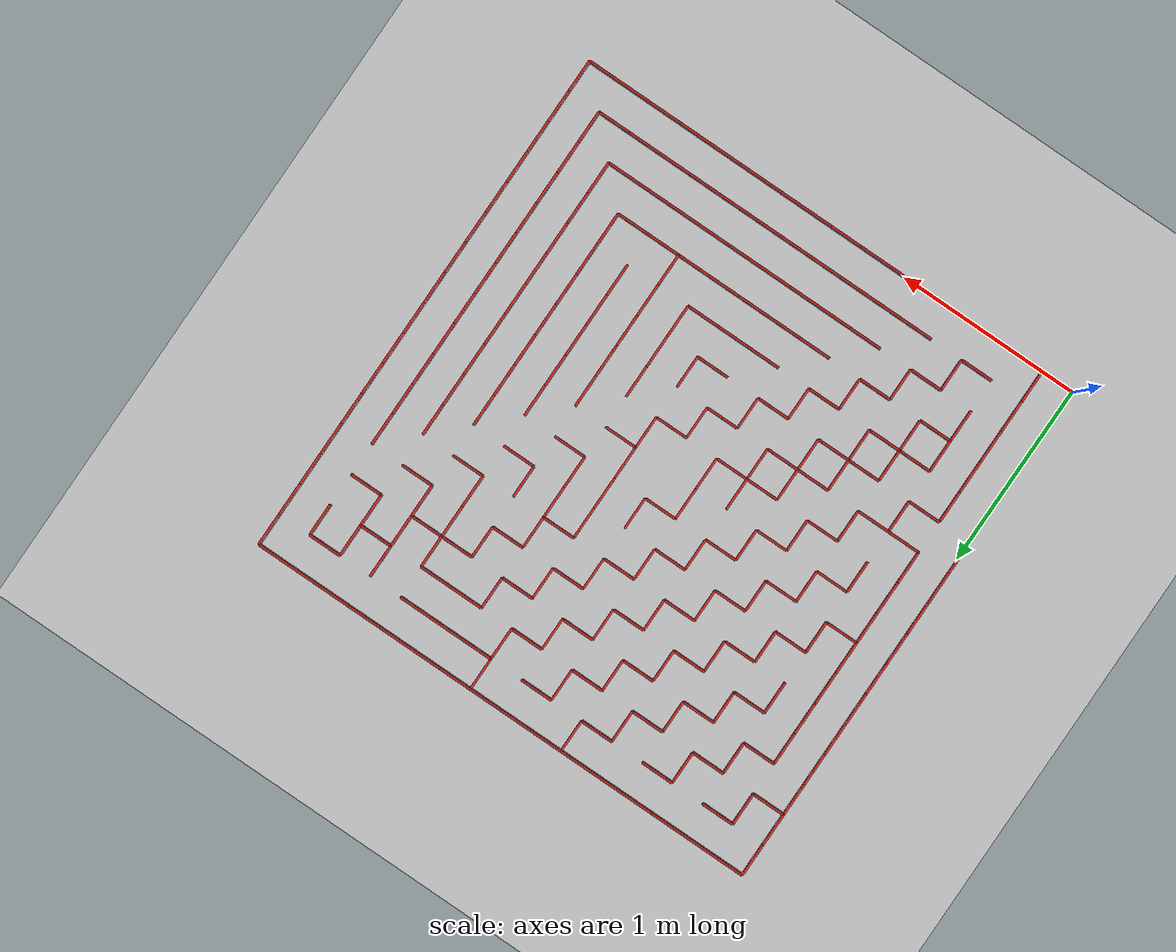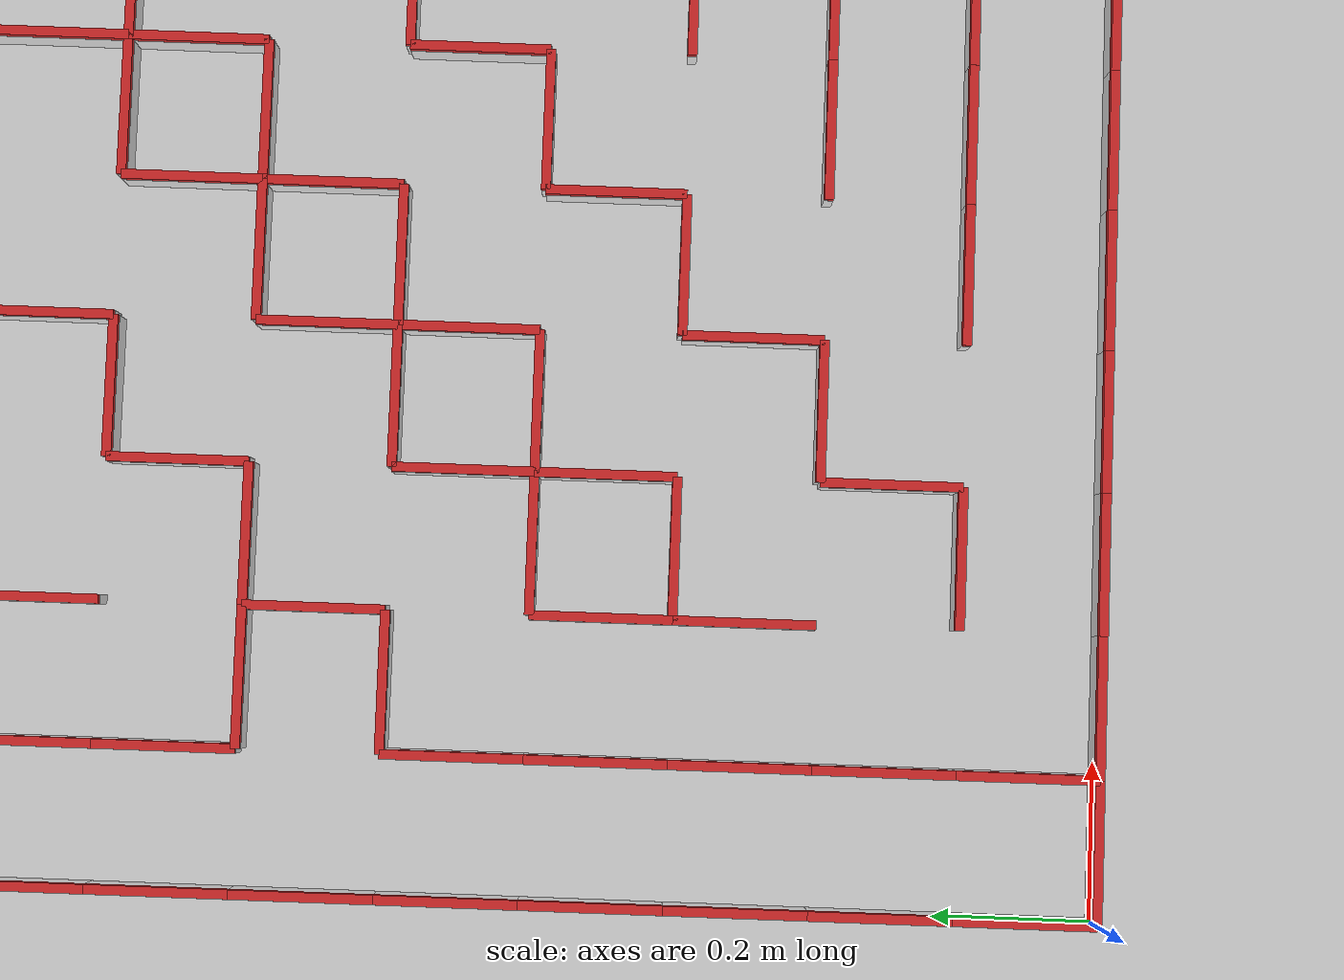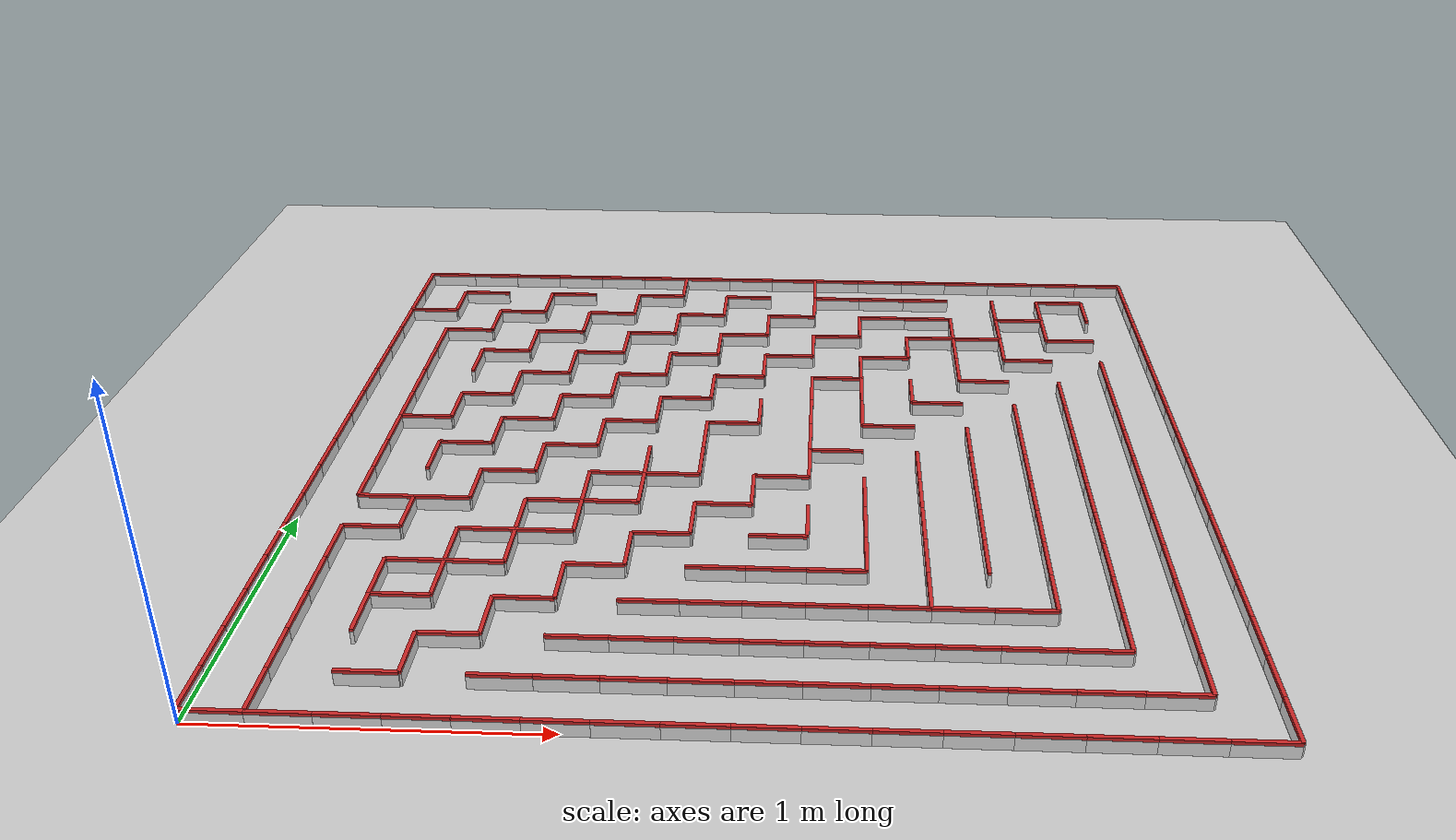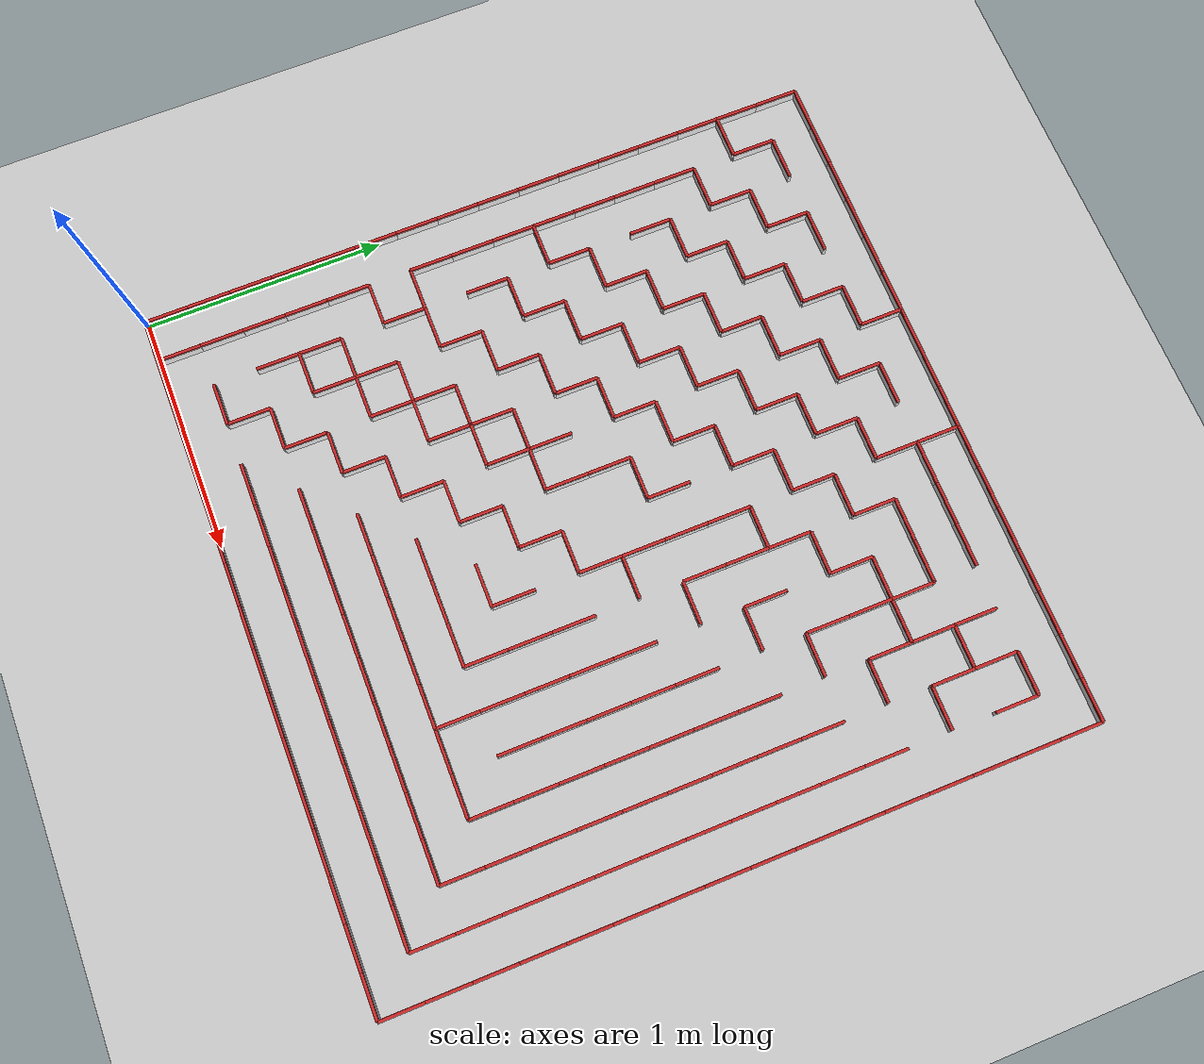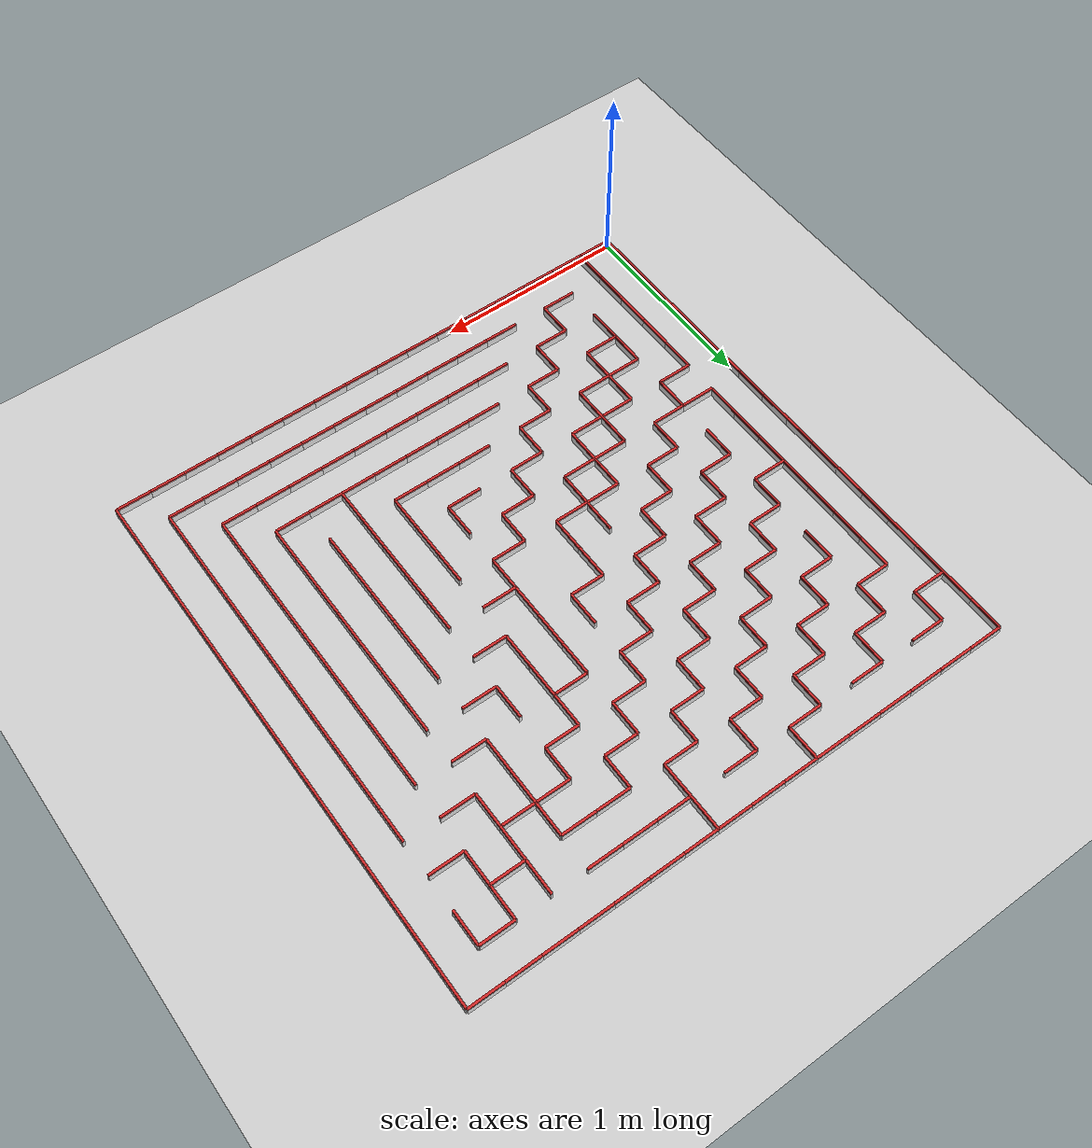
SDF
<sdf version="1.6">
  <world name="default">

    <gui>
	<camera name="user_camera">
        <track_visual>
          <name>vayu</name>
          <static>true</static>
          <use_model_frame>true</use_model_frame>
          <xyz>0 -0.25 0.75</xyz>
          <inherit_yaw>false</inherit_yaw>
        </track_visual>
	</camera>
    </gui>

    <scene>
      <ambient>0.4 0.4 0.4 1</ambient>
      <background>1 1 1 1</background>
      <shadows>false</shadows>
	<grid>1</grid>
    </scene>

    <!-- A global light source -->
    <include>
      <uri>model://sun</uri>
    </include>

    <!-- A ground plane -->
    <include>
      <uri>model://ground_plane</uri>
    </include>

    <!-- My maze -->
    <include>
      <uri>model://maze</uri>
	<pose> 0 0 0 0 0 0</pose>
    </include>

    <physics type="ode">
      <real_time_update_rate>400.0</real_time_update_rate>
      <max_step_size>0.0025</max_step_size>
      <real_time_factor>1</real_time_factor>
      <ode>
        <solver>
          <type>quick</type>
          <iters>250</iters>
          <precon_iters>0</precon_iters>
          <sor>1.400000</sor>
          <use_dynamic_moi_rescaling>1</use_dynamic_moi_rescaling>
        </solver>
        <constraints>
          <cfm>0.00001</cfm>
          <erp>0.2</erp>
          <contact_max_correcting_vel>2000.000000</contact_max_correcting_vel>
          <contact_surface_layer>0.01000</contact_surface_layer>
        </constraints>
      </ode>
    </physics>
  </world>

</sdf>

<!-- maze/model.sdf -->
<sdf version="1.6">
  <model name="maze">
    <pose frame="">0 0 0 0 0 0</pose>

    <static>1</static>
  <link name="Wall_0">
      <pose frame="">0.0 2.88 0 0 0 0</pose>
      <collision name="Wall_Base_Collision_0">
        <geometry>
          <box>
            <size>0.18 0.012 0.04</size>
          </box>
        </geometry>
        <pose frame="">0.09 0 0.02 0 0 0</pose>
      </collision>
      <visual name="Wall_Base_Visual_0">
        <pose frame="">0.09 0 0.02 0 0 0</pose>
        <geometry>
          <box>
            <size>0.18 0.012 0.04</size>
          </box>
        </geometry>
        <material>
          <script>
            <uri>file://media/materials/scripts/gazebo.material</uri>
            <name>Gazebo/White</name>
          </script>
        </material>
      </visual>
      <collision name="Wall_Top_Collision_0">
        <geometry>
          <box>
            <size>0.18 0.012 0.01</size>
          </box>
        </geometry>
        <pose frame="">0.09 0 0.045 0 0 0</pose>
      </collision>
      <visual name="Wall_Top_Visual_0">
        <pose frame="">0.09 0 0.045 0 0 0</pose>
        <geometry>
          <box>
            <size>0.18 0.012 0.01</size>
          </box>
        </geometry>
        <material>
          <script>
            <uri>file://media/materials/scripts/gazebo.material</uri>
            <name>Gazebo/Red</name>
          </script>
        </material>
      </visual>
    </link>

    <link name="Wall_1">
      <pose frame="">0.18 2.88 0 0 0 0</pose>
      <collision name="Wall_Base_Collision_1">
        <geometry>
          <box>
            <size>0.18 0.012 0.04</size>
          </box>
        </geometry>
        <pose frame="">0.09 0 0.02 0 0 0</pose>
      </collision>
      <visual name="Wall_Base_Visual_1">
        <pose frame="">0.09 0 0.02 0 0 0</pose>
        <geometry>
          <box>
            <size>0.18 0.012 0.04</size>
          </box>
        </geometry>
        <material>
          <script>
            <uri>file://media/materials/scripts/gazebo.material</uri>
            <name>Gazebo/White</name>
          </script>
        </material>
      </visual>
      <collision name="Wall_Top_Collision_1">
        <geometry>
          <box>
            <size>0.18 0.012 0.01</size>
          </box>
        </geometry>
        <pose frame="">0.09 0 0.045 0 0 0</pose>
      </collision>
      <visual name="Wall_Top_Visual_1">
        <pose frame="">0.09 0 0.045 0 0 0</pose>
        <geometry>
          <box>
            <size>0.18 0.012 0.01</size>
          </box>
        </geometry>
        <material>
          <script>
            <uri>file://media/materials/scripts/gazebo.material</uri>
            <name>Gazebo/Red</name>
          </script>
        </material>
      </visual>
    </link>

    <link name="Wall_2">
      <pose frame="">0.36 2.88 0 0 0 0</pose>
      <collision name="Wall_Base_Collision_2">
        <geometry>
          <box>
            <size>0.18 0.012 0.04</size>
          </box>
        </geometry>
        <pose frame="">0.09 0 0.02 0 0 0</pose>
      </collision>
      <visual name="Wall_Base_Visual_2">
        <pose frame="">0.09 0 0.02 0 0 0</pose>
        <geometry>
          <box>
            <size>0.18 0.012 0.04</size>
          </box>
        </geometry>
        <material>
          <script>
            <uri>file://media/materials/scripts/gazebo.material</uri>
            <name>Gazebo/White</name>
          </script>
        </material>
      </visual>
      <collision name="Wall_Top_Collision_2">
        <geometry>
          <box>
            <size>0.18 0.012 0.01</size>
          </box>
        </geometry>
        <pose frame="">0.09 0 0.045 0 0 0</pose>
      </collision>
      <visual name="Wall_Top_Visual_2">
        <pose frame="">0.09 0 0.045 0 0 0</pose>
        <geometry>
          <box>
            <size>0.18 0.012 0.01</size>
          </box>
        </geometry>
        <material>
          <script>
            <uri>file://media/materials/scripts/gazebo.material</uri>
            <name>Gazebo/Red</name>
          </script>
        </material>
      </visual>
    </link>

    <link name="Wall_3">
      <pose frame="">0.54 2.88 0 0 0 0</pose>
      <collision name="Wall_Base_Collision_3">
        <geometry>
          <box>
            <size>0.18 0.012 0.04</size>
          </box>
        </geometry>
        <pose frame="">0.09 0 0.02 0 0 0</pose>
      </collision>
      <visual name="Wall_Base_Visual_3">
        <pose frame="">0.09 0 0.02 0 0 0</pose>
        <geometry>
          <box>
            <size>0.18 0.012 0.04</size>
          </box>
        </geometry>
        <material>
          <script>
            <uri>file://media/materials/scripts/gazebo.material</uri>
            <name>Gazebo/White</name>
          </script>
        </material>
      </visual>
      <collision name="Wall_Top_Collision_3">
        <geometry>
          <box>
            <size>0.18 0.012 0.01</size>
          </box>
        </geometry>
        <pose frame="">0.09 0 0.045 0 0 0</pose>
      </collision>
      <visual name="Wall_Top_Visual_3">
        <pose frame="">0.09 0 0.045 0 0 0</pose>
        <geometry>
          <box>
            <size>0.18 0.012 0.01</size>
          </box>
        </geometry>
        <material>
          <script>
            <uri>file://media/materials/scripts/gazebo.material</uri>
            <name>Gazebo/Red</name>
          </script>
        </material>
      </visual>
    </link>

    <link name="Wall_4">
      <pose frame="">0.72 2.88 0 0 0 0</pose>
      <collision name="Wall_Base_Collision_4">
        <geometry>
          <box>
            <size>0.18 0.012 0.04</size>
          </box>
        </geometry>
        <pose frame="">0.09 0 0.02 0 0 0</pose>
      </collision>
      <visual name="Wall_Base_Visual_4">
        <pose frame="">0.09 0 0.02 0 0 0</pose>
        <geometry>
          <box>
            <size>0.18 0.012 0.04</size>
          </box>
        </geometry>
        <material>
          <script>
            <uri>file://media/materials/scripts/gazebo.material</uri>
            <name>Gazebo/White</name>
          </script>
        </material>
      </visual>
      <collision name="Wall_Top_Collision_4">
        <geometry>
          <box>
            <size>0.18 0.012 0.01</size>
          </box>
        </geometry>
        <pose frame="">0.09 0 0.045 0 0 0</pose>
      </collision>
      <visual name="Wall_Top_Visual_4">
        <pose frame="">0.09 0 0.045 0 0 0</pose>
        <geometry>
          <box>
            <size>0.18 0.012 0.01</size>
          </box>
        </geometry>
        <material>
          <script>
            <uri>file://media/materials/scripts/gazebo.material</uri>
            <name>Gazebo/Red</name>
          </script>
        </material>
      </visual>
    </link>

    <link name="Wall_5">
      <pose frame="">0.8999999999999999 2.88 0 0 0 0</pose>
      <collision name="Wall_Base_Collision_5">
        <geometry>
          <box>
            <size>0.18 0.012 0.04</size>
          </box>
        </geometry>
        <pose frame="">0.09 0 0.02 0 0 0</pose>
      </collision>
      <visual name="Wall_Base_Visual_5">
        <pose frame="">0.09 0 0.02 0 0 0</pose>
        <geometry>
          <box>
            <size>0.18 0.012 0.04</size>
          </box>
        </geometry>
        <material>
          <script>
            <uri>file://media/materials/scripts/gazebo.material</uri>
            <name>Gazebo/White</name>
          </script>
        </material>
      </visual>
      <collision name="Wall_Top_Collision_5">
        <geometry>
          <box>
            <size>0.18 0.012 0.01</size>
          </box>
        </geometry>
        <pose frame="">0.09 0 0.045 0 0 0</pose>
      </collision>
      <visual name="Wall_Top_Visual_5">
        <pose frame="">0.09 0 0.045 0 0 0</pose>
        <geometry>
          <box>
            <size>0.18 0.012 0.01</size>
          </box>
        </geometry>
        <material>
          <script>
            <uri>file://media/materials/scripts/gazebo.material</uri>
            <name>Gazebo/Red</name>
          </script>
        </material>
      </visual>
    </link>

    <link name="Wall_6">
      <pose frame="">1.08 2.88 0 0 0 0</pose>
      <collision name="Wall_Base_Collision_6">
        <geometry>
          <box>
            <size>0.18 0.012 0.04</size>
          </box>
        </geometry>
        <pose frame="">0.09 0 0.02 0 0 0</pose>
      </collision>
      <visual name="Wall_Base_Visual_6">
        <pose frame="">0.09 0 0.02 0 0 0</pose>
        <geometry>
          <box>
            <size>0.18 0.012 0.04</size>
          </box>
        </geometry>
        <material>
          <script>
            <uri>file://media/materials/scripts/gazebo.material</uri>
            <name>Gazebo/White</name>
          </script>
        </material>
      </visual>
      <collision name="Wall_Top_Collision_6">
        <geometry>
          <box>
            <size>0.18 0.012 0.01</size>
          </box>
        </geometry>
        <pose frame="">0.09 0 0.045 0 0 0</pose>
      </collision>
      <visual name="Wall_Top_Visual_6">
        <pose frame="">0.09 0 0.045 0 0 0</pose>
        <geometry>
          <box>
            <size>0.18 0.012 0.01</size>
          </box>
        </geometry>
        <material>
          <script>
            <uri>file://media/materials/scripts/gazebo.material</uri>
            <name>Gazebo/Red</name>
          </script>
        </material>
      </visual>
    </link>

    <link name="Wall_7">
      <pose frame="">1.26 2.88 0 0 0 0</pose>
      <collision name="Wall_Base_Collision_7">
        <geometry>
          <box>
            <size>0.18 0.012 0.04</size>
          </box>
        </geometry>
        <pose frame="">0.09 0 0.02 0 0 0</pose>
      </collision>
      <visual name="Wall_Base_Visual_7">
        <pose frame="">0.09 0 0.02 0 0 0</pose>
        <geometry>
          <box>
            <size>0.18 0.012 0.04</size>
          </box>
        </geometry>
        <material>
          <script>
            <uri>file://media/materials/scripts/gazebo.material</uri>
            <name>Gazebo/White</name>
          </script>
        </material>
      </visual>
      <collision name="Wall_Top_Collision_7">
        <geometry>
          <box>
            <size>0.18 0.012 0.01</size>
          </box>
        </geometry>
        <pose frame="">0.09 0 0.045 0 0 0</pose>
      </collision>
      <visual name="Wall_Top_Visual_7">
        <pose frame="">0.09 0 0.045 0 0 0</pose>
        <geometry>
          <box>
            <size>0.18 0.012 0.01</size>
          </box>
        </geometry>
        <material>
          <script>
            <uri>file://media/materials/scripts/gazebo.material</uri>
            <name>Gazebo/Red</name>
          </script>
        </material>
      </visual>
    </link>

    <link name="Wall_8">
      <pose frame="">1.44 2.88 0 0 0 0</pose>
      <collision name="Wall_Base_Collision_8">
        <geometry>
          <box>
            <size>0.18 0.012 0.04</size>
          </box>
        </geometry>
        <pose frame="">0.09 0 0.02 0 0 0</pose>
      </collision>
      <visual name="Wall_Base_Visual_8">
        <pose frame="">0.09 0 0.02 0 0 0</pose>
        <geometry>
          <box>
            <size>0.18 0.012 0.04</size>
          </box>
        </geometry>
        <material>
          <script>
            <uri>file://media/materials/scripts/gazebo.material</uri>
            <name>Gazebo/White</name>
          </script>
        </material>
      </visual>
      <collision name="Wall_Top_Collision_8">
        <geometry>
          <box>
            <size>0.18 0.012 0.01</size>
          </box>
        </geometry>
        <pose frame="">0.09 0 0.045 0 0 0</pose>
      </collision>
      <visual name="Wall_Top_Visual_8">
        <pose frame="">0.09 0 0.045 0 0 0</pose>
        <geometry>
          <box>
            <size>0.18 0.012 0.01</size>
          </box>
        </geometry>
        <material>
          <script>
            <uri>file://media/materials/scripts/gazebo.material</uri>
            <name>Gazebo/Red</name>
          </script>
        </material>
      </visual>
    </link>

    <link name="Wall_9">
      <pose frame="">1.6199999999999999 2.88 0 0 0 0</pose>
      <collision name="Wall_Base_Collision_9">
        <geometry>
          <box>
            <size>0.18 0.012 0.04</size>
          </box>
        </geometry>
        <pose frame="">0.09 0 0.02 0 0 0</pose>
      </collision>
      <visual name="Wall_Base_Visual_9">
        <pose frame="">0.09 0 0.02 0 0 0</pose>
        <geometry>
          <box>
            <size>0.18 0.012 0.04</size>
          </box>
        </geometry>
        <material>
          <script>
            <uri>file://media/materials/scripts/gazebo.material</uri>
            <name>Gazebo/White</name>
          </script>
        </material>
      </visual>
      <collision name="Wall_Top_Collision_9">
        <geometry>
          <box>
            <size>0.18 0.012 0.01</size>
          </box>
        </geometry>
        <pose frame="">0.09 0 0.045 0 0 0</pose>
      </collision>
      <visual name="Wall_Top_Visual_9">
        <pose frame="">0.09 0 0.045 0 0 0</pose>
        <geometry>
          <box>
            <size>0.18 0.012 0.01</size>
          </box>
        </geometry>
        <material>
          <script>
            <uri>file://media/materials/scripts/gazebo.material</uri>
            <name>Gazebo/Red</name>
          </script>
        </material>
      </visual>
    </link>

    <link name="Wall_10">
      <pose frame="">1.7999999999999998 2.88 0 0 0 0</pose>
      <collision name="Wall_Base_Collision_10">
        <geometry>
          <box>
            <size>0.18 0.012 0.04</size>
          </box>
        </geometry>
        <pose frame="">0.09 0 0.02 0 0 0</pose>
      </collision>
      <visual name="Wall_Base_Visual_10">
        <pose frame="">0.09 0 0.02 0 0 0</pose>
        <geometry>
          <box>
            <size>0.18 0.012 0.04</size>
          </box>
        </geometry>
        <material>
          <script>
            <uri>file://media/materials/scripts/gazebo.material</uri>
            <name>Gazebo/White</name>
          </script>
        </material>
      </visual>
      <collision name="Wall_Top_Collision_10">
        <geometry>
          <box>
            <size>0.18 0.012 0.01</size>
          </box>
        </geometry>
        <pose frame="">0.09 0 0.045 0 0 0</pose>
      </collision>
      <visual name="Wall_Top_Visual_10">
        <pose frame="">0.09 0 0.045 0 0 0</pose>
        <geometry>
          <box>
            <size>0.18 0.012 0.01</size>
          </box>
        </geometry>
        <material>
          <script>
            <uri>file://media/materials/scripts/gazebo.material</uri>
            <name>Gazebo/Red</name>
          </script>
        </material>
      </visual>
    </link>

    <link name="Wall_11">
      <pose frame="">1.98 2.88 0 0 0 0</pose>
      <collision name="Wall_Base_Collision_11">
        <geometry>
          <box>
            <size>0.18 0.012 0.04</size>
          </box>
        </geometry>
        <pose frame="">0.09 0 0.02 0 0 0</pose>
      </collision>
      <visual name="Wall_Base_Visual_11">
        <pose frame="">0.09 0 0.02 0 0 0</pose>
        <geometry>
          <box>
            <size>0.18 0.012 0.04</size>
          </box>
        </geometry>
        <material>
          <script>
            <uri>file://media/materials/scripts/gazebo.material</uri>
            <name>Gazebo/White</name>
          </script>
        </material>
      </visual>
      <collision name="Wall_Top_Collision_11">
        <geometry>
          <box>
            <size>0.18 0.012 0.01</size>
          </box>
        </geometry>
        <pose frame="">0.09 0 0.045 0 0 0</pose>
      </collision>
      <visual name="Wall_Top_Visual_11">
        <pose frame="">0.09 0 0.045 0 0 0</pose>
        <geometry>
          <box>
            <size>0.18 0.012 0.01</size>
          </box>
        </geometry>
        <material>
          <script>
            <uri>file://media/materials/scripts/gazebo.material</uri>
            <name>Gazebo/Red</name>
          </script>
        </material>
      </visual>
    </link>

    <link name="Wall_12">
      <pose frame="">2.16 2.88 0 0 0 0</pose>
      <collision name="Wall_Base_Collision_12">
        <geometry>
          <box>
            <size>0.18 0.012 0.04</size>
          </box>
        </geometry>
        <pose frame="">0.09 0 0.02 0 0 0</pose>
      </collision>
      <visual name="Wall_Base_Visual_12">
        <pose frame="">0.09 0 0.02 0 0 0</pose>
        <geometry>
          <box>
            <size>0.18 0.012 0.04</size>
          </box>
        </geometry>
        <material>
          <script>
            <uri>file://media/materials/scripts/gazebo.material</uri>
            <name>Gazebo/White</name>
          </script>
        </material>
      </visual>
      <collision name="Wall_Top_Collision_12">
        <geometry>
          <box>
            <size>0.18 0.012 0.01</size>
          </box>
        </geometry>
        <pose frame="">0.09 0 0.045 0 0 0</pose>
      </collision>
      <visual name="Wall_Top_Visual_12">
        <pose frame="">0.09 0 0.045 0 0 0</pose>
        <geometry>
          <box>
            <size>0.18 0.012 0.01</size>
          </box>
        </geometry>
        <material>
          <script>
            <uri>file://media/materials/scripts/gazebo.material</uri>
            <name>Gazebo/Red</name>
          </script>
        </material>
      </visual>
    </link>

    <link name="Wall_13">
      <pose frame="">2.34 2.88 0 0 0 0</pose>
      <collision name="Wall_Base_Collision_13">
        <geometry>
          <box>
            <size>0.18 0.012 0.04</size>
          </box>
        </geometry>
        <pose frame="">0.09 0 0.02 0 0 0</pose>
      </collision>
      <visual name="Wall_Base_Visual_13">
        <pose frame="">0.09 0 0.02 0 0 0</pose>
        <geometry>
          <box>
            <size>0.18 0.012 0.04</size>
          </box>
        </geometry>
        <material>
          <script>
            <uri>file://media/materials/scripts/gazebo.material</uri>
            <name>Gazebo/White</name>
          </script>
        </material>
      </visual>
      <collision name="Wall_Top_Collision_13">
        <geometry>
          <box>
            <size>0.18 0.012 0.01</size>
          </box>
        </geometry>
        <pose frame="">0.09 0 0.045 0 0 0</pose>
      </collision>
      <visual name="Wall_Top_Visual_13">
        <pose frame="">0.09 0 0.045 0 0 0</pose>
        <geometry>
          <box>
            <size>0.18 0.012 0.01</size>
          </box>
        </geometry>
        <material>
          <script>
            <uri>file://media/materials/scripts/gazebo.material</uri>
            <name>Gazebo/Red</name>
          </script>
        </material>
      </visual>
    </link>

    <link name="Wall_14">
      <pose frame="">2.52 2.88 0 0 0 0</pose>
      <collision name="Wall_Base_Collision_14">
        <geometry>
          <box>
            <size>0.18 0.012 0.04</size>
          </box>
        </geometry>
        <pose frame="">0.09 0 0.02 0 0 0</pose>
      </collision>
      <visual name="Wall_Base_Visual_14">
        <pose frame="">0.09 0 0.02 0 0 0</pose>
        <geometry>
          <box>
            <size>0.18 0.012 0.04</size>
          </box>
        </geometry>
        <material>
          <script>
            <uri>file://media/materials/scripts/gazebo.material</uri>
            <name>Gazebo/White</name>
          </script>
        </material>
      </visual>
      <collision name="Wall_Top_Collision_14">
        <geometry>
          <box>
            <size>0.18 0.012 0.01</size>
          </box>
        </geometry>
        <pose frame="">0.09 0 0.045 0 0 0</pose>
      </collision>
      <visual name="Wall_Top_Visual_14">
        <pose frame="">0.09 0 0.045 0 0 0</pose>
        <geometry>
          <box>
            <size>0.18 0.012 0.01</size>
          </box>
        </geometry>
        <material>
          <script>
            <uri>file://media/materials/scripts/gazebo.material</uri>
            <name>Gazebo/Red</name>
          </script>
        </material>
      </visual>
    </link>

    <link name="Wall_15">
      <pose frame="">2.6999999999999997 2.88 0 0 0 0</pose>
      <collision name="Wall_Base_Collision_15">
        <geometry>
          <box>
            <size>0.18 0.012 0.04</size>
          </box>
        </geometry>
        <pose frame="">0.09 0 0.02 0 0 0</pose>
      </collision>
      <visual name="Wall_Base_Visual_15">
        <pose frame="">0.09 0 0.02 0 0 0</pose>
        <geometry>
          <box>
            <size>0.18 0.012 0.04</size>
          </box>
        </geometry>
        <material>
          <script>
            <uri>file://media/materials/scripts/gazebo.material</uri>
            <name>Gazebo/White</name>
          </script>
        </material>
      </visual>
      <collision name="Wall_Top_Collision_15">
        <geometry>
          <box>
            <size>0.18 0.012 0.01</size>
          </box>
        </geometry>
        <pose frame="">0.09 0 0.045 0 0 0</pose>
      </collision>
      <visual name="Wall_Top_Visual_15">
        <pose frame="">0.09 0 0.045 0 0 0</pose>
        <geometry>
          <box>
            <size>0.18 0.012 0.01</size>
          </box>
        </geometry>
        <material>
          <script>
            <uri>file://media/materials/scripts/gazebo.material</uri>
            <name>Gazebo/Red</name>
          </script>
        </material>
      </visual>
    </link>

    <link name="Wall_16">
      <pose frame="">0.0 2.6999999999999997 0 0 0 1.5707963267948966</pose>
      <collision name="Wall_Base_Collision_16">
        <geometry>
          <box>
            <size>0.18 0.012 0.04</size>
          </box>
        </geometry>
        <pose frame="">0.09 0 0.02 0 0 0</pose>
      </collision>
      <visual name="Wall_Base_Visual_16">
        <pose frame="">0.09 0 0.02 0 0 0</pose>
        <geometry>
          <box>
            <size>0.18 0.012 0.04</size>
          </box>
        </geometry>
        <material>
          <script>
            <uri>file://media/materials/scripts/gazebo.material</uri>
            <name>Gazebo/White</name>
          </script>
        </material>
      </visual>
      <collision name="Wall_Top_Collision_16">
        <geometry>
          <box>
            <size>0.18 0.012 0.01</size>
          </box>
        </geometry>
        <pose frame="">0.09 0 0.045 0 0 0</pose>
      </collision>
      <visual name="Wall_Top_Visual_16">
        <pose frame="">0.09 0 0.045 0 0 0</pose>
        <geometry>
          <box>
            <size>0.18 0.012 0.01</size>
          </box>
        </geometry>
        <material>
          <script>
            <uri>file://media/materials/scripts/gazebo.material</uri>
            <name>Gazebo/Red</name>
          </script>
        </material>
      </visual>
    </link>

    <link name="Wall_17">
      <pose frame="">1.08 2.6999999999999997 0 0 0 1.5707963267948966</pose>
      <collision name="Wall_Base_Collision_17">
        <geometry>
          <box>
            <size>0.18 0.012 0.04</size>
          </box>
        </geometry>
        <pose frame="">0.09 0 0.02 0 0 0</pose>
      </collision>
      <visual name="Wall_Base_Visual_17">
        <pose frame="">0.09 0 0.02 0 0 0</pose>
        <geometry>
          <box>
            <size>0.18 0.012 0.04</size>
          </box>
        </geometry>
        <material>
          <script>
            <uri>file://media/materials/scripts/gazebo.material</uri>
            <name>Gazebo/White</name>
          </script>
        </material>
      </visual>
      <collision name="Wall_Top_Collision_17">
        <geometry>
          <box>
            <size>0.18 0.012 0.01</size>
          </box>
        </geometry>
        <pose frame="">0.09 0 0.045 0 0 0</pose>
      </collision>
      <visual name="Wall_Top_Visual_17">
        <pose frame="">0.09 0 0.045 0 0 0</pose>
        <geometry>
          <box>
            <size>0.18 0.012 0.01</size>
          </box>
        </geometry>
        <material>
          <script>
            <uri>file://media/materials/scripts/gazebo.material</uri>
            <name>Gazebo/Red</name>
          </script>
        </material>
      </visual>
    </link>

    <link name="Wall_18">
      <pose frame="">1.6199999999999999 2.6999999999999997 0 0 0 1.5707963267948966</pose>
      <collision name="Wall_Base_Collision_18">
        <geometry>
          <box>
            <size>0.18 0.012 0.04</size>
          </box>
        </geometry>
        <pose frame="">0.09 0 0.02 0 0 0</pose>
      </collision>
      <visual name="Wall_Base_Visual_18">
        <pose frame="">0.09 0 0.02 0 0 0</pose>
        <geometry>
          <box>
            <size>0.18 0.012 0.04</size>
          </box>
        </geometry>
        <material>
          <script>
            <uri>file://media/materials/scripts/gazebo.material</uri>
            <name>Gazebo/White</name>
          </script>
        </material>
      </visual>
      <collision name="Wall_Top_Collision_18">
        <geometry>
          <box>
            <size>0.18 0.012 0.01</size>
          </box>
        </geometry>
        <pose frame="">0.09 0 0.045 0 0 0</pose>
      </collision>
      <visual name="Wall_Top_Visual_18">
        <pose frame="">0.09 0 0.045 0 0 0</pose>
        <geometry>
          <box>
            <size>0.18 0.012 0.01</size>
          </box>
        </geometry>
        <material>
          <script>
            <uri>file://media/materials/scripts/gazebo.material</uri>
            <name>Gazebo/Red</name>
          </script>
        </material>
      </visual>
    </link>

    <link name="Wall_19">
      <pose frame="">2.88 2.6999999999999997 0 0 0 1.5707963267948966</pose>
      <collision name="Wall_Base_Collision_19">
        <geometry>
          <box>
            <size>0.18 0.012 0.04</size>
          </box>
        </geometry>
        <pose frame="">0.09 0 0.02 0 0 0</pose>
      </collision>
      <visual name="Wall_Base_Visual_19">
        <pose frame="">0.09 0 0.02 0 0 0</pose>
        <geometry>
          <box>
            <size>0.18 0.012 0.04</size>
          </box>
        </geometry>
        <material>
          <script>
            <uri>file://media/materials/scripts/gazebo.material</uri>
            <name>Gazebo/White</name>
          </script>
        </material>
      </visual>
      <collision name="Wall_Top_Collision_19">
        <geometry>
          <box>
            <size>0.18 0.012 0.01</size>
          </box>
        </geometry>
        <pose frame="">0.09 0 0.045 0 0 0</pose>
      </collision>
      <visual name="Wall_Top_Visual_19">
        <pose frame="">0.09 0 0.045 0 0 0</pose>
        <geometry>
          <box>
            <size>0.18 0.012 0.01</size>
          </box>
        </geometry>
        <material>
          <script>
            <uri>file://media/materials/scripts/gazebo.material</uri>
            <name>Gazebo/Red</name>
          </script>
        </material>
      </visual>
    </link>

    <link name="Wall_20">
      <pose frame="">0.18 2.6999999999999997 0 0 0 0</pose>
      <collision name="Wall_Base_Collision_20">
        <geometry>
          <box>
            <size>0.18 0.012 0.04</size>
          </box>
        </geometry>
        <pose frame="">0.09 0 0.02 0 0 0</pose>
      </collision>
      <visual name="Wall_Base_Visual_20">
        <pose frame="">0.09 0 0.02 0 0 0</pose>
        <geometry>
          <box>
            <size>0.18 0.012 0.04</size>
          </box>
        </geometry>
        <material>
          <script>
            <uri>file://media/materials/scripts/gazebo.material</uri>
            <name>Gazebo/White</name>
          </script>
        </material>
      </visual>
      <collision name="Wall_Top_Collision_20">
        <geometry>
          <box>
            <size>0.18 0.012 0.01</size>
          </box>
        </geometry>
        <pose frame="">0.09 0 0.045 0 0 0</pose>
      </collision>
      <visual name="Wall_Top_Visual_20">
        <pose frame="">0.09 0 0.045 0 0 0</pose>
        <geometry>
          <box>
            <size>0.18 0.012 0.01</size>
          </box>
        </geometry>
        <material>
          <script>
            <uri>file://media/materials/scripts/gazebo.material</uri>
            <name>Gazebo/Red</name>
          </script>
        </material>
      </visual>
    </link>

    <link name="Wall_21">
      <pose frame="">0.54 2.6999999999999997 0 0 0 0</pose>
      <collision name="Wall_Base_Collision_21">
        <geometry>
          <box>
            <size>0.18 0.012 0.04</size>
          </box>
        </geometry>
        <pose frame="">0.09 0 0.02 0 0 0</pose>
      </collision>
      <visual name="Wall_Base_Visual_21">
        <pose frame="">0.09 0 0.02 0 0 0</pose>
        <geometry>
          <box>
            <size>0.18 0.012 0.04</size>
          </box>
        </geometry>
        <material>
          <script>
            <uri>file://media/materials/scripts/gazebo.material</uri>
            <name>Gazebo/White</name>
          </script>
        </material>
      </visual>
      <collision name="Wall_Top_Collision_21">
        <geometry>
          <box>
            <size>0.18 0.012 0.01</size>
          </box>
        </geometry>
        <pose frame="">0.09 0 0.045 0 0 0</pose>
      </collision>
      <visual name="Wall_Top_Visual_21">
        <pose frame="">0.09 0 0.045 0 0 0</pose>
        <geometry>
          <box>
            <size>0.18 0.012 0.01</size>
          </box>
        </geometry>
        <material>
          <script>
            <uri>file://media/materials/scripts/gazebo.material</uri>
            <name>Gazebo/Red</name>
          </script>
        </material>
      </visual>
    </link>

    <link name="Wall_22">
      <pose frame="">0.8999999999999999 2.6999999999999997 0 0 0 0</pose>
      <collision name="Wall_Base_Collision_22">
        <geometry>
          <box>
            <size>0.18 0.012 0.04</size>
          </box>
        </geometry>
        <pose frame="">0.09 0 0.02 0 0 0</pose>
      </collision>
      <visual name="Wall_Base_Visual_22">
        <pose frame="">0.09 0 0.02 0 0 0</pose>
        <geometry>
          <box>
            <size>0.18 0.012 0.04</size>
          </box>
        </geometry>
        <material>
          <script>
            <uri>file://media/materials/scripts/gazebo.material</uri>
            <name>Gazebo/White</name>
          </script>
        </material>
      </visual>
      <collision name="Wall_Top_Collision_22">
        <geometry>
          <box>
            <size>0.18 0.012 0.01</size>
          </box>
        </geometry>
        <pose frame="">0.09 0 0.045 0 0 0</pose>
      </collision>
      <visual name="Wall_Top_Visual_22">
        <pose frame="">0.09 0 0.045 0 0 0</pose>
        <geometry>
          <box>
            <size>0.18 0.012 0.01</size>
          </box>
        </geometry>
        <material>
          <script>
            <uri>file://media/materials/scripts/gazebo.material</uri>
            <name>Gazebo/Red</name>
          </script>
        </material>
      </visual>
    </link>

    <link name="Wall_23">
      <pose frame="">1.26 2.6999999999999997 0 0 0 0</pose>
      <collision name="Wall_Base_Collision_23">
        <geometry>
          <box>
            <size>0.18 0.012 0.04</size>
          </box>
        </geometry>
        <pose frame="">0.09 0 0.02 0 0 0</pose>
      </collision>
      <visual name="Wall_Base_Visual_23">
        <pose frame="">0.09 0 0.02 0 0 0</pose>
        <geometry>
          <box>
            <size>0.18 0.012 0.04</size>
          </box>
        </geometry>
        <material>
          <script>
            <uri>file://media/materials/scripts/gazebo.material</uri>
            <name>Gazebo/White</name>
          </script>
        </material>
      </visual>
      <collision name="Wall_Top_Collision_23">
        <geometry>
          <box>
            <size>0.18 0.012 0.01</size>
          </box>
        </geometry>
        <pose frame="">0.09 0 0.045 0 0 0</pose>
      </collision>
      <visual name="Wall_Top_Visual_23">
        <pose frame="">0.09 0 0.045 0 0 0</pose>
        <geometry>
          <box>
            <size>0.18 0.012 0.01</size>
          </box>
        </geometry>
        <material>
          <script>
            <uri>file://media/materials/scripts/gazebo.material</uri>
            <name>Gazebo/Red</name>
          </script>
        </material>
      </visual>
    </link>

    <link name="Wall_24">
      <pose frame="">1.6199999999999999 2.6999999999999997 0 0 0 0</pose>
      <collision name="Wall_Base_Collision_24">
        <geometry>
          <box>
            <size>0.18 0.012 0.04</size>
          </box>
        </geometry>
        <pose frame="">0.09 0 0.02 0 0 0</pose>
      </collision>
      <visual name="Wall_Base_Visual_24">
        <pose frame="">0.09 0 0.02 0 0 0</pose>
        <geometry>
          <box>
            <size>0.18 0.012 0.04</size>
          </box>
        </geometry>
        <material>
          <script>
            <uri>file://media/materials/scripts/gazebo.material</uri>
            <name>Gazebo/White</name>
          </script>
        </material>
      </visual>
      <collision name="Wall_Top_Collision_24">
        <geometry>
          <box>
            <size>0.18 0.012 0.01</size>
          </box>
        </geometry>
        <pose frame="">0.09 0 0.045 0 0 0</pose>
      </collision>
      <visual name="Wall_Top_Visual_24">
        <pose frame="">0.09 0 0.045 0 0 0</pose>
        <geometry>
          <box>
            <size>0.18 0.012 0.01</size>
          </box>
        </geometry>
        <material>
          <script>
            <uri>file://media/materials/scripts/gazebo.material</uri>
            <name>Gazebo/Red</name>
          </script>
        </material>
      </visual>
    </link>

    <link name="Wall_25">
      <pose frame="">1.7999999999999998 2.6999999999999997 0 0 0 0</pose>
      <collision name="Wall_Base_Collision_25">
        <geometry>
          <box>
            <size>0.18 0.012 0.04</size>
          </box>
        </geometry>
        <pose frame="">0.09 0 0.02 0 0 0</pose>
      </collision>
      <visual name="Wall_Base_Visual_25">
        <pose frame="">0.09 0 0.02 0 0 0</pose>
        <geometry>
          <box>
            <size>0.18 0.012 0.04</size>
          </box>
        </geometry>
        <material>
          <script>
            <uri>file://media/materials/scripts/gazebo.material</uri>
            <name>Gazebo/White</name>
          </script>
        </material>
      </visual>
      <collision name="Wall_Top_Collision_25">
        <geometry>
          <box>
            <size>0.18 0.012 0.01</size>
          </box>
        </geometry>
        <pose frame="">0.09 0 0.045 0 0 0</pose>
      </collision>
      <visual name="Wall_Top_Visual_25">
        <pose frame="">0.09 0 0.045 0 0 0</pose>
        <geometry>
          <box>
            <size>0.18 0.012 0.01</size>
          </box>
        </geometry>
        <material>
          <script>
            <uri>file://media/materials/scripts/gazebo.material</uri>
            <name>Gazebo/Red</name>
          </script>
        </material>
      </visual>
    </link>

    <link name="Wall_26">
      <pose frame="">1.98 2.6999999999999997 0 0 0 0</pose>
      <collision name="Wall_Base_Collision_26">
        <geometry>
          <box>
            <size>0.18 0.012 0.04</size>
          </box>
        </geometry>
        <pose frame="">0.09 0 0.02 0 0 0</pose>
      </collision>
      <visual name="Wall_Base_Visual_26">
        <pose frame="">0.09 0 0.02 0 0 0</pose>
        <geometry>
          <box>
            <size>0.18 0.012 0.04</size>
          </box>
        </geometry>
        <material>
          <script>
            <uri>file://media/materials/scripts/gazebo.material</uri>
            <name>Gazebo/White</name>
          </script>
        </material>
      </visual>
      <collision name="Wall_Top_Collision_26">
        <geometry>
          <box>
            <size>0.18 0.012 0.01</size>
          </box>
        </geometry>
        <pose frame="">0.09 0 0.045 0 0 0</pose>
      </collision>
      <visual name="Wall_Top_Visual_26">
        <pose frame="">0.09 0 0.045 0 0 0</pose>
        <geometry>
          <box>
            <size>0.18 0.012 0.01</size>
          </box>
        </geometry>
        <material>
          <script>
            <uri>file://media/materials/scripts/gazebo.material</uri>
            <name>Gazebo/Red</name>
          </script>
        </material>
      </visual>
    </link>

    <link name="Wall_27">
      <pose frame="">2.52 2.6999999999999997 0 0 0 0</pose>
      <collision name="Wall_Base_Collision_27">
        <geometry>
          <box>
            <size>0.18 0.012 0.04</size>
          </box>
        </geometry>
        <pose frame="">0.09 0 0.02 0 0 0</pose>
      </collision>
      <visual name="Wall_Base_Visual_27">
        <pose frame="">0.09 0 0.02 0 0 0</pose>
        <geometry>
          <box>
            <size>0.18 0.012 0.04</size>
          </box>
        </geometry>
        <material>
          <script>
            <uri>file://media/materials/scripts/gazebo.material</uri>
            <name>Gazebo/White</name>
          </script>
        </material>
      </visual>
      <collision name="Wall_Top_Collision_27">
        <geometry>
          <box>
            <size>0.18 0.012 0.01</size>
          </box>
        </geometry>
        <pose frame="">0.09 0 0.045 0 0 0</pose>
      </collision>
      <visual name="Wall_Top_Visual_27">
        <pose frame="">0.09 0 0.045 0 0 0</pose>
        <geometry>
          <box>
            <size>0.18 0.012 0.01</size>
          </box>
        </geometry>
        <material>
          <script>
            <uri>file://media/materials/scripts/gazebo.material</uri>
            <name>Gazebo/Red</name>
          </script>
        </material>
      </visual>
    </link>

    <link name="Wall_28">
      <pose frame="">0.0 2.52 0 0 0 1.5707963267948966</pose>
      <collision name="Wall_Base_Collision_28">
        <geometry>
          <box>
            <size>0.18 0.012 0.04</size>
          </box>
        </geometry>
        <pose frame="">0.09 0 0.02 0 0 0</pose>
      </collision>
      <visual name="Wall_Base_Visual_28">
        <pose frame="">0.09 0 0.02 0 0 0</pose>
        <geometry>
          <box>
            <size>0.18 0.012 0.04</size>
          </box>
        </geometry>
        <material>
          <script>
            <uri>file://media/materials/scripts/gazebo.material</uri>
            <name>Gazebo/White</name>
          </script>
        </material>
      </visual>
      <collision name="Wall_Top_Collision_28">
        <geometry>
          <box>
            <size>0.18 0.012 0.01</size>
          </box>
        </geometry>
        <pose frame="">0.09 0 0.045 0 0 0</pose>
      </collision>
      <visual name="Wall_Top_Visual_28">
        <pose frame="">0.09 0 0.045 0 0 0</pose>
        <geometry>
          <box>
            <size>0.18 0.012 0.01</size>
          </box>
        </geometry>
        <material>
          <script>
            <uri>file://media/materials/scripts/gazebo.material</uri>
            <name>Gazebo/Red</name>
          </script>
        </material>
      </visual>
    </link>

    <link name="Wall_29">
      <pose frame="">0.18 2.52 0 0 0 1.5707963267948966</pose>
      <collision name="Wall_Base_Collision_29">
        <geometry>
          <box>
            <size>0.18 0.012 0.04</size>
          </box>
        </geometry>
        <pose frame="">0.09 0 0.02 0 0 0</pose>
      </collision>
      <visual name="Wall_Base_Visual_29">
        <pose frame="">0.09 0 0.02 0 0 0</pose>
        <geometry>
          <box>
            <size>0.18 0.012 0.04</size>
          </box>
        </geometry>
        <material>
          <script>
            <uri>file://media/materials/scripts/gazebo.material</uri>
            <name>Gazebo/White</name>
          </script>
        </material>
      </visual>
      <collision name="Wall_Top_Collision_29">
        <geometry>
          <box>
            <size>0.18 0.012 0.01</size>
          </box>
        </geometry>
        <pose frame="">0.09 0 0.045 0 0 0</pose>
      </collision>
      <visual name="Wall_Top_Visual_29">
        <pose frame="">0.09 0 0.045 0 0 0</pose>
        <geometry>
          <box>
            <size>0.18 0.012 0.01</size>
          </box>
        </geometry>
        <material>
          <script>
            <uri>file://media/materials/scripts/gazebo.material</uri>
            <name>Gazebo/Red</name>
          </script>
        </material>
      </visual>
    </link>

    <link name="Wall_30">
      <pose frame="">0.54 2.52 0 0 0 1.5707963267948966</pose>
      <collision name="Wall_Base_Collision_30">
        <geometry>
          <box>
            <size>0.18 0.012 0.04</size>
          </box>
        </geometry>
        <pose frame="">0.09 0 0.02 0 0 0</pose>
      </collision>
      <visual name="Wall_Base_Visual_30">
        <pose frame="">0.09 0 0.02 0 0 0</pose>
        <geometry>
          <box>
            <size>0.18 0.012 0.04</size>
          </box>
        </geometry>
        <material>
          <script>
            <uri>file://media/materials/scripts/gazebo.material</uri>
            <name>Gazebo/White</name>
          </script>
        </material>
      </visual>
      <collision name="Wall_Top_Collision_30">
        <geometry>
          <box>
            <size>0.18 0.012 0.01</size>
          </box>
        </geometry>
        <pose frame="">0.09 0 0.045 0 0 0</pose>
      </collision>
      <visual name="Wall_Top_Visual_30">
        <pose frame="">0.09 0 0.045 0 0 0</pose>
        <geometry>
          <box>
            <size>0.18 0.012 0.01</size>
          </box>
        </geometry>
        <material>
          <script>
            <uri>file://media/materials/scripts/gazebo.material</uri>
            <name>Gazebo/Red</name>
          </script>
        </material>
      </visual>
    </link>

    <link name="Wall_31">
      <pose frame="">0.8999999999999999 2.52 0 0 0 1.5707963267948966</pose>
      <collision name="Wall_Base_Collision_31">
        <geometry>
          <box>
            <size>0.18 0.012 0.04</size>
          </box>
        </geometry>
        <pose frame="">0.09 0 0.02 0 0 0</pose>
      </collision>
      <visual name="Wall_Base_Visual_31">
        <pose frame="">0.09 0 0.02 0 0 0</pose>
        <geometry>
          <box>
            <size>0.18 0.012 0.04</size>
          </box>
        </geometry>
        <material>
          <script>
            <uri>file://media/materials/scripts/gazebo.material</uri>
            <name>Gazebo/White</name>
          </script>
        </material>
      </visual>
      <collision name="Wall_Top_Collision_31">
        <geometry>
          <box>
            <size>0.18 0.012 0.01</size>
          </box>
        </geometry>
        <pose frame="">0.09 0 0.045 0 0 0</pose>
      </collision>
      <visual name="Wall_Top_Visual_31">
        <pose frame="">0.09 0 0.045 0 0 0</pose>
        <geometry>
          <box>
            <size>0.18 0.012 0.01</size>
          </box>
        </geometry>
        <material>
          <script>
            <uri>file://media/materials/scripts/gazebo.material</uri>
            <name>Gazebo/Red</name>
          </script>
        </material>
      </visual>
    </link>

    <link name="Wall_32">
      <pose frame="">1.26 2.52 0 0 0 1.5707963267948966</pose>
      <collision name="Wall_Base_Collision_32">
        <geometry>
          <box>
            <size>0.18 0.012 0.04</size>
          </box>
        </geometry>
        <pose frame="">0.09 0 0.02 0 0 0</pose>
      </collision>
      <visual name="Wall_Base_Visual_32">
        <pose frame="">0.09 0 0.02 0 0 0</pose>
        <geometry>
          <box>
            <size>0.18 0.012 0.04</size>
          </box>
        </geometry>
        <material>
          <script>
            <uri>file://media/materials/scripts/gazebo.material</uri>
            <name>Gazebo/White</name>
          </script>
        </material>
      </visual>
      <collision name="Wall_Top_Collision_32">
        <geometry>
          <box>
            <size>0.18 0.012 0.01</size>
          </box>
        </geometry>
        <pose frame="">0.09 0 0.045 0 0 0</pose>
      </collision>
      <visual name="Wall_Top_Visual_32">
        <pose frame="">0.09 0 0.045 0 0 0</pose>
        <geometry>
          <box>
            <size>0.18 0.012 0.01</size>
          </box>
        </geometry>
        <material>
          <script>
            <uri>file://media/materials/scripts/gazebo.material</uri>
            <name>Gazebo/Red</name>
          </script>
        </material>
      </visual>
    </link>

    <link name="Wall_33">
      <pose frame="">1.6199999999999999 2.52 0 0 0 1.5707963267948966</pose>
      <collision name="Wall_Base_Collision_33">
        <geometry>
          <box>
            <size>0.18 0.012 0.04</size>
          </box>
        </geometry>
        <pose frame="">0.09 0 0.02 0 0 0</pose>
      </collision>
      <visual name="Wall_Base_Visual_33">
        <pose frame="">0.09 0 0.02 0 0 0</pose>
        <geometry>
          <box>
            <size>0.18 0.012 0.04</size>
          </box>
        </geometry>
        <material>
          <script>
            <uri>file://media/materials/scripts/gazebo.material</uri>
            <name>Gazebo/White</name>
          </script>
        </material>
      </visual>
      <collision name="Wall_Top_Collision_33">
        <geometry>
          <box>
            <size>0.18 0.012 0.01</size>
          </box>
        </geometry>
        <pose frame="">0.09 0 0.045 0 0 0</pose>
      </collision>
      <visual name="Wall_Top_Visual_33">
        <pose frame="">0.09 0 0.045 0 0 0</pose>
        <geometry>
          <box>
            <size>0.18 0.012 0.01</size>
          </box>
        </geometry>
        <material>
          <script>
            <uri>file://media/materials/scripts/gazebo.material</uri>
            <name>Gazebo/Red</name>
          </script>
        </material>
      </visual>
    </link>

    <link name="Wall_34">
      <pose frame="">2.34 2.52 0 0 0 1.5707963267948966</pose>
      <collision name="Wall_Base_Collision_34">
        <geometry>
          <box>
            <size>0.18 0.012 0.04</size>
          </box>
        </geometry>
        <pose frame="">0.09 0 0.02 0 0 0</pose>
      </collision>
      <visual name="Wall_Base_Visual_34">
        <pose frame="">0.09 0 0.02 0 0 0</pose>
        <geometry>
          <box>
            <size>0.18 0.012 0.04</size>
          </box>
        </geometry>
        <material>
          <script>
            <uri>file://media/materials/scripts/gazebo.material</uri>
            <name>Gazebo/White</name>
          </script>
        </material>
      </visual>
      <collision name="Wall_Top_Collision_34">
        <geometry>
          <box>
            <size>0.18 0.012 0.01</size>
          </box>
        </geometry>
        <pose frame="">0.09 0 0.045 0 0 0</pose>
      </collision>
      <visual name="Wall_Top_Visual_34">
        <pose frame="">0.09 0 0.045 0 0 0</pose>
        <geometry>
          <box>
            <size>0.18 0.012 0.01</size>
          </box>
        </geometry>
        <material>
          <script>
            <uri>file://media/materials/scripts/gazebo.material</uri>
            <name>Gazebo/Red</name>
          </script>
        </material>
      </visual>
    </link>

    <link name="Wall_35">
      <pose frame="">2.52 2.52 0 0 0 1.5707963267948966</pose>
      <collision name="Wall_Base_Collision_35">
        <geometry>
          <box>
            <size>0.18 0.012 0.04</size>
          </box>
        </geometry>
        <pose frame="">0.09 0 0.02 0 0 0</pose>
      </collision>
      <visual name="Wall_Base_Visual_35">
        <pose frame="">0.09 0 0.02 0 0 0</pose>
        <geometry>
          <box>
            <size>0.18 0.012 0.04</size>
          </box>
        </geometry>
        <material>
          <script>
            <uri>file://media/materials/scripts/gazebo.material</uri>
            <name>Gazebo/White</name>
          </script>
        </material>
      </visual>
      <collision name="Wall_Top_Collision_35">
        <geometry>
          <box>
            <size>0.18 0.012 0.01</size>
          </box>
        </geometry>
        <pose frame="">0.09 0 0.045 0 0 0</pose>
      </collision>
      <visual name="Wall_Top_Visual_35">
        <pose frame="">0.09 0 0.045 0 0 0</pose>
        <geometry>
          <box>
            <size>0.18 0.012 0.01</size>
          </box>
        </geometry>
        <material>
          <script>
            <uri>file://media/materials/scripts/gazebo.material</uri>
            <name>Gazebo/Red</name>
          </script>
        </material>
      </visual>
    </link>

    <link name="Wall_36">
      <pose frame="">2.6999999999999997 2.52 0 0 0 1.5707963267948966</pose>
      <collision name="Wall_Base_Collision_36">
        <geometry>
          <box>
            <size>0.18 0.012 0.04</size>
          </box>
        </geometry>
        <pose frame="">0.09 0 0.02 0 0 0</pose>
      </collision>
      <visual name="Wall_Base_Visual_36">
        <pose frame="">0.09 0 0.02 0 0 0</pose>
        <geometry>
          <box>
            <size>0.18 0.012 0.04</size>
          </box>
        </geometry>
        <material>
          <script>
            <uri>file://media/materials/scripts/gazebo.material</uri>
            <name>Gazebo/White</name>
          </script>
        </material>
      </visual>
      <collision name="Wall_Top_Collision_36">
        <geometry>
          <box>
            <size>0.18 0.012 0.01</size>
          </box>
        </geometry>
        <pose frame="">0.09 0 0.045 0 0 0</pose>
      </collision>
      <visual name="Wall_Top_Visual_36">
        <pose frame="">0.09 0 0.045 0 0 0</pose>
        <geometry>
          <box>
            <size>0.18 0.012 0.01</size>
          </box>
        </geometry>
        <material>
          <script>
            <uri>file://media/materials/scripts/gazebo.material</uri>
            <name>Gazebo/Red</name>
          </script>
        </material>
      </visual>
    </link>

    <link name="Wall_37">
      <pose frame="">2.88 2.52 0 0 0 1.5707963267948966</pose>
      <collision name="Wall_Base_Collision_37">
        <geometry>
          <box>
            <size>0.18 0.012 0.04</size>
          </box>
        </geometry>
        <pose frame="">0.09 0 0.02 0 0 0</pose>
      </collision>
      <visual name="Wall_Base_Visual_37">
        <pose frame="">0.09 0 0.02 0 0 0</pose>
        <geometry>
          <box>
            <size>0.18 0.012 0.04</size>
          </box>
        </geometry>
        <material>
          <script>
            <uri>file://media/materials/scripts/gazebo.material</uri>
            <name>Gazebo/White</name>
          </script>
        </material>
      </visual>
      <collision name="Wall_Top_Collision_37">
        <geometry>
          <box>
            <size>0.18 0.012 0.01</size>
          </box>
        </geometry>
        <pose frame="">0.09 0 0.045 0 0 0</pose>
      </collision>
      <visual name="Wall_Top_Visual_37">
        <pose frame="">0.09 0 0.045 0 0 0</pose>
        <geometry>
          <box>
            <size>0.18 0.012 0.01</size>
          </box>
        </geometry>
        <material>
          <script>
            <uri>file://media/materials/scripts/gazebo.material</uri>
            <name>Gazebo/Red</name>
          </script>
        </material>
      </visual>
    </link>

    <link name="Wall_38">
      <pose frame="">0.0 2.52 0 0 0 0</pose>
      <collision name="Wall_Base_Collision_38">
        <geometry>
          <box>
            <size>0.18 0.012 0.04</size>
          </box>
        </geometry>
        <pose frame="">0.09 0 0.02 0 0 0</pose>
      </collision>
      <visual name="Wall_Base_Visual_38">
        <pose frame="">0.09 0 0.02 0 0 0</pose>
        <geometry>
          <box>
            <size>0.18 0.012 0.04</size>
          </box>
        </geometry>
        <material>
          <script>
            <uri>file://media/materials/scripts/gazebo.material</uri>
            <name>Gazebo/White</name>
          </script>
        </material>
      </visual>
      <collision name="Wall_Top_Collision_38">
        <geometry>
          <box>
            <size>0.18 0.012 0.01</size>
          </box>
        </geometry>
        <pose frame="">0.09 0 0.045 0 0 0</pose>
      </collision>
      <visual name="Wall_Top_Visual_38">
        <pose frame="">0.09 0 0.045 0 0 0</pose>
        <geometry>
          <box>
            <size>0.18 0.012 0.01</size>
          </box>
        </geometry>
        <material>
          <script>
            <uri>file://media/materials/scripts/gazebo.material</uri>
            <name>Gazebo/Red</name>
          </script>
        </material>
      </visual>
    </link>

    <link name="Wall_39">
      <pose frame="">0.36 2.52 0 0 0 0</pose>
      <collision name="Wall_Base_Collision_39">
        <geometry>
          <box>
            <size>0.18 0.012 0.04</size>
          </box>
        </geometry>
        <pose frame="">0.09 0 0.02 0 0 0</pose>
      </collision>
      <visual name="Wall_Base_Visual_39">
        <pose frame="">0.09 0 0.02 0 0 0</pose>
        <geometry>
          <box>
            <size>0.18 0.012 0.04</size>
          </box>
        </geometry>
        <material>
          <script>
            <uri>file://media/materials/scripts/gazebo.material</uri>
            <name>Gazebo/White</name>
          </script>
        </material>
      </visual>
      <collision name="Wall_Top_Collision_39">
        <geometry>
          <box>
            <size>0.18 0.012 0.01</size>
          </box>
        </geometry>
        <pose frame="">0.09 0 0.045 0 0 0</pose>
      </collision>
      <visual name="Wall_Top_Visual_39">
        <pose frame="">0.09 0 0.045 0 0 0</pose>
        <geometry>
          <box>
            <size>0.18 0.012 0.01</size>
          </box>
        </geometry>
        <material>
          <script>
            <uri>file://media/materials/scripts/gazebo.material</uri>
            <name>Gazebo/Red</name>
          </script>
        </material>
      </visual>
    </link>

    <link name="Wall_40">
      <pose frame="">0.72 2.52 0 0 0 0</pose>
      <collision name="Wall_Base_Collision_40">
        <geometry>
          <box>
            <size>0.18 0.012 0.04</size>
          </box>
        </geometry>
        <pose frame="">0.09 0 0.02 0 0 0</pose>
      </collision>
      <visual name="Wall_Base_Visual_40">
        <pose frame="">0.09 0 0.02 0 0 0</pose>
        <geometry>
          <box>
            <size>0.18 0.012 0.04</size>
          </box>
        </geometry>
        <material>
          <script>
            <uri>file://media/materials/scripts/gazebo.material</uri>
            <name>Gazebo/White</name>
          </script>
        </material>
      </visual>
      <collision name="Wall_Top_Collision_40">
        <geometry>
          <box>
            <size>0.18 0.012 0.01</size>
          </box>
        </geometry>
        <pose frame="">0.09 0 0.045 0 0 0</pose>
      </collision>
      <visual name="Wall_Top_Visual_40">
        <pose frame="">0.09 0 0.045 0 0 0</pose>
        <geometry>
          <box>
            <size>0.18 0.012 0.01</size>
          </box>
        </geometry>
        <material>
          <script>
            <uri>file://media/materials/scripts/gazebo.material</uri>
            <name>Gazebo/Red</name>
          </script>
        </material>
      </visual>
    </link>

    <link name="Wall_41">
      <pose frame="">1.08 2.52 0 0 0 0</pose>
      <collision name="Wall_Base_Collision_41">
        <geometry>
          <box>
            <size>0.18 0.012 0.04</size>
          </box>
        </geometry>
        <pose frame="">0.09 0 0.02 0 0 0</pose>
      </collision>
      <visual name="Wall_Base_Visual_41">
        <pose frame="">0.09 0 0.02 0 0 0</pose>
        <geometry>
          <box>
            <size>0.18 0.012 0.04</size>
          </box>
        </geometry>
        <material>
          <script>
            <uri>file://media/materials/scripts/gazebo.material</uri>
            <name>Gazebo/White</name>
          </script>
        </material>
      </visual>
      <collision name="Wall_Top_Collision_41">
        <geometry>
          <box>
            <size>0.18 0.012 0.01</size>
          </box>
        </geometry>
        <pose frame="">0.09 0 0.045 0 0 0</pose>
      </collision>
      <visual name="Wall_Top_Visual_41">
        <pose frame="">0.09 0 0.045 0 0 0</pose>
        <geometry>
          <box>
            <size>0.18 0.012 0.01</size>
          </box>
        </geometry>
        <material>
          <script>
            <uri>file://media/materials/scripts/gazebo.material</uri>
            <name>Gazebo/Red</name>
          </script>
        </material>
      </visual>
    </link>

    <link name="Wall_42">
      <pose frame="">1.44 2.52 0 0 0 0</pose>
      <collision name="Wall_Base_Collision_42">
        <geometry>
          <box>
            <size>0.18 0.012 0.04</size>
          </box>
        </geometry>
        <pose frame="">0.09 0 0.02 0 0 0</pose>
      </collision>
      <visual name="Wall_Base_Visual_42">
        <pose frame="">0.09 0 0.02 0 0 0</pose>
        <geometry>
          <box>
            <size>0.18 0.012 0.04</size>
          </box>
        </geometry>
        <material>
          <script>
            <uri>file://media/materials/scripts/gazebo.material</uri>
            <name>Gazebo/White</name>
          </script>
        </material>
      </visual>
      <collision name="Wall_Top_Collision_42">
        <geometry>
          <box>
            <size>0.18 0.012 0.01</size>
          </box>
        </geometry>
        <pose frame="">0.09 0 0.045 0 0 0</pose>
      </collision>
      <visual name="Wall_Top_Visual_42">
        <pose frame="">0.09 0 0.045 0 0 0</pose>
        <geometry>
          <box>
            <size>0.18 0.012 0.01</size>
          </box>
        </geometry>
        <material>
          <script>
            <uri>file://media/materials/scripts/gazebo.material</uri>
            <name>Gazebo/Red</name>
          </script>
        </material>
      </visual>
    </link>

    <link name="Wall_43">
      <pose frame="">1.7999999999999998 2.52 0 0 0 0</pose>
      <collision name="Wall_Base_Collision_43">
        <geometry>
          <box>
            <size>0.18 0.012 0.04</size>
          </box>
        </geometry>
        <pose frame="">0.09 0 0.02 0 0 0</pose>
      </collision>
      <visual name="Wall_Base_Visual_43">
        <pose frame="">0.09 0 0.02 0 0 0</pose>
        <geometry>
          <box>
            <size>0.18 0.012 0.04</size>
          </box>
        </geometry>
        <material>
          <script>
            <uri>file://media/materials/scripts/gazebo.material</uri>
            <name>Gazebo/White</name>
          </script>
        </material>
      </visual>
      <collision name="Wall_Top_Collision_43">
        <geometry>
          <box>
            <size>0.18 0.012 0.01</size>
          </box>
        </geometry>
        <pose frame="">0.09 0 0.045 0 0 0</pose>
      </collision>
      <visual name="Wall_Top_Visual_43">
        <pose frame="">0.09 0 0.045 0 0 0</pose>
        <geometry>
          <box>
            <size>0.18 0.012 0.01</size>
          </box>
        </geometry>
        <material>
          <script>
            <uri>file://media/materials/scripts/gazebo.material</uri>
            <name>Gazebo/Red</name>
          </script>
        </material>
      </visual>
    </link>

    <link name="Wall_44">
      <pose frame="">1.98 2.52 0 0 0 0</pose>
      <collision name="Wall_Base_Collision_44">
        <geometry>
          <box>
            <size>0.18 0.012 0.04</size>
          </box>
        </geometry>
        <pose frame="">0.09 0 0.02 0 0 0</pose>
      </collision>
      <visual name="Wall_Base_Visual_44">
        <pose frame="">0.09 0 0.02 0 0 0</pose>
        <geometry>
          <box>
            <size>0.18 0.012 0.04</size>
          </box>
        </geometry>
        <material>
          <script>
            <uri>file://media/materials/scripts/gazebo.material</uri>
            <name>Gazebo/White</name>
          </script>
        </material>
      </visual>
      <collision name="Wall_Top_Collision_44">
        <geometry>
          <box>
            <size>0.18 0.012 0.01</size>
          </box>
        </geometry>
        <pose frame="">0.09 0 0.045 0 0 0</pose>
      </collision>
      <visual name="Wall_Top_Visual_44">
        <pose frame="">0.09 0 0.045 0 0 0</pose>
        <geometry>
          <box>
            <size>0.18 0.012 0.01</size>
          </box>
        </geometry>
        <material>
          <script>
            <uri>file://media/materials/scripts/gazebo.material</uri>
            <name>Gazebo/Red</name>
          </script>
        </material>
      </visual>
    </link>

    <link name="Wall_45">
      <pose frame="">2.34 2.52 0 0 0 0</pose>
      <collision name="Wall_Base_Collision_45">
        <geometry>
          <box>
            <size>0.18 0.012 0.04</size>
          </box>
        </geometry>
        <pose frame="">0.09 0 0.02 0 0 0</pose>
      </collision>
      <visual name="Wall_Base_Visual_45">
        <pose frame="">0.09 0 0.02 0 0 0</pose>
        <geometry>
          <box>
            <size>0.18 0.012 0.04</size>
          </box>
        </geometry>
        <material>
          <script>
            <uri>file://media/materials/scripts/gazebo.material</uri>
            <name>Gazebo/White</name>
          </script>
        </material>
      </visual>
      <collision name="Wall_Top_Collision_45">
        <geometry>
          <box>
            <size>0.18 0.012 0.01</size>
          </box>
        </geometry>
        <pose frame="">0.09 0 0.045 0 0 0</pose>
      </collision>
      <visual name="Wall_Top_Visual_45">
        <pose frame="">0.09 0 0.045 0 0 0</pose>
        <geometry>
          <box>
            <size>0.18 0.012 0.01</size>
          </box>
        </geometry>
        <material>
          <script>
            <uri>file://media/materials/scripts/gazebo.material</uri>
            <name>Gazebo/Red</name>
          </script>
        </material>
      </visual>
    </link>

    <link name="Wall_46">
      <pose frame="">0.0 2.34 0 0 0 1.5707963267948966</pose>
      <collision name="Wall_Base_Collision_46">
        <geometry>
          <box>
            <size>0.18 0.012 0.04</size>
          </box>
        </geometry>
        <pose frame="">0.09 0 0.02 0 0 0</pose>
      </collision>
      <visual name="Wall_Base_Visual_46">
        <pose frame="">0.09 0 0.02 0 0 0</pose>
        <geometry>
          <box>
            <size>0.18 0.012 0.04</size>
          </box>
        </geometry>
        <material>
          <script>
            <uri>file://media/materials/scripts/gazebo.material</uri>
            <name>Gazebo/White</name>
          </script>
        </material>
      </visual>
      <collision name="Wall_Top_Collision_46">
        <geometry>
          <box>
            <size>0.18 0.012 0.01</size>
          </box>
        </geometry>
        <pose frame="">0.09 0 0.045 0 0 0</pose>
      </collision>
      <visual name="Wall_Top_Visual_46">
        <pose frame="">0.09 0 0.045 0 0 0</pose>
        <geometry>
          <box>
            <size>0.18 0.012 0.01</size>
          </box>
        </geometry>
        <material>
          <script>
            <uri>file://media/materials/scripts/gazebo.material</uri>
            <name>Gazebo/Red</name>
          </script>
        </material>
      </visual>
    </link>

    <link name="Wall_47">
      <pose frame="">0.36 2.34 0 0 0 1.5707963267948966</pose>
      <collision name="Wall_Base_Collision_47">
        <geometry>
          <box>
            <size>0.18 0.012 0.04</size>
          </box>
        </geometry>
        <pose frame="">0.09 0 0.02 0 0 0</pose>
      </collision>
      <visual name="Wall_Base_Visual_47">
        <pose frame="">0.09 0 0.02 0 0 0</pose>
        <geometry>
          <box>
            <size>0.18 0.012 0.04</size>
          </box>
        </geometry>
        <material>
          <script>
            <uri>file://media/materials/scripts/gazebo.material</uri>
            <name>Gazebo/White</name>
          </script>
        </material>
      </visual>
      <collision name="Wall_Top_Collision_47">
        <geometry>
          <box>
            <size>0.18 0.012 0.01</size>
          </box>
        </geometry>
        <pose frame="">0.09 0 0.045 0 0 0</pose>
      </collision>
      <visual name="Wall_Top_Visual_47">
        <pose frame="">0.09 0 0.045 0 0 0</pose>
        <geometry>
          <box>
            <size>0.18 0.012 0.01</size>
          </box>
        </geometry>
        <material>
          <script>
            <uri>file://media/materials/scripts/gazebo.material</uri>
            <name>Gazebo/Red</name>
          </script>
        </material>
      </visual>
    </link>

    <link name="Wall_48">
      <pose frame="">0.72 2.34 0 0 0 1.5707963267948966</pose>
      <collision name="Wall_Base_Collision_48">
        <geometry>
          <box>
            <size>0.18 0.012 0.04</size>
          </box>
        </geometry>
        <pose frame="">0.09 0 0.02 0 0 0</pose>
      </collision>
      <visual name="Wall_Base_Visual_48">
        <pose frame="">0.09 0 0.02 0 0 0</pose>
        <geometry>
          <box>
            <size>0.18 0.012 0.04</size>
          </box>
        </geometry>
        <material>
          <script>
            <uri>file://media/materials/scripts/gazebo.material</uri>
            <name>Gazebo/White</name>
          </script>
        </material>
      </visual>
      <collision name="Wall_Top_Collision_48">
        <geometry>
          <box>
            <size>0.18 0.012 0.01</size>
          </box>
        </geometry>
        <pose frame="">0.09 0 0.045 0 0 0</pose>
      </collision>
      <visual name="Wall_Top_Visual_48">
        <pose frame="">0.09 0 0.045 0 0 0</pose>
        <geometry>
          <box>
            <size>0.18 0.012 0.01</size>
          </box>
        </geometry>
        <material>
          <script>
            <uri>file://media/materials/scripts/gazebo.material</uri>
            <name>Gazebo/Red</name>
          </script>
        </material>
      </visual>
    </link>

    <link name="Wall_49">
      <pose frame="">1.08 2.34 0 0 0 1.5707963267948966</pose>
      <collision name="Wall_Base_Collision_49">
        <geometry>
          <box>
            <size>0.18 0.012 0.04</size>
          </box>
        </geometry>
        <pose frame="">0.09 0 0.02 0 0 0</pose>
      </collision>
      <visual name="Wall_Base_Visual_49">
        <pose frame="">0.09 0 0.02 0 0 0</pose>
        <geometry>
          <box>
            <size>0.18 0.012 0.04</size>
          </box>
        </geometry>
        <material>
          <script>
            <uri>file://media/materials/scripts/gazebo.material</uri>
            <name>Gazebo/White</name>
          </script>
        </material>
      </visual>
      <collision name="Wall_Top_Collision_49">
        <geometry>
          <box>
            <size>0.18 0.012 0.01</size>
          </box>
        </geometry>
        <pose frame="">0.09 0 0.045 0 0 0</pose>
      </collision>
      <visual name="Wall_Top_Visual_49">
        <pose frame="">0.09 0 0.045 0 0 0</pose>
        <geometry>
          <box>
            <size>0.18 0.012 0.01</size>
          </box>
        </geometry>
        <material>
          <script>
            <uri>file://media/materials/scripts/gazebo.material</uri>
            <name>Gazebo/Red</name>
          </script>
        </material>
      </visual>
    </link>

    <link name="Wall_50">
      <pose frame="">1.44 2.34 0 0 0 1.5707963267948966</pose>
      <collision name="Wall_Base_Collision_50">
        <geometry>
          <box>
            <size>0.18 0.012 0.04</size>
          </box>
        </geometry>
        <pose frame="">0.09 0 0.02 0 0 0</pose>
      </collision>
      <visual name="Wall_Base_Visual_50">
        <pose frame="">0.09 0 0.02 0 0 0</pose>
        <geometry>
          <box>
            <size>0.18 0.012 0.04</size>
          </box>
        </geometry>
        <material>
          <script>
            <uri>file://media/materials/scripts/gazebo.material</uri>
            <name>Gazebo/White</name>
          </script>
        </material>
      </visual>
      <collision name="Wall_Top_Collision_50">
        <geometry>
          <box>
            <size>0.18 0.012 0.01</size>
          </box>
        </geometry>
        <pose frame="">0.09 0 0.045 0 0 0</pose>
      </collision>
      <visual name="Wall_Top_Visual_50">
        <pose frame="">0.09 0 0.045 0 0 0</pose>
        <geometry>
          <box>
            <size>0.18 0.012 0.01</size>
          </box>
        </geometry>
        <material>
          <script>
            <uri>file://media/materials/scripts/gazebo.material</uri>
            <name>Gazebo/Red</name>
          </script>
        </material>
      </visual>
    </link>

    <link name="Wall_51">
      <pose frame="">1.7999999999999998 2.34 0 0 0 1.5707963267948966</pose>
      <collision name="Wall_Base_Collision_51">
        <geometry>
          <box>
            <size>0.18 0.012 0.04</size>
          </box>
        </geometry>
        <pose frame="">0.09 0 0.02 0 0 0</pose>
      </collision>
      <visual name="Wall_Base_Visual_51">
        <pose frame="">0.09 0 0.02 0 0 0</pose>
        <geometry>
          <box>
            <size>0.18 0.012 0.04</size>
          </box>
        </geometry>
        <material>
          <script>
            <uri>file://media/materials/scripts/gazebo.material</uri>
            <name>Gazebo/White</name>
          </script>
        </material>
      </visual>
      <collision name="Wall_Top_Collision_51">
        <geometry>
          <box>
            <size>0.18 0.012 0.01</size>
          </box>
        </geometry>
        <pose frame="">0.09 0 0.045 0 0 0</pose>
      </collision>
      <visual name="Wall_Top_Visual_51">
        <pose frame="">0.09 0 0.045 0 0 0</pose>
        <geometry>
          <box>
            <size>0.18 0.012 0.01</size>
          </box>
        </geometry>
        <material>
          <script>
            <uri>file://media/materials/scripts/gazebo.material</uri>
            <name>Gazebo/Red</name>
          </script>
        </material>
      </visual>
    </link>

    <link name="Wall_52">
      <pose frame="">2.16 2.34 0 0 0 1.5707963267948966</pose>
      <collision name="Wall_Base_Collision_52">
        <geometry>
          <box>
            <size>0.18 0.012 0.04</size>
          </box>
        </geometry>
        <pose frame="">0.09 0 0.02 0 0 0</pose>
      </collision>
      <visual name="Wall_Base_Visual_52">
        <pose frame="">0.09 0 0.02 0 0 0</pose>
        <geometry>
          <box>
            <size>0.18 0.012 0.04</size>
          </box>
        </geometry>
        <material>
          <script>
            <uri>file://media/materials/scripts/gazebo.material</uri>
            <name>Gazebo/White</name>
          </script>
        </material>
      </visual>
      <collision name="Wall_Top_Collision_52">
        <geometry>
          <box>
            <size>0.18 0.012 0.01</size>
          </box>
        </geometry>
        <pose frame="">0.09 0 0.045 0 0 0</pose>
      </collision>
      <visual name="Wall_Top_Visual_52">
        <pose frame="">0.09 0 0.045 0 0 0</pose>
        <geometry>
          <box>
            <size>0.18 0.012 0.01</size>
          </box>
        </geometry>
        <material>
          <script>
            <uri>file://media/materials/scripts/gazebo.material</uri>
            <name>Gazebo/Red</name>
          </script>
        </material>
      </visual>
    </link>

    <link name="Wall_53">
      <pose frame="">2.34 2.34 0 0 0 1.5707963267948966</pose>
      <collision name="Wall_Base_Collision_53">
        <geometry>
          <box>
            <size>0.18 0.012 0.04</size>
          </box>
        </geometry>
        <pose frame="">0.09 0 0.02 0 0 0</pose>
      </collision>
      <visual name="Wall_Base_Visual_53">
        <pose frame="">0.09 0 0.02 0 0 0</pose>
        <geometry>
          <box>
            <size>0.18 0.012 0.04</size>
          </box>
        </geometry>
        <material>
          <script>
            <uri>file://media/materials/scripts/gazebo.material</uri>
            <name>Gazebo/White</name>
          </script>
        </material>
      </visual>
      <collision name="Wall_Top_Collision_53">
        <geometry>
          <box>
            <size>0.18 0.012 0.01</size>
          </box>
        </geometry>
        <pose frame="">0.09 0 0.045 0 0 0</pose>
      </collision>
      <visual name="Wall_Top_Visual_53">
        <pose frame="">0.09 0 0.045 0 0 0</pose>
        <geometry>
          <box>
            <size>0.18 0.012 0.01</size>
          </box>
        </geometry>
        <material>
          <script>
            <uri>file://media/materials/scripts/gazebo.material</uri>
            <name>Gazebo/Red</name>
          </script>
        </material>
      </visual>
    </link>

    <link name="Wall_54">
      <pose frame="">2.52 2.34 0 0 0 1.5707963267948966</pose>
      <collision name="Wall_Base_Collision_54">
        <geometry>
          <box>
            <size>0.18 0.012 0.04</size>
          </box>
        </geometry>
        <pose frame="">0.09 0 0.02 0 0 0</pose>
      </collision>
      <visual name="Wall_Base_Visual_54">
        <pose frame="">0.09 0 0.02 0 0 0</pose>
        <geometry>
          <box>
            <size>0.18 0.012 0.04</size>
          </box>
        </geometry>
        <material>
          <script>
            <uri>file://media/materials/scripts/gazebo.material</uri>
            <name>Gazebo/White</name>
          </script>
        </material>
      </visual>
      <collision name="Wall_Top_Collision_54">
        <geometry>
          <box>
            <size>0.18 0.012 0.01</size>
          </box>
        </geometry>
        <pose frame="">0.09 0 0.045 0 0 0</pose>
      </collision>
      <visual name="Wall_Top_Visual_54">
        <pose frame="">0.09 0 0.045 0 0 0</pose>
        <geometry>
          <box>
            <size>0.18 0.012 0.01</size>
          </box>
        </geometry>
        <material>
          <script>
            <uri>file://media/materials/scripts/gazebo.material</uri>
            <name>Gazebo/Red</name>
          </script>
        </material>
      </visual>
    </link>

    <link name="Wall_55">
      <pose frame="">2.88 2.34 0 0 0 1.5707963267948966</pose>
      <collision name="Wall_Base_Collision_55">
        <geometry>
          <box>
            <size>0.18 0.012 0.04</size>
          </box>
        </geometry>
        <pose frame="">0.09 0 0.02 0 0 0</pose>
      </collision>
      <visual name="Wall_Base_Visual_55">
        <pose frame="">0.09 0 0.02 0 0 0</pose>
        <geometry>
          <box>
            <size>0.18 0.012 0.04</size>
          </box>
        </geometry>
        <material>
          <script>
            <uri>file://media/materials/scripts/gazebo.material</uri>
            <name>Gazebo/White</name>
          </script>
        </material>
      </visual>
      <collision name="Wall_Top_Collision_55">
        <geometry>
          <box>
            <size>0.18 0.012 0.01</size>
          </box>
        </geometry>
        <pose frame="">0.09 0 0.045 0 0 0</pose>
      </collision>
      <visual name="Wall_Top_Visual_55">
        <pose frame="">0.09 0 0.045 0 0 0</pose>
        <geometry>
          <box>
            <size>0.18 0.012 0.01</size>
          </box>
        </geometry>
        <material>
          <script>
            <uri>file://media/materials/scripts/gazebo.material</uri>
            <name>Gazebo/Red</name>
          </script>
        </material>
      </visual>
    </link>

    <link name="Wall_56">
      <pose frame="">0.18 2.34 0 0 0 0</pose>
      <collision name="Wall_Base_Collision_56">
        <geometry>
          <box>
            <size>0.18 0.012 0.04</size>
          </box>
        </geometry>
        <pose frame="">0.09 0 0.02 0 0 0</pose>
      </collision>
      <visual name="Wall_Base_Visual_56">
        <pose frame="">0.09 0 0.02 0 0 0</pose>
        <geometry>
          <box>
            <size>0.18 0.012 0.04</size>
          </box>
        </geometry>
        <material>
          <script>
            <uri>file://media/materials/scripts/gazebo.material</uri>
            <name>Gazebo/White</name>
          </script>
        </material>
      </visual>
      <collision name="Wall_Top_Collision_56">
        <geometry>
          <box>
            <size>0.18 0.012 0.01</size>
          </box>
        </geometry>
        <pose frame="">0.09 0 0.045 0 0 0</pose>
      </collision>
      <visual name="Wall_Top_Visual_56">
        <pose frame="">0.09 0 0.045 0 0 0</pose>
        <geometry>
          <box>
            <size>0.18 0.012 0.01</size>
          </box>
        </geometry>
        <material>
          <script>
            <uri>file://media/materials/scripts/gazebo.material</uri>
            <name>Gazebo/Red</name>
          </script>
        </material>
      </visual>
    </link>

    <link name="Wall_57">
      <pose frame="">0.54 2.34 0 0 0 0</pose>
      <collision name="Wall_Base_Collision_57">
        <geometry>
          <box>
            <size>0.18 0.012 0.04</size>
          </box>
        </geometry>
        <pose frame="">0.09 0 0.02 0 0 0</pose>
      </collision>
      <visual name="Wall_Base_Visual_57">
        <pose frame="">0.09 0 0.02 0 0 0</pose>
        <geometry>
          <box>
            <size>0.18 0.012 0.04</size>
          </box>
        </geometry>
        <material>
          <script>
            <uri>file://media/materials/scripts/gazebo.material</uri>
            <name>Gazebo/White</name>
          </script>
        </material>
      </visual>
      <collision name="Wall_Top_Collision_57">
        <geometry>
          <box>
            <size>0.18 0.012 0.01</size>
          </box>
        </geometry>
        <pose frame="">0.09 0 0.045 0 0 0</pose>
      </collision>
      <visual name="Wall_Top_Visual_57">
        <pose frame="">0.09 0 0.045 0 0 0</pose>
        <geometry>
          <box>
            <size>0.18 0.012 0.01</size>
          </box>
        </geometry>
        <material>
          <script>
            <uri>file://media/materials/scripts/gazebo.material</uri>
            <name>Gazebo/Red</name>
          </script>
        </material>
      </visual>
    </link>

    <link name="Wall_58">
      <pose frame="">0.8999999999999999 2.34 0 0 0 0</pose>
      <collision name="Wall_Base_Collision_58">
        <geometry>
          <box>
            <size>0.18 0.012 0.04</size>
          </box>
        </geometry>
        <pose frame="">0.09 0 0.02 0 0 0</pose>
      </collision>
      <visual name="Wall_Base_Visual_58">
        <pose frame="">0.09 0 0.02 0 0 0</pose>
        <geometry>
          <box>
            <size>0.18 0.012 0.04</size>
          </box>
        </geometry>
        <material>
          <script>
            <uri>file://media/materials/scripts/gazebo.material</uri>
            <name>Gazebo/White</name>
          </script>
        </material>
      </visual>
      <collision name="Wall_Top_Collision_58">
        <geometry>
          <box>
            <size>0.18 0.012 0.01</size>
          </box>
        </geometry>
        <pose frame="">0.09 0 0.045 0 0 0</pose>
      </collision>
      <visual name="Wall_Top_Visual_58">
        <pose frame="">0.09 0 0.045 0 0 0</pose>
        <geometry>
          <box>
            <size>0.18 0.012 0.01</size>
          </box>
        </geometry>
        <material>
          <script>
            <uri>file://media/materials/scripts/gazebo.material</uri>
            <name>Gazebo/Red</name>
          </script>
        </material>
      </visual>
    </link>

    <link name="Wall_59">
      <pose frame="">1.26 2.34 0 0 0 0</pose>
      <collision name="Wall_Base_Collision_59">
        <geometry>
          <box>
            <size>0.18 0.012 0.04</size>
          </box>
        </geometry>
        <pose frame="">0.09 0 0.02 0 0 0</pose>
      </collision>
      <visual name="Wall_Base_Visual_59">
        <pose frame="">0.09 0 0.02 0 0 0</pose>
        <geometry>
          <box>
            <size>0.18 0.012 0.04</size>
          </box>
        </geometry>
        <material>
          <script>
            <uri>file://media/materials/scripts/gazebo.material</uri>
            <name>Gazebo/White</name>
          </script>
        </material>
      </visual>
      <collision name="Wall_Top_Collision_59">
        <geometry>
          <box>
            <size>0.18 0.012 0.01</size>
          </box>
        </geometry>
        <pose frame="">0.09 0 0.045 0 0 0</pose>
      </collision>
      <visual name="Wall_Top_Visual_59">
        <pose frame="">0.09 0 0.045 0 0 0</pose>
        <geometry>
          <box>
            <size>0.18 0.012 0.01</size>
          </box>
        </geometry>
        <material>
          <script>
            <uri>file://media/materials/scripts/gazebo.material</uri>
            <name>Gazebo/Red</name>
          </script>
        </material>
      </visual>
    </link>

    <link name="Wall_60">
      <pose frame="">1.6199999999999999 2.34 0 0 0 0</pose>
      <collision name="Wall_Base_Collision_60">
        <geometry>
          <box>
            <size>0.18 0.012 0.04</size>
          </box>
        </geometry>
        <pose frame="">0.09 0 0.02 0 0 0</pose>
      </collision>
      <visual name="Wall_Base_Visual_60">
        <pose frame="">0.09 0 0.02 0 0 0</pose>
        <geometry>
          <box>
            <size>0.18 0.012 0.04</size>
          </box>
        </geometry>
        <material>
          <script>
            <uri>file://media/materials/scripts/gazebo.material</uri>
            <name>Gazebo/White</name>
          </script>
        </material>
      </visual>
      <collision name="Wall_Top_Collision_60">
        <geometry>
          <box>
            <size>0.18 0.012 0.01</size>
          </box>
        </geometry>
        <pose frame="">0.09 0 0.045 0 0 0</pose>
      </collision>
      <visual name="Wall_Top_Visual_60">
        <pose frame="">0.09 0 0.045 0 0 0</pose>
        <geometry>
          <box>
            <size>0.18 0.012 0.01</size>
          </box>
        </geometry>
        <material>
          <script>
            <uri>file://media/materials/scripts/gazebo.material</uri>
            <name>Gazebo/Red</name>
          </script>
        </material>
      </visual>
    </link>

    <link name="Wall_61">
      <pose frame="">1.98 2.34 0 0 0 0</pose>
      <collision name="Wall_Base_Collision_61">
        <geometry>
          <box>
            <size>0.18 0.012 0.04</size>
          </box>
        </geometry>
        <pose frame="">0.09 0 0.02 0 0 0</pose>
      </collision>
      <visual name="Wall_Base_Visual_61">
        <pose frame="">0.09 0 0.02 0 0 0</pose>
        <geometry>
          <box>
            <size>0.18 0.012 0.04</size>
          </box>
        </geometry>
        <material>
          <script>
            <uri>file://media/materials/scripts/gazebo.material</uri>
            <name>Gazebo/White</name>
          </script>
        </material>
      </visual>
      <collision name="Wall_Top_Collision_61">
        <geometry>
          <box>
            <size>0.18 0.012 0.01</size>
          </box>
        </geometry>
        <pose frame="">0.09 0 0.045 0 0 0</pose>
      </collision>
      <visual name="Wall_Top_Visual_61">
        <pose frame="">0.09 0 0.045 0 0 0</pose>
        <geometry>
          <box>
            <size>0.18 0.012 0.01</size>
          </box>
        </geometry>
        <material>
          <script>
            <uri>file://media/materials/scripts/gazebo.material</uri>
            <name>Gazebo/Red</name>
          </script>
        </material>
      </visual>
    </link>

    <link name="Wall_62">
      <pose frame="">2.16 2.34 0 0 0 0</pose>
      <collision name="Wall_Base_Collision_62">
        <geometry>
          <box>
            <size>0.18 0.012 0.04</size>
          </box>
        </geometry>
        <pose frame="">0.09 0 0.02 0 0 0</pose>
      </collision>
      <visual name="Wall_Base_Visual_62">
        <pose frame="">0.09 0 0.02 0 0 0</pose>
        <geometry>
          <box>
            <size>0.18 0.012 0.04</size>
          </box>
        </geometry>
        <material>
          <script>
            <uri>file://media/materials/scripts/gazebo.material</uri>
            <name>Gazebo/White</name>
          </script>
        </material>
      </visual>
      <collision name="Wall_Top_Collision_62">
        <geometry>
          <box>
            <size>0.18 0.012 0.01</size>
          </box>
        </geometry>
        <pose frame="">0.09 0 0.045 0 0 0</pose>
      </collision>
      <visual name="Wall_Top_Visual_62">
        <pose frame="">0.09 0 0.045 0 0 0</pose>
        <geometry>
          <box>
            <size>0.18 0.012 0.01</size>
          </box>
        </geometry>
        <material>
          <script>
            <uri>file://media/materials/scripts/gazebo.material</uri>
            <name>Gazebo/Red</name>
          </script>
        </material>
      </visual>
    </link>

    <link name="Wall_63">
      <pose frame="">2.52 2.34 0 0 0 0</pose>
      <collision name="Wall_Base_Collision_63">
        <geometry>
          <box>
            <size>0.18 0.012 0.04</size>
          </box>
        </geometry>
        <pose frame="">0.09 0 0.02 0 0 0</pose>
      </collision>
      <visual name="Wall_Base_Visual_63">
        <pose frame="">0.09 0 0.02 0 0 0</pose>
        <geometry>
          <box>
            <size>0.18 0.012 0.04</size>
          </box>
        </geometry>
        <material>
          <script>
            <uri>file://media/materials/scripts/gazebo.material</uri>
            <name>Gazebo/White</name>
          </script>
        </material>
      </visual>
      <collision name="Wall_Top_Collision_63">
        <geometry>
          <box>
            <size>0.18 0.012 0.01</size>
          </box>
        </geometry>
        <pose frame="">0.09 0 0.045 0 0 0</pose>
      </collision>
      <visual name="Wall_Top_Visual_63">
        <pose frame="">0.09 0 0.045 0 0 0</pose>
        <geometry>
          <box>
            <size>0.18 0.012 0.01</size>
          </box>
        </geometry>
        <material>
          <script>
            <uri>file://media/materials/scripts/gazebo.material</uri>
            <name>Gazebo/Red</name>
          </script>
        </material>
      </visual>
    </link>

    <link name="Wall_64">
      <pose frame="">0.0 2.16 0 0 0 1.5707963267948966</pose>
      <collision name="Wall_Base_Collision_64">
        <geometry>
          <box>
            <size>0.18 0.012 0.04</size>
          </box>
        </geometry>
        <pose frame="">0.09 0 0.02 0 0 0</pose>
      </collision>
      <visual name="Wall_Base_Visual_64">
        <pose frame="">0.09 0 0.02 0 0 0</pose>
        <geometry>
          <box>
            <size>0.18 0.012 0.04</size>
          </box>
        </geometry>
        <material>
          <script>
            <uri>file://media/materials/scripts/gazebo.material</uri>
            <name>Gazebo/White</name>
          </script>
        </material>
      </visual>
      <collision name="Wall_Top_Collision_64">
        <geometry>
          <box>
            <size>0.18 0.012 0.01</size>
          </box>
        </geometry>
        <pose frame="">0.09 0 0.045 0 0 0</pose>
      </collision>
      <visual name="Wall_Top_Visual_64">
        <pose frame="">0.09 0 0.045 0 0 0</pose>
        <geometry>
          <box>
            <size>0.18 0.012 0.01</size>
          </box>
        </geometry>
        <material>
          <script>
            <uri>file://media/materials/scripts/gazebo.material</uri>
            <name>Gazebo/Red</name>
          </script>
        </material>
      </visual>
    </link>

    <link name="Wall_65">
      <pose frame="">0.18 2.16 0 0 0 1.5707963267948966</pose>
      <collision name="Wall_Base_Collision_65">
        <geometry>
          <box>
            <size>0.18 0.012 0.04</size>
          </box>
        </geometry>
        <pose frame="">0.09 0 0.02 0 0 0</pose>
      </collision>
      <visual name="Wall_Base_Visual_65">
        <pose frame="">0.09 0 0.02 0 0 0</pose>
        <geometry>
          <box>
            <size>0.18 0.012 0.04</size>
          </box>
        </geometry>
        <material>
          <script>
            <uri>file://media/materials/scripts/gazebo.material</uri>
            <name>Gazebo/White</name>
          </script>
        </material>
      </visual>
      <collision name="Wall_Top_Collision_65">
        <geometry>
          <box>
            <size>0.18 0.012 0.01</size>
          </box>
        </geometry>
        <pose frame="">0.09 0 0.045 0 0 0</pose>
      </collision>
      <visual name="Wall_Top_Visual_65">
        <pose frame="">0.09 0 0.045 0 0 0</pose>
        <geometry>
          <box>
            <size>0.18 0.012 0.01</size>
          </box>
        </geometry>
        <material>
          <script>
            <uri>file://media/materials/scripts/gazebo.material</uri>
            <name>Gazebo/Red</name>
          </script>
        </material>
      </visual>
    </link>

    <link name="Wall_66">
      <pose frame="">0.54 2.16 0 0 0 1.5707963267948966</pose>
      <collision name="Wall_Base_Collision_66">
        <geometry>
          <box>
            <size>0.18 0.012 0.04</size>
          </box>
        </geometry>
        <pose frame="">0.09 0 0.02 0 0 0</pose>
      </collision>
      <visual name="Wall_Base_Visual_66">
        <pose frame="">0.09 0 0.02 0 0 0</pose>
        <geometry>
          <box>
            <size>0.18 0.012 0.04</size>
          </box>
        </geometry>
        <material>
          <script>
            <uri>file://media/materials/scripts/gazebo.material</uri>
            <name>Gazebo/White</name>
          </script>
        </material>
      </visual>
      <collision name="Wall_Top_Collision_66">
        <geometry>
          <box>
            <size>0.18 0.012 0.01</size>
          </box>
        </geometry>
        <pose frame="">0.09 0 0.045 0 0 0</pose>
      </collision>
      <visual name="Wall_Top_Visual_66">
        <pose frame="">0.09 0 0.045 0 0 0</pose>
        <geometry>
          <box>
            <size>0.18 0.012 0.01</size>
          </box>
        </geometry>
        <material>
          <script>
            <uri>file://media/materials/scripts/gazebo.material</uri>
            <name>Gazebo/Red</name>
          </script>
        </material>
      </visual>
    </link>

    <link name="Wall_67">
      <pose frame="">0.8999999999999999 2.16 0 0 0 1.5707963267948966</pose>
      <collision name="Wall_Base_Collision_67">
        <geometry>
          <box>
            <size>0.18 0.012 0.04</size>
          </box>
        </geometry>
        <pose frame="">0.09 0 0.02 0 0 0</pose>
      </collision>
      <visual name="Wall_Base_Visual_67">
        <pose frame="">0.09 0 0.02 0 0 0</pose>
        <geometry>
          <box>
            <size>0.18 0.012 0.04</size>
          </box>
        </geometry>
        <material>
          <script>
            <uri>file://media/materials/scripts/gazebo.material</uri>
            <name>Gazebo/White</name>
          </script>
        </material>
      </visual>
      <collision name="Wall_Top_Collision_67">
        <geometry>
          <box>
            <size>0.18 0.012 0.01</size>
          </box>
        </geometry>
        <pose frame="">0.09 0 0.045 0 0 0</pose>
      </collision>
      <visual name="Wall_Top_Visual_67">
        <pose frame="">0.09 0 0.045 0 0 0</pose>
        <geometry>
          <box>
            <size>0.18 0.012 0.01</size>
          </box>
        </geometry>
        <material>
          <script>
            <uri>file://media/materials/scripts/gazebo.material</uri>
            <name>Gazebo/Red</name>
          </script>
        </material>
      </visual>
    </link>

    <link name="Wall_68">
      <pose frame="">1.26 2.16 0 0 0 1.5707963267948966</pose>
      <collision name="Wall_Base_Collision_68">
        <geometry>
          <box>
            <size>0.18 0.012 0.04</size>
          </box>
        </geometry>
        <pose frame="">0.09 0 0.02 0 0 0</pose>
      </collision>
      <visual name="Wall_Base_Visual_68">
        <pose frame="">0.09 0 0.02 0 0 0</pose>
        <geometry>
          <box>
            <size>0.18 0.012 0.04</size>
          </box>
        </geometry>
        <material>
          <script>
            <uri>file://media/materials/scripts/gazebo.material</uri>
            <name>Gazebo/White</name>
          </script>
        </material>
      </visual>
      <collision name="Wall_Top_Collision_68">
        <geometry>
          <box>
            <size>0.18 0.012 0.01</size>
          </box>
        </geometry>
        <pose frame="">0.09 0 0.045 0 0 0</pose>
      </collision>
      <visual name="Wall_Top_Visual_68">
        <pose frame="">0.09 0 0.045 0 0 0</pose>
        <geometry>
          <box>
            <size>0.18 0.012 0.01</size>
          </box>
        </geometry>
        <material>
          <script>
            <uri>file://media/materials/scripts/gazebo.material</uri>
            <name>Gazebo/Red</name>
          </script>
        </material>
      </visual>
    </link>

    <link name="Wall_69">
      <pose frame="">1.6199999999999999 2.16 0 0 0 1.5707963267948966</pose>
      <collision name="Wall_Base_Collision_69">
        <geometry>
          <box>
            <size>0.18 0.012 0.04</size>
          </box>
        </geometry>
        <pose frame="">0.09 0 0.02 0 0 0</pose>
      </collision>
      <visual name="Wall_Base_Visual_69">
        <pose frame="">0.09 0 0.02 0 0 0</pose>
        <geometry>
          <box>
            <size>0.18 0.012 0.04</size>
          </box>
        </geometry>
        <material>
          <script>
            <uri>file://media/materials/scripts/gazebo.material</uri>
            <name>Gazebo/White</name>
          </script>
        </material>
      </visual>
      <collision name="Wall_Top_Collision_69">
        <geometry>
          <box>
            <size>0.18 0.012 0.01</size>
          </box>
        </geometry>
        <pose frame="">0.09 0 0.045 0 0 0</pose>
      </collision>
      <visual name="Wall_Top_Visual_69">
        <pose frame="">0.09 0 0.045 0 0 0</pose>
        <geometry>
          <box>
            <size>0.18 0.012 0.01</size>
          </box>
        </geometry>
        <material>
          <script>
            <uri>file://media/materials/scripts/gazebo.material</uri>
            <name>Gazebo/Red</name>
          </script>
        </material>
      </visual>
    </link>

    <link name="Wall_70">
      <pose frame="">1.98 2.16 0 0 0 1.5707963267948966</pose>
      <collision name="Wall_Base_Collision_70">
        <geometry>
          <box>
            <size>0.18 0.012 0.04</size>
          </box>
        </geometry>
        <pose frame="">0.09 0 0.02 0 0 0</pose>
      </collision>
      <visual name="Wall_Base_Visual_70">
        <pose frame="">0.09 0 0.02 0 0 0</pose>
        <geometry>
          <box>
            <size>0.18 0.012 0.04</size>
          </box>
        </geometry>
        <material>
          <script>
            <uri>file://media/materials/scripts/gazebo.material</uri>
            <name>Gazebo/White</name>
          </script>
        </material>
      </visual>
      <collision name="Wall_Top_Collision_70">
        <geometry>
          <box>
            <size>0.18 0.012 0.01</size>
          </box>
        </geometry>
        <pose frame="">0.09 0 0.045 0 0 0</pose>
      </collision>
      <visual name="Wall_Top_Visual_70">
        <pose frame="">0.09 0 0.045 0 0 0</pose>
        <geometry>
          <box>
            <size>0.18 0.012 0.01</size>
          </box>
        </geometry>
        <material>
          <script>
            <uri>file://media/materials/scripts/gazebo.material</uri>
            <name>Gazebo/Red</name>
          </script>
        </material>
      </visual>
    </link>

    <link name="Wall_71">
      <pose frame="">2.16 2.16 0 0 0 1.5707963267948966</pose>
      <collision name="Wall_Base_Collision_71">
        <geometry>
          <box>
            <size>0.18 0.012 0.04</size>
          </box>
        </geometry>
        <pose frame="">0.09 0 0.02 0 0 0</pose>
      </collision>
      <visual name="Wall_Base_Visual_71">
        <pose frame="">0.09 0 0.02 0 0 0</pose>
        <geometry>
          <box>
            <size>0.18 0.012 0.04</size>
          </box>
        </geometry>
        <material>
          <script>
            <uri>file://media/materials/scripts/gazebo.material</uri>
            <name>Gazebo/White</name>
          </script>
        </material>
      </visual>
      <collision name="Wall_Top_Collision_71">
        <geometry>
          <box>
            <size>0.18 0.012 0.01</size>
          </box>
        </geometry>
        <pose frame="">0.09 0 0.045 0 0 0</pose>
      </collision>
      <visual name="Wall_Top_Visual_71">
        <pose frame="">0.09 0 0.045 0 0 0</pose>
        <geometry>
          <box>
            <size>0.18 0.012 0.01</size>
          </box>
        </geometry>
        <material>
          <script>
            <uri>file://media/materials/scripts/gazebo.material</uri>
            <name>Gazebo/Red</name>
          </script>
        </material>
      </visual>
    </link>

    <link name="Wall_72">
      <pose frame="">2.34 2.16 0 0 0 1.5707963267948966</pose>
      <collision name="Wall_Base_Collision_72">
        <geometry>
          <box>
            <size>0.18 0.012 0.04</size>
          </box>
        </geometry>
        <pose frame="">0.09 0 0.02 0 0 0</pose>
      </collision>
      <visual name="Wall_Base_Visual_72">
        <pose frame="">0.09 0 0.02 0 0 0</pose>
        <geometry>
          <box>
            <size>0.18 0.012 0.04</size>
          </box>
        </geometry>
        <material>
          <script>
            <uri>file://media/materials/scripts/gazebo.material</uri>
            <name>Gazebo/White</name>
          </script>
        </material>
      </visual>
      <collision name="Wall_Top_Collision_72">
        <geometry>
          <box>
            <size>0.18 0.012 0.01</size>
          </box>
        </geometry>
        <pose frame="">0.09 0 0.045 0 0 0</pose>
      </collision>
      <visual name="Wall_Top_Visual_72">
        <pose frame="">0.09 0 0.045 0 0 0</pose>
        <geometry>
          <box>
            <size>0.18 0.012 0.01</size>
          </box>
        </geometry>
        <material>
          <script>
            <uri>file://media/materials/scripts/gazebo.material</uri>
            <name>Gazebo/Red</name>
          </script>
        </material>
      </visual>
    </link>

    <link name="Wall_73">
      <pose frame="">2.88 2.16 0 0 0 1.5707963267948966</pose>
      <collision name="Wall_Base_Collision_73">
        <geometry>
          <box>
            <size>0.18 0.012 0.04</size>
          </box>
        </geometry>
        <pose frame="">0.09 0 0.02 0 0 0</pose>
      </collision>
      <visual name="Wall_Base_Visual_73">
        <pose frame="">0.09 0 0.02 0 0 0</pose>
        <geometry>
          <box>
            <size>0.18 0.012 0.04</size>
          </box>
        </geometry>
        <material>
          <script>
            <uri>file://media/materials/scripts/gazebo.material</uri>
            <name>Gazebo/White</name>
          </script>
        </material>
      </visual>
      <collision name="Wall_Top_Collision_73">
        <geometry>
          <box>
            <size>0.18 0.012 0.01</size>
          </box>
        </geometry>
        <pose frame="">0.09 0 0.045 0 0 0</pose>
      </collision>
      <visual name="Wall_Top_Visual_73">
        <pose frame="">0.09 0 0.045 0 0 0</pose>
        <geometry>
          <box>
            <size>0.18 0.012 0.01</size>
          </box>
        </geometry>
        <material>
          <script>
            <uri>file://media/materials/scripts/gazebo.material</uri>
            <name>Gazebo/Red</name>
          </script>
        </material>
      </visual>
    </link>

    <link name="Wall_74">
      <pose frame="">0.36 2.16 0 0 0 0</pose>
      <collision name="Wall_Base_Collision_74">
        <geometry>
          <box>
            <size>0.18 0.012 0.04</size>
          </box>
        </geometry>
        <pose frame="">0.09 0 0.02 0 0 0</pose>
      </collision>
      <visual name="Wall_Base_Visual_74">
        <pose frame="">0.09 0 0.02 0 0 0</pose>
        <geometry>
          <box>
            <size>0.18 0.012 0.04</size>
          </box>
        </geometry>
        <material>
          <script>
            <uri>file://media/materials/scripts/gazebo.material</uri>
            <name>Gazebo/White</name>
          </script>
        </material>
      </visual>
      <collision name="Wall_Top_Collision_74">
        <geometry>
          <box>
            <size>0.18 0.012 0.01</size>
          </box>
        </geometry>
        <pose frame="">0.09 0 0.045 0 0 0</pose>
      </collision>
      <visual name="Wall_Top_Visual_74">
        <pose frame="">0.09 0 0.045 0 0 0</pose>
        <geometry>
          <box>
            <size>0.18 0.012 0.01</size>
          </box>
        </geometry>
        <material>
          <script>
            <uri>file://media/materials/scripts/gazebo.material</uri>
            <name>Gazebo/Red</name>
          </script>
        </material>
      </visual>
    </link>

    <link name="Wall_75">
      <pose frame="">0.72 2.16 0 0 0 0</pose>
      <collision name="Wall_Base_Collision_75">
        <geometry>
          <box>
            <size>0.18 0.012 0.04</size>
          </box>
        </geometry>
        <pose frame="">0.09 0 0.02 0 0 0</pose>
      </collision>
      <visual name="Wall_Base_Visual_75">
        <pose frame="">0.09 0 0.02 0 0 0</pose>
        <geometry>
          <box>
            <size>0.18 0.012 0.04</size>
          </box>
        </geometry>
        <material>
          <script>
            <uri>file://media/materials/scripts/gazebo.material</uri>
            <name>Gazebo/White</name>
          </script>
        </material>
      </visual>
      <collision name="Wall_Top_Collision_75">
        <geometry>
          <box>
            <size>0.18 0.012 0.01</size>
          </box>
        </geometry>
        <pose frame="">0.09 0 0.045 0 0 0</pose>
      </collision>
      <visual name="Wall_Top_Visual_75">
        <pose frame="">0.09 0 0.045 0 0 0</pose>
        <geometry>
          <box>
            <size>0.18 0.012 0.01</size>
          </box>
        </geometry>
        <material>
          <script>
            <uri>file://media/materials/scripts/gazebo.material</uri>
            <name>Gazebo/Red</name>
          </script>
        </material>
      </visual>
    </link>

    <link name="Wall_76">
      <pose frame="">1.08 2.16 0 0 0 0</pose>
      <collision name="Wall_Base_Collision_76">
        <geometry>
          <box>
            <size>0.18 0.012 0.04</size>
          </box>
        </geometry>
        <pose frame="">0.09 0 0.02 0 0 0</pose>
      </collision>
      <visual name="Wall_Base_Visual_76">
        <pose frame="">0.09 0 0.02 0 0 0</pose>
        <geometry>
          <box>
            <size>0.18 0.012 0.04</size>
          </box>
        </geometry>
        <material>
          <script>
            <uri>file://media/materials/scripts/gazebo.material</uri>
            <name>Gazebo/White</name>
          </script>
        </material>
      </visual>
      <collision name="Wall_Top_Collision_76">
        <geometry>
          <box>
            <size>0.18 0.012 0.01</size>
          </box>
        </geometry>
        <pose frame="">0.09 0 0.045 0 0 0</pose>
      </collision>
      <visual name="Wall_Top_Visual_76">
        <pose frame="">0.09 0 0.045 0 0 0</pose>
        <geometry>
          <box>
            <size>0.18 0.012 0.01</size>
          </box>
        </geometry>
        <material>
          <script>
            <uri>file://media/materials/scripts/gazebo.material</uri>
            <name>Gazebo/Red</name>
          </script>
        </material>
      </visual>
    </link>

    <link name="Wall_77">
      <pose frame="">1.44 2.16 0 0 0 0</pose>
      <collision name="Wall_Base_Collision_77">
        <geometry>
          <box>
            <size>0.18 0.012 0.04</size>
          </box>
        </geometry>
        <pose frame="">0.09 0 0.02 0 0 0</pose>
      </collision>
      <visual name="Wall_Base_Visual_77">
        <pose frame="">0.09 0 0.02 0 0 0</pose>
        <geometry>
          <box>
            <size>0.18 0.012 0.04</size>
          </box>
        </geometry>
        <material>
          <script>
            <uri>file://media/materials/scripts/gazebo.material</uri>
            <name>Gazebo/White</name>
          </script>
        </material>
      </visual>
      <collision name="Wall_Top_Collision_77">
        <geometry>
          <box>
            <size>0.18 0.012 0.01</size>
          </box>
        </geometry>
        <pose frame="">0.09 0 0.045 0 0 0</pose>
      </collision>
      <visual name="Wall_Top_Visual_77">
        <pose frame="">0.09 0 0.045 0 0 0</pose>
        <geometry>
          <box>
            <size>0.18 0.012 0.01</size>
          </box>
        </geometry>
        <material>
          <script>
            <uri>file://media/materials/scripts/gazebo.material</uri>
            <name>Gazebo/Red</name>
          </script>
        </material>
      </visual>
    </link>

    <link name="Wall_78">
      <pose frame="">1.7999999999999998 2.16 0 0 0 0</pose>
      <collision name="Wall_Base_Collision_78">
        <geometry>
          <box>
            <size>0.18 0.012 0.04</size>
          </box>
        </geometry>
        <pose frame="">0.09 0 0.02 0 0 0</pose>
      </collision>
      <visual name="Wall_Base_Visual_78">
        <pose frame="">0.09 0 0.02 0 0 0</pose>
        <geometry>
          <box>
            <size>0.18 0.012 0.04</size>
          </box>
        </geometry>
        <material>
          <script>
            <uri>file://media/materials/scripts/gazebo.material</uri>
            <name>Gazebo/White</name>
          </script>
        </material>
      </visual>
      <collision name="Wall_Top_Collision_78">
        <geometry>
          <box>
            <size>0.18 0.012 0.01</size>
          </box>
        </geometry>
        <pose frame="">0.09 0 0.045 0 0 0</pose>
      </collision>
      <visual name="Wall_Top_Visual_78">
        <pose frame="">0.09 0 0.045 0 0 0</pose>
        <geometry>
          <box>
            <size>0.18 0.012 0.01</size>
          </box>
        </geometry>
        <material>
          <script>
            <uri>file://media/materials/scripts/gazebo.material</uri>
            <name>Gazebo/Red</name>
          </script>
        </material>
      </visual>
    </link>

    <link name="Wall_79">
      <pose frame="">2.34 2.16 0 0 0 0</pose>
      <collision name="Wall_Base_Collision_79">
        <geometry>
          <box>
            <size>0.18 0.012 0.04</size>
          </box>
        </geometry>
        <pose frame="">0.09 0 0.02 0 0 0</pose>
      </collision>
      <visual name="Wall_Base_Visual_79">
        <pose frame="">0.09 0 0.02 0 0 0</pose>
        <geometry>
          <box>
            <size>0.18 0.012 0.04</size>
          </box>
        </geometry>
        <material>
          <script>
            <uri>file://media/materials/scripts/gazebo.material</uri>
            <name>Gazebo/White</name>
          </script>
        </material>
      </visual>
      <collision name="Wall_Top_Collision_79">
        <geometry>
          <box>
            <size>0.18 0.012 0.01</size>
          </box>
        </geometry>
        <pose frame="">0.09 0 0.045 0 0 0</pose>
      </collision>
      <visual name="Wall_Top_Visual_79">
        <pose frame="">0.09 0 0.045 0 0 0</pose>
        <geometry>
          <box>
            <size>0.18 0.012 0.01</size>
          </box>
        </geometry>
        <material>
          <script>
            <uri>file://media/materials/scripts/gazebo.material</uri>
            <name>Gazebo/Red</name>
          </script>
        </material>
      </visual>
    </link>

    <link name="Wall_80">
      <pose frame="">0.0 1.98 0 0 0 1.5707963267948966</pose>
      <collision name="Wall_Base_Collision_80">
        <geometry>
          <box>
            <size>0.18 0.012 0.04</size>
          </box>
        </geometry>
        <pose frame="">0.09 0 0.02 0 0 0</pose>
      </collision>
      <visual name="Wall_Base_Visual_80">
        <pose frame="">0.09 0 0.02 0 0 0</pose>
        <geometry>
          <box>
            <size>0.18 0.012 0.04</size>
          </box>
        </geometry>
        <material>
          <script>
            <uri>file://media/materials/scripts/gazebo.material</uri>
            <name>Gazebo/White</name>
          </script>
        </material>
      </visual>
      <collision name="Wall_Top_Collision_80">
        <geometry>
          <box>
            <size>0.18 0.012 0.01</size>
          </box>
        </geometry>
        <pose frame="">0.09 0 0.045 0 0 0</pose>
      </collision>
      <visual name="Wall_Top_Visual_80">
        <pose frame="">0.09 0 0.045 0 0 0</pose>
        <geometry>
          <box>
            <size>0.18 0.012 0.01</size>
          </box>
        </geometry>
        <material>
          <script>
            <uri>file://media/materials/scripts/gazebo.material</uri>
            <name>Gazebo/Red</name>
          </script>
        </material>
      </visual>
    </link>

    <link name="Wall_81">
      <pose frame="">0.18 1.98 0 0 0 1.5707963267948966</pose>
      <collision name="Wall_Base_Collision_81">
        <geometry>
          <box>
            <size>0.18 0.012 0.04</size>
          </box>
        </geometry>
        <pose frame="">0.09 0 0.02 0 0 0</pose>
      </collision>
      <visual name="Wall_Base_Visual_81">
        <pose frame="">0.09 0 0.02 0 0 0</pose>
        <geometry>
          <box>
            <size>0.18 0.012 0.04</size>
          </box>
        </geometry>
        <material>
          <script>
            <uri>file://media/materials/scripts/gazebo.material</uri>
            <name>Gazebo/White</name>
          </script>
        </material>
      </visual>
      <collision name="Wall_Top_Collision_81">
        <geometry>
          <box>
            <size>0.18 0.012 0.01</size>
          </box>
        </geometry>
        <pose frame="">0.09 0 0.045 0 0 0</pose>
      </collision>
      <visual name="Wall_Top_Visual_81">
        <pose frame="">0.09 0 0.045 0 0 0</pose>
        <geometry>
          <box>
            <size>0.18 0.012 0.01</size>
          </box>
        </geometry>
        <material>
          <script>
            <uri>file://media/materials/scripts/gazebo.material</uri>
            <name>Gazebo/Red</name>
          </script>
        </material>
      </visual>
    </link>

    <link name="Wall_82">
      <pose frame="">0.36 1.98 0 0 0 1.5707963267948966</pose>
      <collision name="Wall_Base_Collision_82">
        <geometry>
          <box>
            <size>0.18 0.012 0.04</size>
          </box>
        </geometry>
        <pose frame="">0.09 0 0.02 0 0 0</pose>
      </collision>
      <visual name="Wall_Base_Visual_82">
        <pose frame="">0.09 0 0.02 0 0 0</pose>
        <geometry>
          <box>
            <size>0.18 0.012 0.04</size>
          </box>
        </geometry>
        <material>
          <script>
            <uri>file://media/materials/scripts/gazebo.material</uri>
            <name>Gazebo/White</name>
          </script>
        </material>
      </visual>
      <collision name="Wall_Top_Collision_82">
        <geometry>
          <box>
            <size>0.18 0.012 0.01</size>
          </box>
        </geometry>
        <pose frame="">0.09 0 0.045 0 0 0</pose>
      </collision>
      <visual name="Wall_Top_Visual_82">
        <pose frame="">0.09 0 0.045 0 0 0</pose>
        <geometry>
          <box>
            <size>0.18 0.012 0.01</size>
          </box>
        </geometry>
        <material>
          <script>
            <uri>file://media/materials/scripts/gazebo.material</uri>
            <name>Gazebo/Red</name>
          </script>
        </material>
      </visual>
    </link>

    <link name="Wall_83">
      <pose frame="">0.72 1.98 0 0 0 1.5707963267948966</pose>
      <collision name="Wall_Base_Collision_83">
        <geometry>
          <box>
            <size>0.18 0.012 0.04</size>
          </box>
        </geometry>
        <pose frame="">0.09 0 0.02 0 0 0</pose>
      </collision>
      <visual name="Wall_Base_Visual_83">
        <pose frame="">0.09 0 0.02 0 0 0</pose>
        <geometry>
          <box>
            <size>0.18 0.012 0.04</size>
          </box>
        </geometry>
        <material>
          <script>
            <uri>file://media/materials/scripts/gazebo.material</uri>
            <name>Gazebo/White</name>
          </script>
        </material>
      </visual>
      <collision name="Wall_Top_Collision_83">
        <geometry>
          <box>
            <size>0.18 0.012 0.01</size>
          </box>
        </geometry>
        <pose frame="">0.09 0 0.045 0 0 0</pose>
      </collision>
      <visual name="Wall_Top_Visual_83">
        <pose frame="">0.09 0 0.045 0 0 0</pose>
        <geometry>
          <box>
            <size>0.18 0.012 0.01</size>
          </box>
        </geometry>
        <material>
          <script>
            <uri>file://media/materials/scripts/gazebo.material</uri>
            <name>Gazebo/Red</name>
          </script>
        </material>
      </visual>
    </link>

    <link name="Wall_84">
      <pose frame="">1.08 1.98 0 0 0 1.5707963267948966</pose>
      <collision name="Wall_Base_Collision_84">
        <geometry>
          <box>
            <size>0.18 0.012 0.04</size>
          </box>
        </geometry>
        <pose frame="">0.09 0 0.02 0 0 0</pose>
      </collision>
      <visual name="Wall_Base_Visual_84">
        <pose frame="">0.09 0 0.02 0 0 0</pose>
        <geometry>
          <box>
            <size>0.18 0.012 0.04</size>
          </box>
        </geometry>
        <material>
          <script>
            <uri>file://media/materials/scripts/gazebo.material</uri>
            <name>Gazebo/White</name>
          </script>
        </material>
      </visual>
      <collision name="Wall_Top_Collision_84">
        <geometry>
          <box>
            <size>0.18 0.012 0.01</size>
          </box>
        </geometry>
        <pose frame="">0.09 0 0.045 0 0 0</pose>
      </collision>
      <visual name="Wall_Top_Visual_84">
        <pose frame="">0.09 0 0.045 0 0 0</pose>
        <geometry>
          <box>
            <size>0.18 0.012 0.01</size>
          </box>
        </geometry>
        <material>
          <script>
            <uri>file://media/materials/scripts/gazebo.material</uri>
            <name>Gazebo/Red</name>
          </script>
        </material>
      </visual>
    </link>

    <link name="Wall_85">
      <pose frame="">1.44 1.98 0 0 0 1.5707963267948966</pose>
      <collision name="Wall_Base_Collision_85">
        <geometry>
          <box>
            <size>0.18 0.012 0.04</size>
          </box>
        </geometry>
        <pose frame="">0.09 0 0.02 0 0 0</pose>
      </collision>
      <visual name="Wall_Base_Visual_85">
        <pose frame="">0.09 0 0.02 0 0 0</pose>
        <geometry>
          <box>
            <size>0.18 0.012 0.04</size>
          </box>
        </geometry>
        <material>
          <script>
            <uri>file://media/materials/scripts/gazebo.material</uri>
            <name>Gazebo/White</name>
          </script>
        </material>
      </visual>
      <collision name="Wall_Top_Collision_85">
        <geometry>
          <box>
            <size>0.18 0.012 0.01</size>
          </box>
        </geometry>
        <pose frame="">0.09 0 0.045 0 0 0</pose>
      </collision>
      <visual name="Wall_Top_Visual_85">
        <pose frame="">0.09 0 0.045 0 0 0</pose>
        <geometry>
          <box>
            <size>0.18 0.012 0.01</size>
          </box>
        </geometry>
        <material>
          <script>
            <uri>file://media/materials/scripts/gazebo.material</uri>
            <name>Gazebo/Red</name>
          </script>
        </material>
      </visual>
    </link>

    <link name="Wall_86">
      <pose frame="">1.7999999999999998 1.98 0 0 0 1.5707963267948966</pose>
      <collision name="Wall_Base_Collision_86">
        <geometry>
          <box>
            <size>0.18 0.012 0.04</size>
          </box>
        </geometry>
        <pose frame="">0.09 0 0.02 0 0 0</pose>
      </collision>
      <visual name="Wall_Base_Visual_86">
        <pose frame="">0.09 0 0.02 0 0 0</pose>
        <geometry>
          <box>
            <size>0.18 0.012 0.04</size>
          </box>
        </geometry>
        <material>
          <script>
            <uri>file://media/materials/scripts/gazebo.material</uri>
            <name>Gazebo/White</name>
          </script>
        </material>
      </visual>
      <collision name="Wall_Top_Collision_86">
        <geometry>
          <box>
            <size>0.18 0.012 0.01</size>
          </box>
        </geometry>
        <pose frame="">0.09 0 0.045 0 0 0</pose>
      </collision>
      <visual name="Wall_Top_Visual_86">
        <pose frame="">0.09 0 0.045 0 0 0</pose>
        <geometry>
          <box>
            <size>0.18 0.012 0.01</size>
          </box>
        </geometry>
        <material>
          <script>
            <uri>file://media/materials/scripts/gazebo.material</uri>
            <name>Gazebo/Red</name>
          </script>
        </material>
      </visual>
    </link>

    <link name="Wall_87">
      <pose frame="">2.16 1.98 0 0 0 1.5707963267948966</pose>
      <collision name="Wall_Base_Collision_87">
        <geometry>
          <box>
            <size>0.18 0.012 0.04</size>
          </box>
        </geometry>
        <pose frame="">0.09 0 0.02 0 0 0</pose>
      </collision>
      <visual name="Wall_Base_Visual_87">
        <pose frame="">0.09 0 0.02 0 0 0</pose>
        <geometry>
          <box>
            <size>0.18 0.012 0.04</size>
          </box>
        </geometry>
        <material>
          <script>
            <uri>file://media/materials/scripts/gazebo.material</uri>
            <name>Gazebo/White</name>
          </script>
        </material>
      </visual>
      <collision name="Wall_Top_Collision_87">
        <geometry>
          <box>
            <size>0.18 0.012 0.01</size>
          </box>
        </geometry>
        <pose frame="">0.09 0 0.045 0 0 0</pose>
      </collision>
      <visual name="Wall_Top_Visual_87">
        <pose frame="">0.09 0 0.045 0 0 0</pose>
        <geometry>
          <box>
            <size>0.18 0.012 0.01</size>
          </box>
        </geometry>
        <material>
          <script>
            <uri>file://media/materials/scripts/gazebo.material</uri>
            <name>Gazebo/Red</name>
          </script>
        </material>
      </visual>
    </link>

    <link name="Wall_88">
      <pose frame="">2.6999999999999997 1.98 0 0 0 1.5707963267948966</pose>
      <collision name="Wall_Base_Collision_88">
        <geometry>
          <box>
            <size>0.18 0.012 0.04</size>
          </box>
        </geometry>
        <pose frame="">0.09 0 0.02 0 0 0</pose>
      </collision>
      <visual name="Wall_Base_Visual_88">
        <pose frame="">0.09 0 0.02 0 0 0</pose>
        <geometry>
          <box>
            <size>0.18 0.012 0.04</size>
          </box>
        </geometry>
        <material>
          <script>
            <uri>file://media/materials/scripts/gazebo.material</uri>
            <name>Gazebo/White</name>
          </script>
        </material>
      </visual>
      <collision name="Wall_Top_Collision_88">
        <geometry>
          <box>
            <size>0.18 0.012 0.01</size>
          </box>
        </geometry>
        <pose frame="">0.09 0 0.045 0 0 0</pose>
      </collision>
      <visual name="Wall_Top_Visual_88">
        <pose frame="">0.09 0 0.045 0 0 0</pose>
        <geometry>
          <box>
            <size>0.18 0.012 0.01</size>
          </box>
        </geometry>
        <material>
          <script>
            <uri>file://media/materials/scripts/gazebo.material</uri>
            <name>Gazebo/Red</name>
          </script>
        </material>
      </visual>
    </link>

    <link name="Wall_89">
      <pose frame="">2.88 1.98 0 0 0 1.5707963267948966</pose>
      <collision name="Wall_Base_Collision_89">
        <geometry>
          <box>
            <size>0.18 0.012 0.04</size>
          </box>
        </geometry>
        <pose frame="">0.09 0 0.02 0 0 0</pose>
      </collision>
      <visual name="Wall_Base_Visual_89">
        <pose frame="">0.09 0 0.02 0 0 0</pose>
        <geometry>
          <box>
            <size>0.18 0.012 0.04</size>
          </box>
        </geometry>
        <material>
          <script>
            <uri>file://media/materials/scripts/gazebo.material</uri>
            <name>Gazebo/White</name>
          </script>
        </material>
      </visual>
      <collision name="Wall_Top_Collision_89">
        <geometry>
          <box>
            <size>0.18 0.012 0.01</size>
          </box>
        </geometry>
        <pose frame="">0.09 0 0.045 0 0 0</pose>
      </collision>
      <visual name="Wall_Top_Visual_89">
        <pose frame="">0.09 0 0.045 0 0 0</pose>
        <geometry>
          <box>
            <size>0.18 0.012 0.01</size>
          </box>
        </geometry>
        <material>
          <script>
            <uri>file://media/materials/scripts/gazebo.material</uri>
            <name>Gazebo/Red</name>
          </script>
        </material>
      </visual>
    </link>

    <link name="Wall_90">
      <pose frame="">0.54 1.98 0 0 0 0</pose>
      <collision name="Wall_Base_Collision_90">
        <geometry>
          <box>
            <size>0.18 0.012 0.04</size>
          </box>
        </geometry>
        <pose frame="">0.09 0 0.02 0 0 0</pose>
      </collision>
      <visual name="Wall_Base_Visual_90">
        <pose frame="">0.09 0 0.02 0 0 0</pose>
        <geometry>
          <box>
            <size>0.18 0.012 0.04</size>
          </box>
        </geometry>
        <material>
          <script>
            <uri>file://media/materials/scripts/gazebo.material</uri>
            <name>Gazebo/White</name>
          </script>
        </material>
      </visual>
      <collision name="Wall_Top_Collision_90">
        <geometry>
          <box>
            <size>0.18 0.012 0.01</size>
          </box>
        </geometry>
        <pose frame="">0.09 0 0.045 0 0 0</pose>
      </collision>
      <visual name="Wall_Top_Visual_90">
        <pose frame="">0.09 0 0.045 0 0 0</pose>
        <geometry>
          <box>
            <size>0.18 0.012 0.01</size>
          </box>
        </geometry>
        <material>
          <script>
            <uri>file://media/materials/scripts/gazebo.material</uri>
            <name>Gazebo/Red</name>
          </script>
        </material>
      </visual>
    </link>

    <link name="Wall_91">
      <pose frame="">0.8999999999999999 1.98 0 0 0 0</pose>
      <collision name="Wall_Base_Collision_91">
        <geometry>
          <box>
            <size>0.18 0.012 0.04</size>
          </box>
        </geometry>
        <pose frame="">0.09 0 0.02 0 0 0</pose>
      </collision>
      <visual name="Wall_Base_Visual_91">
        <pose frame="">0.09 0 0.02 0 0 0</pose>
        <geometry>
          <box>
            <size>0.18 0.012 0.04</size>
          </box>
        </geometry>
        <material>
          <script>
            <uri>file://media/materials/scripts/gazebo.material</uri>
            <name>Gazebo/White</name>
          </script>
        </material>
      </visual>
      <collision name="Wall_Top_Collision_91">
        <geometry>
          <box>
            <size>0.18 0.012 0.01</size>
          </box>
        </geometry>
        <pose frame="">0.09 0 0.045 0 0 0</pose>
      </collision>
      <visual name="Wall_Top_Visual_91">
        <pose frame="">0.09 0 0.045 0 0 0</pose>
        <geometry>
          <box>
            <size>0.18 0.012 0.01</size>
          </box>
        </geometry>
        <material>
          <script>
            <uri>file://media/materials/scripts/gazebo.material</uri>
            <name>Gazebo/Red</name>
          </script>
        </material>
      </visual>
    </link>

    <link name="Wall_92">
      <pose frame="">1.26 1.98 0 0 0 0</pose>
      <collision name="Wall_Base_Collision_92">
        <geometry>
          <box>
            <size>0.18 0.012 0.04</size>
          </box>
        </geometry>
        <pose frame="">0.09 0 0.02 0 0 0</pose>
      </collision>
      <visual name="Wall_Base_Visual_92">
        <pose frame="">0.09 0 0.02 0 0 0</pose>
        <geometry>
          <box>
            <size>0.18 0.012 0.04</size>
          </box>
        </geometry>
        <material>
          <script>
            <uri>file://media/materials/scripts/gazebo.material</uri>
            <name>Gazebo/White</name>
          </script>
        </material>
      </visual>
      <collision name="Wall_Top_Collision_92">
        <geometry>
          <box>
            <size>0.18 0.012 0.01</size>
          </box>
        </geometry>
        <pose frame="">0.09 0 0.045 0 0 0</pose>
      </collision>
      <visual name="Wall_Top_Visual_92">
        <pose frame="">0.09 0 0.045 0 0 0</pose>
        <geometry>
          <box>
            <size>0.18 0.012 0.01</size>
          </box>
        </geometry>
        <material>
          <script>
            <uri>file://media/materials/scripts/gazebo.material</uri>
            <name>Gazebo/Red</name>
          </script>
        </material>
      </visual>
    </link>

    <link name="Wall_93">
      <pose frame="">1.6199999999999999 1.98 0 0 0 0</pose>
      <collision name="Wall_Base_Collision_93">
        <geometry>
          <box>
            <size>0.18 0.012 0.04</size>
          </box>
        </geometry>
        <pose frame="">0.09 0 0.02 0 0 0</pose>
      </collision>
      <visual name="Wall_Base_Visual_93">
        <pose frame="">0.09 0 0.02 0 0 0</pose>
        <geometry>
          <box>
            <size>0.18 0.012 0.04</size>
          </box>
        </geometry>
        <material>
          <script>
            <uri>file://media/materials/scripts/gazebo.material</uri>
            <name>Gazebo/White</name>
          </script>
        </material>
      </visual>
      <collision name="Wall_Top_Collision_93">
        <geometry>
          <box>
            <size>0.18 0.012 0.01</size>
          </box>
        </geometry>
        <pose frame="">0.09 0 0.045 0 0 0</pose>
      </collision>
      <visual name="Wall_Top_Visual_93">
        <pose frame="">0.09 0 0.045 0 0 0</pose>
        <geometry>
          <box>
            <size>0.18 0.012 0.01</size>
          </box>
        </geometry>
        <material>
          <script>
            <uri>file://media/materials/scripts/gazebo.material</uri>
            <name>Gazebo/Red</name>
          </script>
        </material>
      </visual>
    </link>

    <link name="Wall_94">
      <pose frame="">2.16 1.98 0 0 0 0</pose>
      <collision name="Wall_Base_Collision_94">
        <geometry>
          <box>
            <size>0.18 0.012 0.04</size>
          </box>
        </geometry>
        <pose frame="">0.09 0 0.02 0 0 0</pose>
      </collision>
      <visual name="Wall_Base_Visual_94">
        <pose frame="">0.09 0 0.02 0 0 0</pose>
        <geometry>
          <box>
            <size>0.18 0.012 0.04</size>
          </box>
        </geometry>
        <material>
          <script>
            <uri>file://media/materials/scripts/gazebo.material</uri>
            <name>Gazebo/White</name>
          </script>
        </material>
      </visual>
      <collision name="Wall_Top_Collision_94">
        <geometry>
          <box>
            <size>0.18 0.012 0.01</size>
          </box>
        </geometry>
        <pose frame="">0.09 0 0.045 0 0 0</pose>
      </collision>
      <visual name="Wall_Top_Visual_94">
        <pose frame="">0.09 0 0.045 0 0 0</pose>
        <geometry>
          <box>
            <size>0.18 0.012 0.01</size>
          </box>
        </geometry>
        <material>
          <script>
            <uri>file://media/materials/scripts/gazebo.material</uri>
            <name>Gazebo/Red</name>
          </script>
        </material>
      </visual>
    </link>

    <link name="Wall_95">
      <pose frame="">0.0 1.7999999999999998 0 0 0 1.5707963267948966</pose>
      <collision name="Wall_Base_Collision_95">
        <geometry>
          <box>
            <size>0.18 0.012 0.04</size>
          </box>
        </geometry>
        <pose frame="">0.09 0 0.02 0 0 0</pose>
      </collision>
      <visual name="Wall_Base_Visual_95">
        <pose frame="">0.09 0 0.02 0 0 0</pose>
        <geometry>
          <box>
            <size>0.18 0.012 0.04</size>
          </box>
        </geometry>
        <material>
          <script>
            <uri>file://media/materials/scripts/gazebo.material</uri>
            <name>Gazebo/White</name>
          </script>
        </material>
      </visual>
      <collision name="Wall_Top_Collision_95">
        <geometry>
          <box>
            <size>0.18 0.012 0.01</size>
          </box>
        </geometry>
        <pose frame="">0.09 0 0.045 0 0 0</pose>
      </collision>
      <visual name="Wall_Top_Visual_95">
        <pose frame="">0.09 0 0.045 0 0 0</pose>
        <geometry>
          <box>
            <size>0.18 0.012 0.01</size>
          </box>
        </geometry>
        <material>
          <script>
            <uri>file://media/materials/scripts/gazebo.material</uri>
            <name>Gazebo/Red</name>
          </script>
        </material>
      </visual>
    </link>

    <link name="Wall_96">
      <pose frame="">0.18 1.7999999999999998 0 0 0 1.5707963267948966</pose>
      <collision name="Wall_Base_Collision_96">
        <geometry>
          <box>
            <size>0.18 0.012 0.04</size>
          </box>
        </geometry>
        <pose frame="">0.09 0 0.02 0 0 0</pose>
      </collision>
      <visual name="Wall_Base_Visual_96">
        <pose frame="">0.09 0 0.02 0 0 0</pose>
        <geometry>
          <box>
            <size>0.18 0.012 0.04</size>
          </box>
        </geometry>
        <material>
          <script>
            <uri>file://media/materials/scripts/gazebo.material</uri>
            <name>Gazebo/White</name>
          </script>
        </material>
      </visual>
      <collision name="Wall_Top_Collision_96">
        <geometry>
          <box>
            <size>0.18 0.012 0.01</size>
          </box>
        </geometry>
        <pose frame="">0.09 0 0.045 0 0 0</pose>
      </collision>
      <visual name="Wall_Top_Visual_96">
        <pose frame="">0.09 0 0.045 0 0 0</pose>
        <geometry>
          <box>
            <size>0.18 0.012 0.01</size>
          </box>
        </geometry>
        <material>
          <script>
            <uri>file://media/materials/scripts/gazebo.material</uri>
            <name>Gazebo/Red</name>
          </script>
        </material>
      </visual>
    </link>

    <link name="Wall_97">
      <pose frame="">0.54 1.7999999999999998 0 0 0 1.5707963267948966</pose>
      <collision name="Wall_Base_Collision_97">
        <geometry>
          <box>
            <size>0.18 0.012 0.04</size>
          </box>
        </geometry>
        <pose frame="">0.09 0 0.02 0 0 0</pose>
      </collision>
      <visual name="Wall_Base_Visual_97">
        <pose frame="">0.09 0 0.02 0 0 0</pose>
        <geometry>
          <box>
            <size>0.18 0.012 0.04</size>
          </box>
        </geometry>
        <material>
          <script>
            <uri>file://media/materials/scripts/gazebo.material</uri>
            <name>Gazebo/White</name>
          </script>
        </material>
      </visual>
      <collision name="Wall_Top_Collision_97">
        <geometry>
          <box>
            <size>0.18 0.012 0.01</size>
          </box>
        </geometry>
        <pose frame="">0.09 0 0.045 0 0 0</pose>
      </collision>
      <visual name="Wall_Top_Visual_97">
        <pose frame="">0.09 0 0.045 0 0 0</pose>
        <geometry>
          <box>
            <size>0.18 0.012 0.01</size>
          </box>
        </geometry>
        <material>
          <script>
            <uri>file://media/materials/scripts/gazebo.material</uri>
            <name>Gazebo/Red</name>
          </script>
        </material>
      </visual>
    </link>

    <link name="Wall_98">
      <pose frame="">0.8999999999999999 1.7999999999999998 0 0 0 1.5707963267948966</pose>
      <collision name="Wall_Base_Collision_98">
        <geometry>
          <box>
            <size>0.18 0.012 0.04</size>
          </box>
        </geometry>
        <pose frame="">0.09 0 0.02 0 0 0</pose>
      </collision>
      <visual name="Wall_Base_Visual_98">
        <pose frame="">0.09 0 0.02 0 0 0</pose>
        <geometry>
          <box>
            <size>0.18 0.012 0.04</size>
          </box>
        </geometry>
        <material>
          <script>
            <uri>file://media/materials/scripts/gazebo.material</uri>
            <name>Gazebo/White</name>
          </script>
        </material>
      </visual>
      <collision name="Wall_Top_Collision_98">
        <geometry>
          <box>
            <size>0.18 0.012 0.01</size>
          </box>
        </geometry>
        <pose frame="">0.09 0 0.045 0 0 0</pose>
      </collision>
      <visual name="Wall_Top_Visual_98">
        <pose frame="">0.09 0 0.045 0 0 0</pose>
        <geometry>
          <box>
            <size>0.18 0.012 0.01</size>
          </box>
        </geometry>
        <material>
          <script>
            <uri>file://media/materials/scripts/gazebo.material</uri>
            <name>Gazebo/Red</name>
          </script>
        </material>
      </visual>
    </link>

    <link name="Wall_99">
      <pose frame="">1.26 1.7999999999999998 0 0 0 1.5707963267948966</pose>
      <collision name="Wall_Base_Collision_99">
        <geometry>
          <box>
            <size>0.18 0.012 0.04</size>
          </box>
        </geometry>
        <pose frame="">0.09 0 0.02 0 0 0</pose>
      </collision>
      <visual name="Wall_Base_Visual_99">
        <pose frame="">0.09 0 0.02 0 0 0</pose>
        <geometry>
          <box>
            <size>0.18 0.012 0.04</size>
          </box>
        </geometry>
        <material>
          <script>
            <uri>file://media/materials/scripts/gazebo.material</uri>
            <name>Gazebo/White</name>
          </script>
        </material>
      </visual>
      <collision name="Wall_Top_Collision_99">
        <geometry>
          <box>
            <size>0.18 0.012 0.01</size>
          </box>
        </geometry>
        <pose frame="">0.09 0 0.045 0 0 0</pose>
      </collision>
      <visual name="Wall_Top_Visual_99">
        <pose frame="">0.09 0 0.045 0 0 0</pose>
        <geometry>
          <box>
            <size>0.18 0.012 0.01</size>
          </box>
        </geometry>
        <material>
          <script>
            <uri>file://media/materials/scripts/gazebo.material</uri>
            <name>Gazebo/Red</name>
          </script>
        </material>
      </visual>
    </link>

    <link name="Wall_100">
      <pose frame="">1.6199999999999999 1.7999999999999998 0 0 0 1.5707963267948966</pose>
      <collision name="Wall_Base_Collision_100">
        <geometry>
          <box>
            <size>0.18 0.012 0.04</size>
          </box>
        </geometry>
        <pose frame="">0.09 0 0.02 0 0 0</pose>
      </collision>
      <visual name="Wall_Base_Visual_100">
        <pose frame="">0.09 0 0.02 0 0 0</pose>
        <geometry>
          <box>
            <size>0.18 0.012 0.04</size>
          </box>
        </geometry>
        <material>
          <script>
            <uri>file://media/materials/scripts/gazebo.material</uri>
            <name>Gazebo/White</name>
          </script>
        </material>
      </visual>
      <collision name="Wall_Top_Collision_100">
        <geometry>
          <box>
            <size>0.18 0.012 0.01</size>
          </box>
        </geometry>
        <pose frame="">0.09 0 0.045 0 0 0</pose>
      </collision>
      <visual name="Wall_Top_Visual_100">
        <pose frame="">0.09 0 0.045 0 0 0</pose>
        <geometry>
          <box>
            <size>0.18 0.012 0.01</size>
          </box>
        </geometry>
        <material>
          <script>
            <uri>file://media/materials/scripts/gazebo.material</uri>
            <name>Gazebo/Red</name>
          </script>
        </material>
      </visual>
    </link>

    <link name="Wall_101">
      <pose frame="">1.7999999999999998 1.7999999999999998 0 0 0 1.5707963267948966</pose>
      <collision name="Wall_Base_Collision_101">
        <geometry>
          <box>
            <size>0.18 0.012 0.04</size>
          </box>
        </geometry>
        <pose frame="">0.09 0 0.02 0 0 0</pose>
      </collision>
      <visual name="Wall_Base_Visual_101">
        <pose frame="">0.09 0 0.02 0 0 0</pose>
        <geometry>
          <box>
            <size>0.18 0.012 0.04</size>
          </box>
        </geometry>
        <material>
          <script>
            <uri>file://media/materials/scripts/gazebo.material</uri>
            <name>Gazebo/White</name>
          </script>
        </material>
      </visual>
      <collision name="Wall_Top_Collision_101">
        <geometry>
          <box>
            <size>0.18 0.012 0.01</size>
          </box>
        </geometry>
        <pose frame="">0.09 0 0.045 0 0 0</pose>
      </collision>
      <visual name="Wall_Top_Visual_101">
        <pose frame="">0.09 0 0.045 0 0 0</pose>
        <geometry>
          <box>
            <size>0.18 0.012 0.01</size>
          </box>
        </geometry>
        <material>
          <script>
            <uri>file://media/materials/scripts/gazebo.material</uri>
            <name>Gazebo/Red</name>
          </script>
        </material>
      </visual>
    </link>

    <link name="Wall_102">
      <pose frame="">1.98 1.7999999999999998 0 0 0 1.5707963267948966</pose>
      <collision name="Wall_Base_Collision_102">
        <geometry>
          <box>
            <size>0.18 0.012 0.04</size>
          </box>
        </geometry>
        <pose frame="">0.09 0 0.02 0 0 0</pose>
      </collision>
      <visual name="Wall_Base_Visual_102">
        <pose frame="">0.09 0 0.02 0 0 0</pose>
        <geometry>
          <box>
            <size>0.18 0.012 0.04</size>
          </box>
        </geometry>
        <material>
          <script>
            <uri>file://media/materials/scripts/gazebo.material</uri>
            <name>Gazebo/White</name>
          </script>
        </material>
      </visual>
      <collision name="Wall_Top_Collision_102">
        <geometry>
          <box>
            <size>0.18 0.012 0.01</size>
          </box>
        </geometry>
        <pose frame="">0.09 0 0.045 0 0 0</pose>
      </collision>
      <visual name="Wall_Top_Visual_102">
        <pose frame="">0.09 0 0.045 0 0 0</pose>
        <geometry>
          <box>
            <size>0.18 0.012 0.01</size>
          </box>
        </geometry>
        <material>
          <script>
            <uri>file://media/materials/scripts/gazebo.material</uri>
            <name>Gazebo/Red</name>
          </script>
        </material>
      </visual>
    </link>

    <link name="Wall_103">
      <pose frame="">2.52 1.7999999999999998 0 0 0 1.5707963267948966</pose>
      <collision name="Wall_Base_Collision_103">
        <geometry>
          <box>
            <size>0.18 0.012 0.04</size>
          </box>
        </geometry>
        <pose frame="">0.09 0 0.02 0 0 0</pose>
      </collision>
      <visual name="Wall_Base_Visual_103">
        <pose frame="">0.09 0 0.02 0 0 0</pose>
        <geometry>
          <box>
            <size>0.18 0.012 0.04</size>
          </box>
        </geometry>
        <material>
          <script>
            <uri>file://media/materials/scripts/gazebo.material</uri>
            <name>Gazebo/White</name>
          </script>
        </material>
      </visual>
      <collision name="Wall_Top_Collision_103">
        <geometry>
          <box>
            <size>0.18 0.012 0.01</size>
          </box>
        </geometry>
        <pose frame="">0.09 0 0.045 0 0 0</pose>
      </collision>
      <visual name="Wall_Top_Visual_103">
        <pose frame="">0.09 0 0.045 0 0 0</pose>
        <geometry>
          <box>
            <size>0.18 0.012 0.01</size>
          </box>
        </geometry>
        <material>
          <script>
            <uri>file://media/materials/scripts/gazebo.material</uri>
            <name>Gazebo/Red</name>
          </script>
        </material>
      </visual>
    </link>

    <link name="Wall_104">
      <pose frame="">2.6999999999999997 1.7999999999999998 0 0 0 1.5707963267948966</pose>
      <collision name="Wall_Base_Collision_104">
        <geometry>
          <box>
            <size>0.18 0.012 0.04</size>
          </box>
        </geometry>
        <pose frame="">0.09 0 0.02 0 0 0</pose>
      </collision>
      <visual name="Wall_Base_Visual_104">
        <pose frame="">0.09 0 0.02 0 0 0</pose>
        <geometry>
          <box>
            <size>0.18 0.012 0.04</size>
          </box>
        </geometry>
        <material>
          <script>
            <uri>file://media/materials/scripts/gazebo.material</uri>
            <name>Gazebo/White</name>
          </script>
        </material>
      </visual>
      <collision name="Wall_Top_Collision_104">
        <geometry>
          <box>
            <size>0.18 0.012 0.01</size>
          </box>
        </geometry>
        <pose frame="">0.09 0 0.045 0 0 0</pose>
      </collision>
      <visual name="Wall_Top_Visual_104">
        <pose frame="">0.09 0 0.045 0 0 0</pose>
        <geometry>
          <box>
            <size>0.18 0.012 0.01</size>
          </box>
        </geometry>
        <material>
          <script>
            <uri>file://media/materials/scripts/gazebo.material</uri>
            <name>Gazebo/Red</name>
          </script>
        </material>
      </visual>
    </link>

    <link name="Wall_105">
      <pose frame="">2.88 1.7999999999999998 0 0 0 1.5707963267948966</pose>
      <collision name="Wall_Base_Collision_105">
        <geometry>
          <box>
            <size>0.18 0.012 0.04</size>
          </box>
        </geometry>
        <pose frame="">0.09 0 0.02 0 0 0</pose>
      </collision>
      <visual name="Wall_Base_Visual_105">
        <pose frame="">0.09 0 0.02 0 0 0</pose>
        <geometry>
          <box>
            <size>0.18 0.012 0.04</size>
          </box>
        </geometry>
        <material>
          <script>
            <uri>file://media/materials/scripts/gazebo.material</uri>
            <name>Gazebo/White</name>
          </script>
        </material>
      </visual>
      <collision name="Wall_Top_Collision_105">
        <geometry>
          <box>
            <size>0.18 0.012 0.01</size>
          </box>
        </geometry>
        <pose frame="">0.09 0 0.045 0 0 0</pose>
      </collision>
      <visual name="Wall_Top_Visual_105">
        <pose frame="">0.09 0 0.045 0 0 0</pose>
        <geometry>
          <box>
            <size>0.18 0.012 0.01</size>
          </box>
        </geometry>
        <material>
          <script>
            <uri>file://media/materials/scripts/gazebo.material</uri>
            <name>Gazebo/Red</name>
          </script>
        </material>
      </visual>
    </link>

    <link name="Wall_106">
      <pose frame="">0.36 1.7999999999999998 0 0 0 0</pose>
      <collision name="Wall_Base_Collision_106">
        <geometry>
          <box>
            <size>0.18 0.012 0.04</size>
          </box>
        </geometry>
        <pose frame="">0.09 0 0.02 0 0 0</pose>
      </collision>
      <visual name="Wall_Base_Visual_106">
        <pose frame="">0.09 0 0.02 0 0 0</pose>
        <geometry>
          <box>
            <size>0.18 0.012 0.04</size>
          </box>
        </geometry>
        <material>
          <script>
            <uri>file://media/materials/scripts/gazebo.material</uri>
            <name>Gazebo/White</name>
          </script>
        </material>
      </visual>
      <collision name="Wall_Top_Collision_106">
        <geometry>
          <box>
            <size>0.18 0.012 0.01</size>
          </box>
        </geometry>
        <pose frame="">0.09 0 0.045 0 0 0</pose>
      </collision>
      <visual name="Wall_Top_Visual_106">
        <pose frame="">0.09 0 0.045 0 0 0</pose>
        <geometry>
          <box>
            <size>0.18 0.012 0.01</size>
          </box>
        </geometry>
        <material>
          <script>
            <uri>file://media/materials/scripts/gazebo.material</uri>
            <name>Gazebo/Red</name>
          </script>
        </material>
      </visual>
    </link>

    <link name="Wall_107">
      <pose frame="">0.72 1.7999999999999998 0 0 0 0</pose>
      <collision name="Wall_Base_Collision_107">
        <geometry>
          <box>
            <size>0.18 0.012 0.04</size>
          </box>
        </geometry>
        <pose frame="">0.09 0 0.02 0 0 0</pose>
      </collision>
      <visual name="Wall_Base_Visual_107">
        <pose frame="">0.09 0 0.02 0 0 0</pose>
        <geometry>
          <box>
            <size>0.18 0.012 0.04</size>
          </box>
        </geometry>
        <material>
          <script>
            <uri>file://media/materials/scripts/gazebo.material</uri>
            <name>Gazebo/White</name>
          </script>
        </material>
      </visual>
      <collision name="Wall_Top_Collision_107">
        <geometry>
          <box>
            <size>0.18 0.012 0.01</size>
          </box>
        </geometry>
        <pose frame="">0.09 0 0.045 0 0 0</pose>
      </collision>
      <visual name="Wall_Top_Visual_107">
        <pose frame="">0.09 0 0.045 0 0 0</pose>
        <geometry>
          <box>
            <size>0.18 0.012 0.01</size>
          </box>
        </geometry>
        <material>
          <script>
            <uri>file://media/materials/scripts/gazebo.material</uri>
            <name>Gazebo/Red</name>
          </script>
        </material>
      </visual>
    </link>

    <link name="Wall_108">
      <pose frame="">1.08 1.7999999999999998 0 0 0 0</pose>
      <collision name="Wall_Base_Collision_108">
        <geometry>
          <box>
            <size>0.18 0.012 0.04</size>
          </box>
        </geometry>
        <pose frame="">0.09 0 0.02 0 0 0</pose>
      </collision>
      <visual name="Wall_Base_Visual_108">
        <pose frame="">0.09 0 0.02 0 0 0</pose>
        <geometry>
          <box>
            <size>0.18 0.012 0.04</size>
          </box>
        </geometry>
        <material>
          <script>
            <uri>file://media/materials/scripts/gazebo.material</uri>
            <name>Gazebo/White</name>
          </script>
        </material>
      </visual>
      <collision name="Wall_Top_Collision_108">
        <geometry>
          <box>
            <size>0.18 0.012 0.01</size>
          </box>
        </geometry>
        <pose frame="">0.09 0 0.045 0 0 0</pose>
      </collision>
      <visual name="Wall_Top_Visual_108">
        <pose frame="">0.09 0 0.045 0 0 0</pose>
        <geometry>
          <box>
            <size>0.18 0.012 0.01</size>
          </box>
        </geometry>
        <material>
          <script>
            <uri>file://media/materials/scripts/gazebo.material</uri>
            <name>Gazebo/Red</name>
          </script>
        </material>
      </visual>
    </link>

    <link name="Wall_109">
      <pose frame="">1.98 1.7999999999999998 0 0 0 0</pose>
      <collision name="Wall_Base_Collision_109">
        <geometry>
          <box>
            <size>0.18 0.012 0.04</size>
          </box>
        </geometry>
        <pose frame="">0.09 0 0.02 0 0 0</pose>
      </collision>
      <visual name="Wall_Base_Visual_109">
        <pose frame="">0.09 0 0.02 0 0 0</pose>
        <geometry>
          <box>
            <size>0.18 0.012 0.04</size>
          </box>
        </geometry>
        <material>
          <script>
            <uri>file://media/materials/scripts/gazebo.material</uri>
            <name>Gazebo/White</name>
          </script>
        </material>
      </visual>
      <collision name="Wall_Top_Collision_109">
        <geometry>
          <box>
            <size>0.18 0.012 0.01</size>
          </box>
        </geometry>
        <pose frame="">0.09 0 0.045 0 0 0</pose>
      </collision>
      <visual name="Wall_Top_Visual_109">
        <pose frame="">0.09 0 0.045 0 0 0</pose>
        <geometry>
          <box>
            <size>0.18 0.012 0.01</size>
          </box>
        </geometry>
        <material>
          <script>
            <uri>file://media/materials/scripts/gazebo.material</uri>
            <name>Gazebo/Red</name>
          </script>
        </material>
      </visual>
    </link>

    <link name="Wall_110">
      <pose frame="">0.0 1.6199999999999999 0 0 0 1.5707963267948966</pose>
      <collision name="Wall_Base_Collision_110">
        <geometry>
          <box>
            <size>0.18 0.012 0.04</size>
          </box>
        </geometry>
        <pose frame="">0.09 0 0.02 0 0 0</pose>
      </collision>
      <visual name="Wall_Base_Visual_110">
        <pose frame="">0.09 0 0.02 0 0 0</pose>
        <geometry>
          <box>
            <size>0.18 0.012 0.04</size>
          </box>
        </geometry>
        <material>
          <script>
            <uri>file://media/materials/scripts/gazebo.material</uri>
            <name>Gazebo/White</name>
          </script>
        </material>
      </visual>
      <collision name="Wall_Top_Collision_110">
        <geometry>
          <box>
            <size>0.18 0.012 0.01</size>
          </box>
        </geometry>
        <pose frame="">0.09 0 0.045 0 0 0</pose>
      </collision>
      <visual name="Wall_Top_Visual_110">
        <pose frame="">0.09 0 0.045 0 0 0</pose>
        <geometry>
          <box>
            <size>0.18 0.012 0.01</size>
          </box>
        </geometry>
        <material>
          <script>
            <uri>file://media/materials/scripts/gazebo.material</uri>
            <name>Gazebo/Red</name>
          </script>
        </material>
      </visual>
    </link>

    <link name="Wall_111">
      <pose frame="">0.18 1.6199999999999999 0 0 0 1.5707963267948966</pose>
      <collision name="Wall_Base_Collision_111">
        <geometry>
          <box>
            <size>0.18 0.012 0.04</size>
          </box>
        </geometry>
        <pose frame="">0.09 0 0.02 0 0 0</pose>
      </collision>
      <visual name="Wall_Base_Visual_111">
        <pose frame="">0.09 0 0.02 0 0 0</pose>
        <geometry>
          <box>
            <size>0.18 0.012 0.04</size>
          </box>
        </geometry>
        <material>
          <script>
            <uri>file://media/materials/scripts/gazebo.material</uri>
            <name>Gazebo/White</name>
          </script>
        </material>
      </visual>
      <collision name="Wall_Top_Collision_111">
        <geometry>
          <box>
            <size>0.18 0.012 0.01</size>
          </box>
        </geometry>
        <pose frame="">0.09 0 0.045 0 0 0</pose>
      </collision>
      <visual name="Wall_Top_Visual_111">
        <pose frame="">0.09 0 0.045 0 0 0</pose>
        <geometry>
          <box>
            <size>0.18 0.012 0.01</size>
          </box>
        </geometry>
        <material>
          <script>
            <uri>file://media/materials/scripts/gazebo.material</uri>
            <name>Gazebo/Red</name>
          </script>
        </material>
      </visual>
    </link>

    <link name="Wall_112">
      <pose frame="">0.36 1.6199999999999999 0 0 0 1.5707963267948966</pose>
      <collision name="Wall_Base_Collision_112">
        <geometry>
          <box>
            <size>0.18 0.012 0.04</size>
          </box>
        </geometry>
        <pose frame="">0.09 0 0.02 0 0 0</pose>
      </collision>
      <visual name="Wall_Base_Visual_112">
        <pose frame="">0.09 0 0.02 0 0 0</pose>
        <geometry>
          <box>
            <size>0.18 0.012 0.04</size>
          </box>
        </geometry>
        <material>
          <script>
            <uri>file://media/materials/scripts/gazebo.material</uri>
            <name>Gazebo/White</name>
          </script>
        </material>
      </visual>
      <collision name="Wall_Top_Collision_112">
        <geometry>
          <box>
            <size>0.18 0.012 0.01</size>
          </box>
        </geometry>
        <pose frame="">0.09 0 0.045 0 0 0</pose>
      </collision>
      <visual name="Wall_Top_Visual_112">
        <pose frame="">0.09 0 0.045 0 0 0</pose>
        <geometry>
          <box>
            <size>0.18 0.012 0.01</size>
          </box>
        </geometry>
        <material>
          <script>
            <uri>file://media/materials/scripts/gazebo.material</uri>
            <name>Gazebo/Red</name>
          </script>
        </material>
      </visual>
    </link>

    <link name="Wall_113">
      <pose frame="">0.72 1.6199999999999999 0 0 0 1.5707963267948966</pose>
      <collision name="Wall_Base_Collision_113">
        <geometry>
          <box>
            <size>0.18 0.012 0.04</size>
          </box>
        </geometry>
        <pose frame="">0.09 0 0.02 0 0 0</pose>
      </collision>
      <visual name="Wall_Base_Visual_113">
        <pose frame="">0.09 0 0.02 0 0 0</pose>
        <geometry>
          <box>
            <size>0.18 0.012 0.04</size>
          </box>
        </geometry>
        <material>
          <script>
            <uri>file://media/materials/scripts/gazebo.material</uri>
            <name>Gazebo/White</name>
          </script>
        </material>
      </visual>
      <collision name="Wall_Top_Collision_113">
        <geometry>
          <box>
            <size>0.18 0.012 0.01</size>
          </box>
        </geometry>
        <pose frame="">0.09 0 0.045 0 0 0</pose>
      </collision>
      <visual name="Wall_Top_Visual_113">
        <pose frame="">0.09 0 0.045 0 0 0</pose>
        <geometry>
          <box>
            <size>0.18 0.012 0.01</size>
          </box>
        </geometry>
        <material>
          <script>
            <uri>file://media/materials/scripts/gazebo.material</uri>
            <name>Gazebo/Red</name>
          </script>
        </material>
      </visual>
    </link>

    <link name="Wall_114">
      <pose frame="">1.08 1.6199999999999999 0 0 0 1.5707963267948966</pose>
      <collision name="Wall_Base_Collision_114">
        <geometry>
          <box>
            <size>0.18 0.012 0.04</size>
          </box>
        </geometry>
        <pose frame="">0.09 0 0.02 0 0 0</pose>
      </collision>
      <visual name="Wall_Base_Visual_114">
        <pose frame="">0.09 0 0.02 0 0 0</pose>
        <geometry>
          <box>
            <size>0.18 0.012 0.04</size>
          </box>
        </geometry>
        <material>
          <script>
            <uri>file://media/materials/scripts/gazebo.material</uri>
            <name>Gazebo/White</name>
          </script>
        </material>
      </visual>
      <collision name="Wall_Top_Collision_114">
        <geometry>
          <box>
            <size>0.18 0.012 0.01</size>
          </box>
        </geometry>
        <pose frame="">0.09 0 0.045 0 0 0</pose>
      </collision>
      <visual name="Wall_Top_Visual_114">
        <pose frame="">0.09 0 0.045 0 0 0</pose>
        <geometry>
          <box>
            <size>0.18 0.012 0.01</size>
          </box>
        </geometry>
        <material>
          <script>
            <uri>file://media/materials/scripts/gazebo.material</uri>
            <name>Gazebo/Red</name>
          </script>
        </material>
      </visual>
    </link>

    <link name="Wall_115">
      <pose frame="">1.44 1.6199999999999999 0 0 0 1.5707963267948966</pose>
      <collision name="Wall_Base_Collision_115">
        <geometry>
          <box>
            <size>0.18 0.012 0.04</size>
          </box>
        </geometry>
        <pose frame="">0.09 0 0.02 0 0 0</pose>
      </collision>
      <visual name="Wall_Base_Visual_115">
        <pose frame="">0.09 0 0.02 0 0 0</pose>
        <geometry>
          <box>
            <size>0.18 0.012 0.04</size>
          </box>
        </geometry>
        <material>
          <script>
            <uri>file://media/materials/scripts/gazebo.material</uri>
            <name>Gazebo/White</name>
          </script>
        </material>
      </visual>
      <collision name="Wall_Top_Collision_115">
        <geometry>
          <box>
            <size>0.18 0.012 0.01</size>
          </box>
        </geometry>
        <pose frame="">0.09 0 0.045 0 0 0</pose>
      </collision>
      <visual name="Wall_Top_Visual_115">
        <pose frame="">0.09 0 0.045 0 0 0</pose>
        <geometry>
          <box>
            <size>0.18 0.012 0.01</size>
          </box>
        </geometry>
        <material>
          <script>
            <uri>file://media/materials/scripts/gazebo.material</uri>
            <name>Gazebo/Red</name>
          </script>
        </material>
      </visual>
    </link>

    <link name="Wall_116">
      <pose frame="">1.6199999999999999 1.6199999999999999 0 0 0 1.5707963267948966</pose>
      <collision name="Wall_Base_Collision_116">
        <geometry>
          <box>
            <size>0.18 0.012 0.04</size>
          </box>
        </geometry>
        <pose frame="">0.09 0 0.02 0 0 0</pose>
      </collision>
      <visual name="Wall_Base_Visual_116">
        <pose frame="">0.09 0 0.02 0 0 0</pose>
        <geometry>
          <box>
            <size>0.18 0.012 0.04</size>
          </box>
        </geometry>
        <material>
          <script>
            <uri>file://media/materials/scripts/gazebo.material</uri>
            <name>Gazebo/White</name>
          </script>
        </material>
      </visual>
      <collision name="Wall_Top_Collision_116">
        <geometry>
          <box>
            <size>0.18 0.012 0.01</size>
          </box>
        </geometry>
        <pose frame="">0.09 0 0.045 0 0 0</pose>
      </collision>
      <visual name="Wall_Top_Visual_116">
        <pose frame="">0.09 0 0.045 0 0 0</pose>
        <geometry>
          <box>
            <size>0.18 0.012 0.01</size>
          </box>
        </geometry>
        <material>
          <script>
            <uri>file://media/materials/scripts/gazebo.material</uri>
            <name>Gazebo/Red</name>
          </script>
        </material>
      </visual>
    </link>

    <link name="Wall_117">
      <pose frame="">1.7999999999999998 1.6199999999999999 0 0 0 1.5707963267948966</pose>
      <collision name="Wall_Base_Collision_117">
        <geometry>
          <box>
            <size>0.18 0.012 0.04</size>
          </box>
        </geometry>
        <pose frame="">0.09 0 0.02 0 0 0</pose>
      </collision>
      <visual name="Wall_Base_Visual_117">
        <pose frame="">0.09 0 0.02 0 0 0</pose>
        <geometry>
          <box>
            <size>0.18 0.012 0.04</size>
          </box>
        </geometry>
        <material>
          <script>
            <uri>file://media/materials/scripts/gazebo.material</uri>
            <name>Gazebo/White</name>
          </script>
        </material>
      </visual>
      <collision name="Wall_Top_Collision_117">
        <geometry>
          <box>
            <size>0.18 0.012 0.01</size>
          </box>
        </geometry>
        <pose frame="">0.09 0 0.045 0 0 0</pose>
      </collision>
      <visual name="Wall_Top_Visual_117">
        <pose frame="">0.09 0 0.045 0 0 0</pose>
        <geometry>
          <box>
            <size>0.18 0.012 0.01</size>
          </box>
        </geometry>
        <material>
          <script>
            <uri>file://media/materials/scripts/gazebo.material</uri>
            <name>Gazebo/Red</name>
          </script>
        </material>
      </visual>
    </link>

    <link name="Wall_118">
      <pose frame="">2.34 1.6199999999999999 0 0 0 1.5707963267948966</pose>
      <collision name="Wall_Base_Collision_118">
        <geometry>
          <box>
            <size>0.18 0.012 0.04</size>
          </box>
        </geometry>
        <pose frame="">0.09 0 0.02 0 0 0</pose>
      </collision>
      <visual name="Wall_Base_Visual_118">
        <pose frame="">0.09 0 0.02 0 0 0</pose>
        <geometry>
          <box>
            <size>0.18 0.012 0.04</size>
          </box>
        </geometry>
        <material>
          <script>
            <uri>file://media/materials/scripts/gazebo.material</uri>
            <name>Gazebo/White</name>
          </script>
        </material>
      </visual>
      <collision name="Wall_Top_Collision_118">
        <geometry>
          <box>
            <size>0.18 0.012 0.01</size>
          </box>
        </geometry>
        <pose frame="">0.09 0 0.045 0 0 0</pose>
      </collision>
      <visual name="Wall_Top_Visual_118">
        <pose frame="">0.09 0 0.045 0 0 0</pose>
        <geometry>
          <box>
            <size>0.18 0.012 0.01</size>
          </box>
        </geometry>
        <material>
          <script>
            <uri>file://media/materials/scripts/gazebo.material</uri>
            <name>Gazebo/Red</name>
          </script>
        </material>
      </visual>
    </link>

    <link name="Wall_119">
      <pose frame="">2.52 1.6199999999999999 0 0 0 1.5707963267948966</pose>
      <collision name="Wall_Base_Collision_119">
        <geometry>
          <box>
            <size>0.18 0.012 0.04</size>
          </box>
        </geometry>
        <pose frame="">0.09 0 0.02 0 0 0</pose>
      </collision>
      <visual name="Wall_Base_Visual_119">
        <pose frame="">0.09 0 0.02 0 0 0</pose>
        <geometry>
          <box>
            <size>0.18 0.012 0.04</size>
          </box>
        </geometry>
        <material>
          <script>
            <uri>file://media/materials/scripts/gazebo.material</uri>
            <name>Gazebo/White</name>
          </script>
        </material>
      </visual>
      <collision name="Wall_Top_Collision_119">
        <geometry>
          <box>
            <size>0.18 0.012 0.01</size>
          </box>
        </geometry>
        <pose frame="">0.09 0 0.045 0 0 0</pose>
      </collision>
      <visual name="Wall_Top_Visual_119">
        <pose frame="">0.09 0 0.045 0 0 0</pose>
        <geometry>
          <box>
            <size>0.18 0.012 0.01</size>
          </box>
        </geometry>
        <material>
          <script>
            <uri>file://media/materials/scripts/gazebo.material</uri>
            <name>Gazebo/Red</name>
          </script>
        </material>
      </visual>
    </link>

    <link name="Wall_120">
      <pose frame="">2.6999999999999997 1.6199999999999999 0 0 0 1.5707963267948966</pose>
      <collision name="Wall_Base_Collision_120">
        <geometry>
          <box>
            <size>0.18 0.012 0.04</size>
          </box>
        </geometry>
        <pose frame="">0.09 0 0.02 0 0 0</pose>
      </collision>
      <visual name="Wall_Base_Visual_120">
        <pose frame="">0.09 0 0.02 0 0 0</pose>
        <geometry>
          <box>
            <size>0.18 0.012 0.04</size>
          </box>
        </geometry>
        <material>
          <script>
            <uri>file://media/materials/scripts/gazebo.material</uri>
            <name>Gazebo/White</name>
          </script>
        </material>
      </visual>
      <collision name="Wall_Top_Collision_120">
        <geometry>
          <box>
            <size>0.18 0.012 0.01</size>
          </box>
        </geometry>
        <pose frame="">0.09 0 0.045 0 0 0</pose>
      </collision>
      <visual name="Wall_Top_Visual_120">
        <pose frame="">0.09 0 0.045 0 0 0</pose>
        <geometry>
          <box>
            <size>0.18 0.012 0.01</size>
          </box>
        </geometry>
        <material>
          <script>
            <uri>file://media/materials/scripts/gazebo.material</uri>
            <name>Gazebo/Red</name>
          </script>
        </material>
      </visual>
    </link>

    <link name="Wall_121">
      <pose frame="">2.88 1.6199999999999999 0 0 0 1.5707963267948966</pose>
      <collision name="Wall_Base_Collision_121">
        <geometry>
          <box>
            <size>0.18 0.012 0.04</size>
          </box>
        </geometry>
        <pose frame="">0.09 0 0.02 0 0 0</pose>
      </collision>
      <visual name="Wall_Base_Visual_121">
        <pose frame="">0.09 0 0.02 0 0 0</pose>
        <geometry>
          <box>
            <size>0.18 0.012 0.04</size>
          </box>
        </geometry>
        <material>
          <script>
            <uri>file://media/materials/scripts/gazebo.material</uri>
            <name>Gazebo/White</name>
          </script>
        </material>
      </visual>
      <collision name="Wall_Top_Collision_121">
        <geometry>
          <box>
            <size>0.18 0.012 0.01</size>
          </box>
        </geometry>
        <pose frame="">0.09 0 0.045 0 0 0</pose>
      </collision>
      <visual name="Wall_Top_Visual_121">
        <pose frame="">0.09 0 0.045 0 0 0</pose>
        <geometry>
          <box>
            <size>0.18 0.012 0.01</size>
          </box>
        </geometry>
        <material>
          <script>
            <uri>file://media/materials/scripts/gazebo.material</uri>
            <name>Gazebo/Red</name>
          </script>
        </material>
      </visual>
    </link>

    <link name="Wall_122">
      <pose frame="">0.18 1.6199999999999999 0 0 0 0</pose>
      <collision name="Wall_Base_Collision_122">
        <geometry>
          <box>
            <size>0.18 0.012 0.04</size>
          </box>
        </geometry>
        <pose frame="">0.09 0 0.02 0 0 0</pose>
      </collision>
      <visual name="Wall_Base_Visual_122">
        <pose frame="">0.09 0 0.02 0 0 0</pose>
        <geometry>
          <box>
            <size>0.18 0.012 0.04</size>
          </box>
        </geometry>
        <material>
          <script>
            <uri>file://media/materials/scripts/gazebo.material</uri>
            <name>Gazebo/White</name>
          </script>
        </material>
      </visual>
      <collision name="Wall_Top_Collision_122">
        <geometry>
          <box>
            <size>0.18 0.012 0.01</size>
          </box>
        </geometry>
        <pose frame="">0.09 0 0.045 0 0 0</pose>
      </collision>
      <visual name="Wall_Top_Visual_122">
        <pose frame="">0.09 0 0.045 0 0 0</pose>
        <geometry>
          <box>
            <size>0.18 0.012 0.01</size>
          </box>
        </geometry>
        <material>
          <script>
            <uri>file://media/materials/scripts/gazebo.material</uri>
            <name>Gazebo/Red</name>
          </script>
        </material>
      </visual>
    </link>

    <link name="Wall_123">
      <pose frame="">0.54 1.6199999999999999 0 0 0 0</pose>
      <collision name="Wall_Base_Collision_123">
        <geometry>
          <box>
            <size>0.18 0.012 0.04</size>
          </box>
        </geometry>
        <pose frame="">0.09 0 0.02 0 0 0</pose>
      </collision>
      <visual name="Wall_Base_Visual_123">
        <pose frame="">0.09 0 0.02 0 0 0</pose>
        <geometry>
          <box>
            <size>0.18 0.012 0.04</size>
          </box>
        </geometry>
        <material>
          <script>
            <uri>file://media/materials/scripts/gazebo.material</uri>
            <name>Gazebo/White</name>
          </script>
        </material>
      </visual>
      <collision name="Wall_Top_Collision_123">
        <geometry>
          <box>
            <size>0.18 0.012 0.01</size>
          </box>
        </geometry>
        <pose frame="">0.09 0 0.045 0 0 0</pose>
      </collision>
      <visual name="Wall_Top_Visual_123">
        <pose frame="">0.09 0 0.045 0 0 0</pose>
        <geometry>
          <box>
            <size>0.18 0.012 0.01</size>
          </box>
        </geometry>
        <material>
          <script>
            <uri>file://media/materials/scripts/gazebo.material</uri>
            <name>Gazebo/Red</name>
          </script>
        </material>
      </visual>
    </link>

    <link name="Wall_124">
      <pose frame="">0.8999999999999999 1.6199999999999999 0 0 0 0</pose>
      <collision name="Wall_Base_Collision_124">
        <geometry>
          <box>
            <size>0.18 0.012 0.04</size>
          </box>
        </geometry>
        <pose frame="">0.09 0 0.02 0 0 0</pose>
      </collision>
      <visual name="Wall_Base_Visual_124">
        <pose frame="">0.09 0 0.02 0 0 0</pose>
        <geometry>
          <box>
            <size>0.18 0.012 0.04</size>
          </box>
        </geometry>
        <material>
          <script>
            <uri>file://media/materials/scripts/gazebo.material</uri>
            <name>Gazebo/White</name>
          </script>
        </material>
      </visual>
      <collision name="Wall_Top_Collision_124">
        <geometry>
          <box>
            <size>0.18 0.012 0.01</size>
          </box>
        </geometry>
        <pose frame="">0.09 0 0.045 0 0 0</pose>
      </collision>
      <visual name="Wall_Top_Visual_124">
        <pose frame="">0.09 0 0.045 0 0 0</pose>
        <geometry>
          <box>
            <size>0.18 0.012 0.01</size>
          </box>
        </geometry>
        <material>
          <script>
            <uri>file://media/materials/scripts/gazebo.material</uri>
            <name>Gazebo/Red</name>
          </script>
        </material>
      </visual>
    </link>

    <link name="Wall_125">
      <pose frame="">1.26 1.6199999999999999 0 0 0 0</pose>
      <collision name="Wall_Base_Collision_125">
        <geometry>
          <box>
            <size>0.18 0.012 0.04</size>
          </box>
        </geometry>
        <pose frame="">0.09 0 0.02 0 0 0</pose>
      </collision>
      <visual name="Wall_Base_Visual_125">
        <pose frame="">0.09 0 0.02 0 0 0</pose>
        <geometry>
          <box>
            <size>0.18 0.012 0.04</size>
          </box>
        </geometry>
        <material>
          <script>
            <uri>file://media/materials/scripts/gazebo.material</uri>
            <name>Gazebo/White</name>
          </script>
        </material>
      </visual>
      <collision name="Wall_Top_Collision_125">
        <geometry>
          <box>
            <size>0.18 0.012 0.01</size>
          </box>
        </geometry>
        <pose frame="">0.09 0 0.045 0 0 0</pose>
      </collision>
      <visual name="Wall_Top_Visual_125">
        <pose frame="">0.09 0 0.045 0 0 0</pose>
        <geometry>
          <box>
            <size>0.18 0.012 0.01</size>
          </box>
        </geometry>
        <material>
          <script>
            <uri>file://media/materials/scripts/gazebo.material</uri>
            <name>Gazebo/Red</name>
          </script>
        </material>
      </visual>
    </link>

    <link name="Wall_126">
      <pose frame="">1.7999999999999998 1.6199999999999999 0 0 0 0</pose>
      <collision name="Wall_Base_Collision_126">
        <geometry>
          <box>
            <size>0.18 0.012 0.04</size>
          </box>
        </geometry>
        <pose frame="">0.09 0 0.02 0 0 0</pose>
      </collision>
      <visual name="Wall_Base_Visual_126">
        <pose frame="">0.09 0 0.02 0 0 0</pose>
        <geometry>
          <box>
            <size>0.18 0.012 0.04</size>
          </box>
        </geometry>
        <material>
          <script>
            <uri>file://media/materials/scripts/gazebo.material</uri>
            <name>Gazebo/White</name>
          </script>
        </material>
      </visual>
      <collision name="Wall_Top_Collision_126">
        <geometry>
          <box>
            <size>0.18 0.012 0.01</size>
          </box>
        </geometry>
        <pose frame="">0.09 0 0.045 0 0 0</pose>
      </collision>
      <visual name="Wall_Top_Visual_126">
        <pose frame="">0.09 0 0.045 0 0 0</pose>
        <geometry>
          <box>
            <size>0.18 0.012 0.01</size>
          </box>
        </geometry>
        <material>
          <script>
            <uri>file://media/materials/scripts/gazebo.material</uri>
            <name>Gazebo/Red</name>
          </script>
        </material>
      </visual>
    </link>

    <link name="Wall_127">
      <pose frame="">0.0 1.44 0 0 0 1.5707963267948966</pose>
      <collision name="Wall_Base_Collision_127">
        <geometry>
          <box>
            <size>0.18 0.012 0.04</size>
          </box>
        </geometry>
        <pose frame="">0.09 0 0.02 0 0 0</pose>
      </collision>
      <visual name="Wall_Base_Visual_127">
        <pose frame="">0.09 0 0.02 0 0 0</pose>
        <geometry>
          <box>
            <size>0.18 0.012 0.04</size>
          </box>
        </geometry>
        <material>
          <script>
            <uri>file://media/materials/scripts/gazebo.material</uri>
            <name>Gazebo/White</name>
          </script>
        </material>
      </visual>
      <collision name="Wall_Top_Collision_127">
        <geometry>
          <box>
            <size>0.18 0.012 0.01</size>
          </box>
        </geometry>
        <pose frame="">0.09 0 0.045 0 0 0</pose>
      </collision>
      <visual name="Wall_Top_Visual_127">
        <pose frame="">0.09 0 0.045 0 0 0</pose>
        <geometry>
          <box>
            <size>0.18 0.012 0.01</size>
          </box>
        </geometry>
        <material>
          <script>
            <uri>file://media/materials/scripts/gazebo.material</uri>
            <name>Gazebo/Red</name>
          </script>
        </material>
      </visual>
    </link>

    <link name="Wall_128">
      <pose frame="">0.18 1.44 0 0 0 1.5707963267948966</pose>
      <collision name="Wall_Base_Collision_128">
        <geometry>
          <box>
            <size>0.18 0.012 0.04</size>
          </box>
        </geometry>
        <pose frame="">0.09 0 0.02 0 0 0</pose>
      </collision>
      <visual name="Wall_Base_Visual_128">
        <pose frame="">0.09 0 0.02 0 0 0</pose>
        <geometry>
          <box>
            <size>0.18 0.012 0.04</size>
          </box>
        </geometry>
        <material>
          <script>
            <uri>file://media/materials/scripts/gazebo.material</uri>
            <name>Gazebo/White</name>
          </script>
        </material>
      </visual>
      <collision name="Wall_Top_Collision_128">
        <geometry>
          <box>
            <size>0.18 0.012 0.01</size>
          </box>
        </geometry>
        <pose frame="">0.09 0 0.045 0 0 0</pose>
      </collision>
      <visual name="Wall_Top_Visual_128">
        <pose frame="">0.09 0 0.045 0 0 0</pose>
        <geometry>
          <box>
            <size>0.18 0.012 0.01</size>
          </box>
        </geometry>
        <material>
          <script>
            <uri>file://media/materials/scripts/gazebo.material</uri>
            <name>Gazebo/Red</name>
          </script>
        </material>
      </visual>
    </link>

    <link name="Wall_129">
      <pose frame="">0.54 1.44 0 0 0 1.5707963267948966</pose>
      <collision name="Wall_Base_Collision_129">
        <geometry>
          <box>
            <size>0.18 0.012 0.04</size>
          </box>
        </geometry>
        <pose frame="">0.09 0 0.02 0 0 0</pose>
      </collision>
      <visual name="Wall_Base_Visual_129">
        <pose frame="">0.09 0 0.02 0 0 0</pose>
        <geometry>
          <box>
            <size>0.18 0.012 0.04</size>
          </box>
        </geometry>
        <material>
          <script>
            <uri>file://media/materials/scripts/gazebo.material</uri>
            <name>Gazebo/White</name>
          </script>
        </material>
      </visual>
      <collision name="Wall_Top_Collision_129">
        <geometry>
          <box>
            <size>0.18 0.012 0.01</size>
          </box>
        </geometry>
        <pose frame="">0.09 0 0.045 0 0 0</pose>
      </collision>
      <visual name="Wall_Top_Visual_129">
        <pose frame="">0.09 0 0.045 0 0 0</pose>
        <geometry>
          <box>
            <size>0.18 0.012 0.01</size>
          </box>
        </geometry>
        <material>
          <script>
            <uri>file://media/materials/scripts/gazebo.material</uri>
            <name>Gazebo/Red</name>
          </script>
        </material>
      </visual>
    </link>

    <link name="Wall_130">
      <pose frame="">0.8999999999999999 1.44 0 0 0 1.5707963267948966</pose>
      <collision name="Wall_Base_Collision_130">
        <geometry>
          <box>
            <size>0.18 0.012 0.04</size>
          </box>
        </geometry>
        <pose frame="">0.09 0 0.02 0 0 0</pose>
      </collision>
      <visual name="Wall_Base_Visual_130">
        <pose frame="">0.09 0 0.02 0 0 0</pose>
        <geometry>
          <box>
            <size>0.18 0.012 0.04</size>
          </box>
        </geometry>
        <material>
          <script>
            <uri>file://media/materials/scripts/gazebo.material</uri>
            <name>Gazebo/White</name>
          </script>
        </material>
      </visual>
      <collision name="Wall_Top_Collision_130">
        <geometry>
          <box>
            <size>0.18 0.012 0.01</size>
          </box>
        </geometry>
        <pose frame="">0.09 0 0.045 0 0 0</pose>
      </collision>
      <visual name="Wall_Top_Visual_130">
        <pose frame="">0.09 0 0.045 0 0 0</pose>
        <geometry>
          <box>
            <size>0.18 0.012 0.01</size>
          </box>
        </geometry>
        <material>
          <script>
            <uri>file://media/materials/scripts/gazebo.material</uri>
            <name>Gazebo/Red</name>
          </script>
        </material>
      </visual>
    </link>

    <link name="Wall_131">
      <pose frame="">1.26 1.44 0 0 0 1.5707963267948966</pose>
      <collision name="Wall_Base_Collision_131">
        <geometry>
          <box>
            <size>0.18 0.012 0.04</size>
          </box>
        </geometry>
        <pose frame="">0.09 0 0.02 0 0 0</pose>
      </collision>
      <visual name="Wall_Base_Visual_131">
        <pose frame="">0.09 0 0.02 0 0 0</pose>
        <geometry>
          <box>
            <size>0.18 0.012 0.04</size>
          </box>
        </geometry>
        <material>
          <script>
            <uri>file://media/materials/scripts/gazebo.material</uri>
            <name>Gazebo/White</name>
          </script>
        </material>
      </visual>
      <collision name="Wall_Top_Collision_131">
        <geometry>
          <box>
            <size>0.18 0.012 0.01</size>
          </box>
        </geometry>
        <pose frame="">0.09 0 0.045 0 0 0</pose>
      </collision>
      <visual name="Wall_Top_Visual_131">
        <pose frame="">0.09 0 0.045 0 0 0</pose>
        <geometry>
          <box>
            <size>0.18 0.012 0.01</size>
          </box>
        </geometry>
        <material>
          <script>
            <uri>file://media/materials/scripts/gazebo.material</uri>
            <name>Gazebo/Red</name>
          </script>
        </material>
      </visual>
    </link>

    <link name="Wall_132">
      <pose frame="">1.6199999999999999 1.44 0 0 0 1.5707963267948966</pose>
      <collision name="Wall_Base_Collision_132">
        <geometry>
          <box>
            <size>0.18 0.012 0.04</size>
          </box>
        </geometry>
        <pose frame="">0.09 0 0.02 0 0 0</pose>
      </collision>
      <visual name="Wall_Base_Visual_132">
        <pose frame="">0.09 0 0.02 0 0 0</pose>
        <geometry>
          <box>
            <size>0.18 0.012 0.04</size>
          </box>
        </geometry>
        <material>
          <script>
            <uri>file://media/materials/scripts/gazebo.material</uri>
            <name>Gazebo/White</name>
          </script>
        </material>
      </visual>
      <collision name="Wall_Top_Collision_132">
        <geometry>
          <box>
            <size>0.18 0.012 0.01</size>
          </box>
        </geometry>
        <pose frame="">0.09 0 0.045 0 0 0</pose>
      </collision>
      <visual name="Wall_Top_Visual_132">
        <pose frame="">0.09 0 0.045 0 0 0</pose>
        <geometry>
          <box>
            <size>0.18 0.012 0.01</size>
          </box>
        </geometry>
        <material>
          <script>
            <uri>file://media/materials/scripts/gazebo.material</uri>
            <name>Gazebo/Red</name>
          </script>
        </material>
      </visual>
    </link>

    <link name="Wall_133">
      <pose frame="">2.16 1.44 0 0 0 1.5707963267948966</pose>
      <collision name="Wall_Base_Collision_133">
        <geometry>
          <box>
            <size>0.18 0.012 0.04</size>
          </box>
        </geometry>
        <pose frame="">0.09 0 0.02 0 0 0</pose>
      </collision>
      <visual name="Wall_Base_Visual_133">
        <pose frame="">0.09 0 0.02 0 0 0</pose>
        <geometry>
          <box>
            <size>0.18 0.012 0.04</size>
          </box>
        </geometry>
        <material>
          <script>
            <uri>file://media/materials/scripts/gazebo.material</uri>
            <name>Gazebo/White</name>
          </script>
        </material>
      </visual>
      <collision name="Wall_Top_Collision_133">
        <geometry>
          <box>
            <size>0.18 0.012 0.01</size>
          </box>
        </geometry>
        <pose frame="">0.09 0 0.045 0 0 0</pose>
      </collision>
      <visual name="Wall_Top_Visual_133">
        <pose frame="">0.09 0 0.045 0 0 0</pose>
        <geometry>
          <box>
            <size>0.18 0.012 0.01</size>
          </box>
        </geometry>
        <material>
          <script>
            <uri>file://media/materials/scripts/gazebo.material</uri>
            <name>Gazebo/Red</name>
          </script>
        </material>
      </visual>
    </link>

    <link name="Wall_134">
      <pose frame="">2.34 1.44 0 0 0 1.5707963267948966</pose>
      <collision name="Wall_Base_Collision_134">
        <geometry>
          <box>
            <size>0.18 0.012 0.04</size>
          </box>
        </geometry>
        <pose frame="">0.09 0 0.02 0 0 0</pose>
      </collision>
      <visual name="Wall_Base_Visual_134">
        <pose frame="">0.09 0 0.02 0 0 0</pose>
        <geometry>
          <box>
            <size>0.18 0.012 0.04</size>
          </box>
        </geometry>
        <material>
          <script>
            <uri>file://media/materials/scripts/gazebo.material</uri>
            <name>Gazebo/White</name>
          </script>
        </material>
      </visual>
      <collision name="Wall_Top_Collision_134">
        <geometry>
          <box>
            <size>0.18 0.012 0.01</size>
          </box>
        </geometry>
        <pose frame="">0.09 0 0.045 0 0 0</pose>
      </collision>
      <visual name="Wall_Top_Visual_134">
        <pose frame="">0.09 0 0.045 0 0 0</pose>
        <geometry>
          <box>
            <size>0.18 0.012 0.01</size>
          </box>
        </geometry>
        <material>
          <script>
            <uri>file://media/materials/scripts/gazebo.material</uri>
            <name>Gazebo/Red</name>
          </script>
        </material>
      </visual>
    </link>

    <link name="Wall_135">
      <pose frame="">2.52 1.44 0 0 0 1.5707963267948966</pose>
      <collision name="Wall_Base_Collision_135">
        <geometry>
          <box>
            <size>0.18 0.012 0.04</size>
          </box>
        </geometry>
        <pose frame="">0.09 0 0.02 0 0 0</pose>
      </collision>
      <visual name="Wall_Base_Visual_135">
        <pose frame="">0.09 0 0.02 0 0 0</pose>
        <geometry>
          <box>
            <size>0.18 0.012 0.04</size>
          </box>
        </geometry>
        <material>
          <script>
            <uri>file://media/materials/scripts/gazebo.material</uri>
            <name>Gazebo/White</name>
          </script>
        </material>
      </visual>
      <collision name="Wall_Top_Collision_135">
        <geometry>
          <box>
            <size>0.18 0.012 0.01</size>
          </box>
        </geometry>
        <pose frame="">0.09 0 0.045 0 0 0</pose>
      </collision>
      <visual name="Wall_Top_Visual_135">
        <pose frame="">0.09 0 0.045 0 0 0</pose>
        <geometry>
          <box>
            <size>0.18 0.012 0.01</size>
          </box>
        </geometry>
        <material>
          <script>
            <uri>file://media/materials/scripts/gazebo.material</uri>
            <name>Gazebo/Red</name>
          </script>
        </material>
      </visual>
    </link>

    <link name="Wall_136">
      <pose frame="">2.6999999999999997 1.44 0 0 0 1.5707963267948966</pose>
      <collision name="Wall_Base_Collision_136">
        <geometry>
          <box>
            <size>0.18 0.012 0.04</size>
          </box>
        </geometry>
        <pose frame="">0.09 0 0.02 0 0 0</pose>
      </collision>
      <visual name="Wall_Base_Visual_136">
        <pose frame="">0.09 0 0.02 0 0 0</pose>
        <geometry>
          <box>
            <size>0.18 0.012 0.04</size>
          </box>
        </geometry>
        <material>
          <script>
            <uri>file://media/materials/scripts/gazebo.material</uri>
            <name>Gazebo/White</name>
          </script>
        </material>
      </visual>
      <collision name="Wall_Top_Collision_136">
        <geometry>
          <box>
            <size>0.18 0.012 0.01</size>
          </box>
        </geometry>
        <pose frame="">0.09 0 0.045 0 0 0</pose>
      </collision>
      <visual name="Wall_Top_Visual_136">
        <pose frame="">0.09 0 0.045 0 0 0</pose>
        <geometry>
          <box>
            <size>0.18 0.012 0.01</size>
          </box>
        </geometry>
        <material>
          <script>
            <uri>file://media/materials/scripts/gazebo.material</uri>
            <name>Gazebo/Red</name>
          </script>
        </material>
      </visual>
    </link>

    <link name="Wall_137">
      <pose frame="">2.88 1.44 0 0 0 1.5707963267948966</pose>
      <collision name="Wall_Base_Collision_137">
        <geometry>
          <box>
            <size>0.18 0.012 0.04</size>
          </box>
        </geometry>
        <pose frame="">0.09 0 0.02 0 0 0</pose>
      </collision>
      <visual name="Wall_Base_Visual_137">
        <pose frame="">0.09 0 0.02 0 0 0</pose>
        <geometry>
          <box>
            <size>0.18 0.012 0.04</size>
          </box>
        </geometry>
        <material>
          <script>
            <uri>file://media/materials/scripts/gazebo.material</uri>
            <name>Gazebo/White</name>
          </script>
        </material>
      </visual>
      <collision name="Wall_Top_Collision_137">
        <geometry>
          <box>
            <size>0.18 0.012 0.01</size>
          </box>
        </geometry>
        <pose frame="">0.09 0 0.045 0 0 0</pose>
      </collision>
      <visual name="Wall_Top_Visual_137">
        <pose frame="">0.09 0 0.045 0 0 0</pose>
        <geometry>
          <box>
            <size>0.18 0.012 0.01</size>
          </box>
        </geometry>
        <material>
          <script>
            <uri>file://media/materials/scripts/gazebo.material</uri>
            <name>Gazebo/Red</name>
          </script>
        </material>
      </visual>
    </link>

    <link name="Wall_138">
      <pose frame="">0.36 1.44 0 0 0 0</pose>
      <collision name="Wall_Base_Collision_138">
        <geometry>
          <box>
            <size>0.18 0.012 0.04</size>
          </box>
        </geometry>
        <pose frame="">0.09 0 0.02 0 0 0</pose>
      </collision>
      <visual name="Wall_Base_Visual_138">
        <pose frame="">0.09 0 0.02 0 0 0</pose>
        <geometry>
          <box>
            <size>0.18 0.012 0.04</size>
          </box>
        </geometry>
        <material>
          <script>
            <uri>file://media/materials/scripts/gazebo.material</uri>
            <name>Gazebo/White</name>
          </script>
        </material>
      </visual>
      <collision name="Wall_Top_Collision_138">
        <geometry>
          <box>
            <size>0.18 0.012 0.01</size>
          </box>
        </geometry>
        <pose frame="">0.09 0 0.045 0 0 0</pose>
      </collision>
      <visual name="Wall_Top_Visual_138">
        <pose frame="">0.09 0 0.045 0 0 0</pose>
        <geometry>
          <box>
            <size>0.18 0.012 0.01</size>
          </box>
        </geometry>
        <material>
          <script>
            <uri>file://media/materials/scripts/gazebo.material</uri>
            <name>Gazebo/Red</name>
          </script>
        </material>
      </visual>
    </link>

    <link name="Wall_139">
      <pose frame="">0.72 1.44 0 0 0 0</pose>
      <collision name="Wall_Base_Collision_139">
        <geometry>
          <box>
            <size>0.18 0.012 0.04</size>
          </box>
        </geometry>
        <pose frame="">0.09 0 0.02 0 0 0</pose>
      </collision>
      <visual name="Wall_Base_Visual_139">
        <pose frame="">0.09 0 0.02 0 0 0</pose>
        <geometry>
          <box>
            <size>0.18 0.012 0.04</size>
          </box>
        </geometry>
        <material>
          <script>
            <uri>file://media/materials/scripts/gazebo.material</uri>
            <name>Gazebo/White</name>
          </script>
        </material>
      </visual>
      <collision name="Wall_Top_Collision_139">
        <geometry>
          <box>
            <size>0.18 0.012 0.01</size>
          </box>
        </geometry>
        <pose frame="">0.09 0 0.045 0 0 0</pose>
      </collision>
      <visual name="Wall_Top_Visual_139">
        <pose frame="">0.09 0 0.045 0 0 0</pose>
        <geometry>
          <box>
            <size>0.18 0.012 0.01</size>
          </box>
        </geometry>
        <material>
          <script>
            <uri>file://media/materials/scripts/gazebo.material</uri>
            <name>Gazebo/Red</name>
          </script>
        </material>
      </visual>
    </link>

    <link name="Wall_140">
      <pose frame="">1.6199999999999999 1.44 0 0 0 0</pose>
      <collision name="Wall_Base_Collision_140">
        <geometry>
          <box>
            <size>0.18 0.012 0.04</size>
          </box>
        </geometry>
        <pose frame="">0.09 0 0.02 0 0 0</pose>
      </collision>
      <visual name="Wall_Base_Visual_140">
        <pose frame="">0.09 0 0.02 0 0 0</pose>
        <geometry>
          <box>
            <size>0.18 0.012 0.04</size>
          </box>
        </geometry>
        <material>
          <script>
            <uri>file://media/materials/scripts/gazebo.material</uri>
            <name>Gazebo/White</name>
          </script>
        </material>
      </visual>
      <collision name="Wall_Top_Collision_140">
        <geometry>
          <box>
            <size>0.18 0.012 0.01</size>
          </box>
        </geometry>
        <pose frame="">0.09 0 0.045 0 0 0</pose>
      </collision>
      <visual name="Wall_Top_Visual_140">
        <pose frame="">0.09 0 0.045 0 0 0</pose>
        <geometry>
          <box>
            <size>0.18 0.012 0.01</size>
          </box>
        </geometry>
        <material>
          <script>
            <uri>file://media/materials/scripts/gazebo.material</uri>
            <name>Gazebo/Red</name>
          </script>
        </material>
      </visual>
    </link>

    <link name="Wall_141">
      <pose frame="">0.0 1.26 0 0 0 1.5707963267948966</pose>
      <collision name="Wall_Base_Collision_141">
        <geometry>
          <box>
            <size>0.18 0.012 0.04</size>
          </box>
        </geometry>
        <pose frame="">0.09 0 0.02 0 0 0</pose>
      </collision>
      <visual name="Wall_Base_Visual_141">
        <pose frame="">0.09 0 0.02 0 0 0</pose>
        <geometry>
          <box>
            <size>0.18 0.012 0.04</size>
          </box>
        </geometry>
        <material>
          <script>
            <uri>file://media/materials/scripts/gazebo.material</uri>
            <name>Gazebo/White</name>
          </script>
        </material>
      </visual>
      <collision name="Wall_Top_Collision_141">
        <geometry>
          <box>
            <size>0.18 0.012 0.01</size>
          </box>
        </geometry>
        <pose frame="">0.09 0 0.045 0 0 0</pose>
      </collision>
      <visual name="Wall_Top_Visual_141">
        <pose frame="">0.09 0 0.045 0 0 0</pose>
        <geometry>
          <box>
            <size>0.18 0.012 0.01</size>
          </box>
        </geometry>
        <material>
          <script>
            <uri>file://media/materials/scripts/gazebo.material</uri>
            <name>Gazebo/Red</name>
          </script>
        </material>
      </visual>
    </link>

    <link name="Wall_142">
      <pose frame="">0.18 1.26 0 0 0 1.5707963267948966</pose>
      <collision name="Wall_Base_Collision_142">
        <geometry>
          <box>
            <size>0.18 0.012 0.04</size>
          </box>
        </geometry>
        <pose frame="">0.09 0 0.02 0 0 0</pose>
      </collision>
      <visual name="Wall_Base_Visual_142">
        <pose frame="">0.09 0 0.02 0 0 0</pose>
        <geometry>
          <box>
            <size>0.18 0.012 0.04</size>
          </box>
        </geometry>
        <material>
          <script>
            <uri>file://media/materials/scripts/gazebo.material</uri>
            <name>Gazebo/White</name>
          </script>
        </material>
      </visual>
      <collision name="Wall_Top_Collision_142">
        <geometry>
          <box>
            <size>0.18 0.012 0.01</size>
          </box>
        </geometry>
        <pose frame="">0.09 0 0.045 0 0 0</pose>
      </collision>
      <visual name="Wall_Top_Visual_142">
        <pose frame="">0.09 0 0.045 0 0 0</pose>
        <geometry>
          <box>
            <size>0.18 0.012 0.01</size>
          </box>
        </geometry>
        <material>
          <script>
            <uri>file://media/materials/scripts/gazebo.material</uri>
            <name>Gazebo/Red</name>
          </script>
        </material>
      </visual>
    </link>

    <link name="Wall_143">
      <pose frame="">0.36 1.26 0 0 0 1.5707963267948966</pose>
      <collision name="Wall_Base_Collision_143">
        <geometry>
          <box>
            <size>0.18 0.012 0.04</size>
          </box>
        </geometry>
        <pose frame="">0.09 0 0.02 0 0 0</pose>
      </collision>
      <visual name="Wall_Base_Visual_143">
        <pose frame="">0.09 0 0.02 0 0 0</pose>
        <geometry>
          <box>
            <size>0.18 0.012 0.04</size>
          </box>
        </geometry>
        <material>
          <script>
            <uri>file://media/materials/scripts/gazebo.material</uri>
            <name>Gazebo/White</name>
          </script>
        </material>
      </visual>
      <collision name="Wall_Top_Collision_143">
        <geometry>
          <box>
            <size>0.18 0.012 0.01</size>
          </box>
        </geometry>
        <pose frame="">0.09 0 0.045 0 0 0</pose>
      </collision>
      <visual name="Wall_Top_Visual_143">
        <pose frame="">0.09 0 0.045 0 0 0</pose>
        <geometry>
          <box>
            <size>0.18 0.012 0.01</size>
          </box>
        </geometry>
        <material>
          <script>
            <uri>file://media/materials/scripts/gazebo.material</uri>
            <name>Gazebo/Red</name>
          </script>
        </material>
      </visual>
    </link>

    <link name="Wall_144">
      <pose frame="">0.72 1.26 0 0 0 1.5707963267948966</pose>
      <collision name="Wall_Base_Collision_144">
        <geometry>
          <box>
            <size>0.18 0.012 0.04</size>
          </box>
        </geometry>
        <pose frame="">0.09 0 0.02 0 0 0</pose>
      </collision>
      <visual name="Wall_Base_Visual_144">
        <pose frame="">0.09 0 0.02 0 0 0</pose>
        <geometry>
          <box>
            <size>0.18 0.012 0.04</size>
          </box>
        </geometry>
        <material>
          <script>
            <uri>file://media/materials/scripts/gazebo.material</uri>
            <name>Gazebo/White</name>
          </script>
        </material>
      </visual>
      <collision name="Wall_Top_Collision_144">
        <geometry>
          <box>
            <size>0.18 0.012 0.01</size>
          </box>
        </geometry>
        <pose frame="">0.09 0 0.045 0 0 0</pose>
      </collision>
      <visual name="Wall_Top_Visual_144">
        <pose frame="">0.09 0 0.045 0 0 0</pose>
        <geometry>
          <box>
            <size>0.18 0.012 0.01</size>
          </box>
        </geometry>
        <material>
          <script>
            <uri>file://media/materials/scripts/gazebo.material</uri>
            <name>Gazebo/Red</name>
          </script>
        </material>
      </visual>
    </link>

    <link name="Wall_145">
      <pose frame="">1.08 1.26 0 0 0 1.5707963267948966</pose>
      <collision name="Wall_Base_Collision_145">
        <geometry>
          <box>
            <size>0.18 0.012 0.04</size>
          </box>
        </geometry>
        <pose frame="">0.09 0 0.02 0 0 0</pose>
      </collision>
      <visual name="Wall_Base_Visual_145">
        <pose frame="">0.09 0 0.02 0 0 0</pose>
        <geometry>
          <box>
            <size>0.18 0.012 0.04</size>
          </box>
        </geometry>
        <material>
          <script>
            <uri>file://media/materials/scripts/gazebo.material</uri>
            <name>Gazebo/White</name>
          </script>
        </material>
      </visual>
      <collision name="Wall_Top_Collision_145">
        <geometry>
          <box>
            <size>0.18 0.012 0.01</size>
          </box>
        </geometry>
        <pose frame="">0.09 0 0.045 0 0 0</pose>
      </collision>
      <visual name="Wall_Top_Visual_145">
        <pose frame="">0.09 0 0.045 0 0 0</pose>
        <geometry>
          <box>
            <size>0.18 0.012 0.01</size>
          </box>
        </geometry>
        <material>
          <script>
            <uri>file://media/materials/scripts/gazebo.material</uri>
            <name>Gazebo/Red</name>
          </script>
        </material>
      </visual>
    </link>

    <link name="Wall_146">
      <pose frame="">1.26 1.26 0 0 0 1.5707963267948966</pose>
      <collision name="Wall_Base_Collision_146">
        <geometry>
          <box>
            <size>0.18 0.012 0.04</size>
          </box>
        </geometry>
        <pose frame="">0.09 0 0.02 0 0 0</pose>
      </collision>
      <visual name="Wall_Base_Visual_146">
        <pose frame="">0.09 0 0.02 0 0 0</pose>
        <geometry>
          <box>
            <size>0.18 0.012 0.04</size>
          </box>
        </geometry>
        <material>
          <script>
            <uri>file://media/materials/scripts/gazebo.material</uri>
            <name>Gazebo/White</name>
          </script>
        </material>
      </visual>
      <collision name="Wall_Top_Collision_146">
        <geometry>
          <box>
            <size>0.18 0.012 0.01</size>
          </box>
        </geometry>
        <pose frame="">0.09 0 0.045 0 0 0</pose>
      </collision>
      <visual name="Wall_Top_Visual_146">
        <pose frame="">0.09 0 0.045 0 0 0</pose>
        <geometry>
          <box>
            <size>0.18 0.012 0.01</size>
          </box>
        </geometry>
        <material>
          <script>
            <uri>file://media/materials/scripts/gazebo.material</uri>
            <name>Gazebo/Red</name>
          </script>
        </material>
      </visual>
    </link>

    <link name="Wall_147">
      <pose frame="">1.6199999999999999 1.26 0 0 0 1.5707963267948966</pose>
      <collision name="Wall_Base_Collision_147">
        <geometry>
          <box>
            <size>0.18 0.012 0.04</size>
          </box>
        </geometry>
        <pose frame="">0.09 0 0.02 0 0 0</pose>
      </collision>
      <visual name="Wall_Base_Visual_147">
        <pose frame="">0.09 0 0.02 0 0 0</pose>
        <geometry>
          <box>
            <size>0.18 0.012 0.04</size>
          </box>
        </geometry>
        <material>
          <script>
            <uri>file://media/materials/scripts/gazebo.material</uri>
            <name>Gazebo/White</name>
          </script>
        </material>
      </visual>
      <collision name="Wall_Top_Collision_147">
        <geometry>
          <box>
            <size>0.18 0.012 0.01</size>
          </box>
        </geometry>
        <pose frame="">0.09 0 0.045 0 0 0</pose>
      </collision>
      <visual name="Wall_Top_Visual_147">
        <pose frame="">0.09 0 0.045 0 0 0</pose>
        <geometry>
          <box>
            <size>0.18 0.012 0.01</size>
          </box>
        </geometry>
        <material>
          <script>
            <uri>file://media/materials/scripts/gazebo.material</uri>
            <name>Gazebo/Red</name>
          </script>
        </material>
      </visual>
    </link>

    <link name="Wall_148">
      <pose frame="">1.98 1.26 0 0 0 1.5707963267948966</pose>
      <collision name="Wall_Base_Collision_148">
        <geometry>
          <box>
            <size>0.18 0.012 0.04</size>
          </box>
        </geometry>
        <pose frame="">0.09 0 0.02 0 0 0</pose>
      </collision>
      <visual name="Wall_Base_Visual_148">
        <pose frame="">0.09 0 0.02 0 0 0</pose>
        <geometry>
          <box>
            <size>0.18 0.012 0.04</size>
          </box>
        </geometry>
        <material>
          <script>
            <uri>file://media/materials/scripts/gazebo.material</uri>
            <name>Gazebo/White</name>
          </script>
        </material>
      </visual>
      <collision name="Wall_Top_Collision_148">
        <geometry>
          <box>
            <size>0.18 0.012 0.01</size>
          </box>
        </geometry>
        <pose frame="">0.09 0 0.045 0 0 0</pose>
      </collision>
      <visual name="Wall_Top_Visual_148">
        <pose frame="">0.09 0 0.045 0 0 0</pose>
        <geometry>
          <box>
            <size>0.18 0.012 0.01</size>
          </box>
        </geometry>
        <material>
          <script>
            <uri>file://media/materials/scripts/gazebo.material</uri>
            <name>Gazebo/Red</name>
          </script>
        </material>
      </visual>
    </link>

    <link name="Wall_149">
      <pose frame="">2.16 1.26 0 0 0 1.5707963267948966</pose>
      <collision name="Wall_Base_Collision_149">
        <geometry>
          <box>
            <size>0.18 0.012 0.04</size>
          </box>
        </geometry>
        <pose frame="">0.09 0 0.02 0 0 0</pose>
      </collision>
      <visual name="Wall_Base_Visual_149">
        <pose frame="">0.09 0 0.02 0 0 0</pose>
        <geometry>
          <box>
            <size>0.18 0.012 0.04</size>
          </box>
        </geometry>
        <material>
          <script>
            <uri>file://media/materials/scripts/gazebo.material</uri>
            <name>Gazebo/White</name>
          </script>
        </material>
      </visual>
      <collision name="Wall_Top_Collision_149">
        <geometry>
          <box>
            <size>0.18 0.012 0.01</size>
          </box>
        </geometry>
        <pose frame="">0.09 0 0.045 0 0 0</pose>
      </collision>
      <visual name="Wall_Top_Visual_149">
        <pose frame="">0.09 0 0.045 0 0 0</pose>
        <geometry>
          <box>
            <size>0.18 0.012 0.01</size>
          </box>
        </geometry>
        <material>
          <script>
            <uri>file://media/materials/scripts/gazebo.material</uri>
            <name>Gazebo/Red</name>
          </script>
        </material>
      </visual>
    </link>

    <link name="Wall_150">
      <pose frame="">2.34 1.26 0 0 0 1.5707963267948966</pose>
      <collision name="Wall_Base_Collision_150">
        <geometry>
          <box>
            <size>0.18 0.012 0.04</size>
          </box>
        </geometry>
        <pose frame="">0.09 0 0.02 0 0 0</pose>
      </collision>
      <visual name="Wall_Base_Visual_150">
        <pose frame="">0.09 0 0.02 0 0 0</pose>
        <geometry>
          <box>
            <size>0.18 0.012 0.04</size>
          </box>
        </geometry>
        <material>
          <script>
            <uri>file://media/materials/scripts/gazebo.material</uri>
            <name>Gazebo/White</name>
          </script>
        </material>
      </visual>
      <collision name="Wall_Top_Collision_150">
        <geometry>
          <box>
            <size>0.18 0.012 0.01</size>
          </box>
        </geometry>
        <pose frame="">0.09 0 0.045 0 0 0</pose>
      </collision>
      <visual name="Wall_Top_Visual_150">
        <pose frame="">0.09 0 0.045 0 0 0</pose>
        <geometry>
          <box>
            <size>0.18 0.012 0.01</size>
          </box>
        </geometry>
        <material>
          <script>
            <uri>file://media/materials/scripts/gazebo.material</uri>
            <name>Gazebo/Red</name>
          </script>
        </material>
      </visual>
    </link>

    <link name="Wall_151">
      <pose frame="">2.52 1.26 0 0 0 1.5707963267948966</pose>
      <collision name="Wall_Base_Collision_151">
        <geometry>
          <box>
            <size>0.18 0.012 0.04</size>
          </box>
        </geometry>
        <pose frame="">0.09 0 0.02 0 0 0</pose>
      </collision>
      <visual name="Wall_Base_Visual_151">
        <pose frame="">0.09 0 0.02 0 0 0</pose>
        <geometry>
          <box>
            <size>0.18 0.012 0.04</size>
          </box>
        </geometry>
        <material>
          <script>
            <uri>file://media/materials/scripts/gazebo.material</uri>
            <name>Gazebo/White</name>
          </script>
        </material>
      </visual>
      <collision name="Wall_Top_Collision_151">
        <geometry>
          <box>
            <size>0.18 0.012 0.01</size>
          </box>
        </geometry>
        <pose frame="">0.09 0 0.045 0 0 0</pose>
      </collision>
      <visual name="Wall_Top_Visual_151">
        <pose frame="">0.09 0 0.045 0 0 0</pose>
        <geometry>
          <box>
            <size>0.18 0.012 0.01</size>
          </box>
        </geometry>
        <material>
          <script>
            <uri>file://media/materials/scripts/gazebo.material</uri>
            <name>Gazebo/Red</name>
          </script>
        </material>
      </visual>
    </link>

    <link name="Wall_152">
      <pose frame="">2.6999999999999997 1.26 0 0 0 1.5707963267948966</pose>
      <collision name="Wall_Base_Collision_152">
        <geometry>
          <box>
            <size>0.18 0.012 0.04</size>
          </box>
        </geometry>
        <pose frame="">0.09 0 0.02 0 0 0</pose>
      </collision>
      <visual name="Wall_Base_Visual_152">
        <pose frame="">0.09 0 0.02 0 0 0</pose>
        <geometry>
          <box>
            <size>0.18 0.012 0.04</size>
          </box>
        </geometry>
        <material>
          <script>
            <uri>file://media/materials/scripts/gazebo.material</uri>
            <name>Gazebo/White</name>
          </script>
        </material>
      </visual>
      <collision name="Wall_Top_Collision_152">
        <geometry>
          <box>
            <size>0.18 0.012 0.01</size>
          </box>
        </geometry>
        <pose frame="">0.09 0 0.045 0 0 0</pose>
      </collision>
      <visual name="Wall_Top_Visual_152">
        <pose frame="">0.09 0 0.045 0 0 0</pose>
        <geometry>
          <box>
            <size>0.18 0.012 0.01</size>
          </box>
        </geometry>
        <material>
          <script>
            <uri>file://media/materials/scripts/gazebo.material</uri>
            <name>Gazebo/Red</name>
          </script>
        </material>
      </visual>
    </link>

    <link name="Wall_153">
      <pose frame="">2.88 1.26 0 0 0 1.5707963267948966</pose>
      <collision name="Wall_Base_Collision_153">
        <geometry>
          <box>
            <size>0.18 0.012 0.04</size>
          </box>
        </geometry>
        <pose frame="">0.09 0 0.02 0 0 0</pose>
      </collision>
      <visual name="Wall_Base_Visual_153">
        <pose frame="">0.09 0 0.02 0 0 0</pose>
        <geometry>
          <box>
            <size>0.18 0.012 0.04</size>
          </box>
        </geometry>
        <material>
          <script>
            <uri>file://media/materials/scripts/gazebo.material</uri>
            <name>Gazebo/White</name>
          </script>
        </material>
      </visual>
      <collision name="Wall_Top_Collision_153">
        <geometry>
          <box>
            <size>0.18 0.012 0.01</size>
          </box>
        </geometry>
        <pose frame="">0.09 0 0.045 0 0 0</pose>
      </collision>
      <visual name="Wall_Top_Visual_153">
        <pose frame="">0.09 0 0.045 0 0 0</pose>
        <geometry>
          <box>
            <size>0.18 0.012 0.01</size>
          </box>
        </geometry>
        <material>
          <script>
            <uri>file://media/materials/scripts/gazebo.material</uri>
            <name>Gazebo/Red</name>
          </script>
        </material>
      </visual>
    </link>

    <link name="Wall_154">
      <pose frame="">0.54 1.26 0 0 0 0</pose>
      <collision name="Wall_Base_Collision_154">
        <geometry>
          <box>
            <size>0.18 0.012 0.04</size>
          </box>
        </geometry>
        <pose frame="">0.09 0 0.02 0 0 0</pose>
      </collision>
      <visual name="Wall_Base_Visual_154">
        <pose frame="">0.09 0 0.02 0 0 0</pose>
        <geometry>
          <box>
            <size>0.18 0.012 0.04</size>
          </box>
        </geometry>
        <material>
          <script>
            <uri>file://media/materials/scripts/gazebo.material</uri>
            <name>Gazebo/White</name>
          </script>
        </material>
      </visual>
      <collision name="Wall_Top_Collision_154">
        <geometry>
          <box>
            <size>0.18 0.012 0.01</size>
          </box>
        </geometry>
        <pose frame="">0.09 0 0.045 0 0 0</pose>
      </collision>
      <visual name="Wall_Top_Visual_154">
        <pose frame="">0.09 0 0.045 0 0 0</pose>
        <geometry>
          <box>
            <size>0.18 0.012 0.01</size>
          </box>
        </geometry>
        <material>
          <script>
            <uri>file://media/materials/scripts/gazebo.material</uri>
            <name>Gazebo/Red</name>
          </script>
        </material>
      </visual>
    </link>

    <link name="Wall_155">
      <pose frame="">0.8999999999999999 1.26 0 0 0 0</pose>
      <collision name="Wall_Base_Collision_155">
        <geometry>
          <box>
            <size>0.18 0.012 0.04</size>
          </box>
        </geometry>
        <pose frame="">0.09 0 0.02 0 0 0</pose>
      </collision>
      <visual name="Wall_Base_Visual_155">
        <pose frame="">0.09 0 0.02 0 0 0</pose>
        <geometry>
          <box>
            <size>0.18 0.012 0.04</size>
          </box>
        </geometry>
        <material>
          <script>
            <uri>file://media/materials/scripts/gazebo.material</uri>
            <name>Gazebo/White</name>
          </script>
        </material>
      </visual>
      <collision name="Wall_Top_Collision_155">
        <geometry>
          <box>
            <size>0.18 0.012 0.01</size>
          </box>
        </geometry>
        <pose frame="">0.09 0 0.045 0 0 0</pose>
      </collision>
      <visual name="Wall_Top_Visual_155">
        <pose frame="">0.09 0 0.045 0 0 0</pose>
        <geometry>
          <box>
            <size>0.18 0.012 0.01</size>
          </box>
        </geometry>
        <material>
          <script>
            <uri>file://media/materials/scripts/gazebo.material</uri>
            <name>Gazebo/Red</name>
          </script>
        </material>
      </visual>
    </link>

    <link name="Wall_156">
      <pose frame="">1.08 1.26 0 0 0 0</pose>
      <collision name="Wall_Base_Collision_156">
        <geometry>
          <box>
            <size>0.18 0.012 0.04</size>
          </box>
        </geometry>
        <pose frame="">0.09 0 0.02 0 0 0</pose>
      </collision>
      <visual name="Wall_Base_Visual_156">
        <pose frame="">0.09 0 0.02 0 0 0</pose>
        <geometry>
          <box>
            <size>0.18 0.012 0.04</size>
          </box>
        </geometry>
        <material>
          <script>
            <uri>file://media/materials/scripts/gazebo.material</uri>
            <name>Gazebo/White</name>
          </script>
        </material>
      </visual>
      <collision name="Wall_Top_Collision_156">
        <geometry>
          <box>
            <size>0.18 0.012 0.01</size>
          </box>
        </geometry>
        <pose frame="">0.09 0 0.045 0 0 0</pose>
      </collision>
      <visual name="Wall_Top_Visual_156">
        <pose frame="">0.09 0 0.045 0 0 0</pose>
        <geometry>
          <box>
            <size>0.18 0.012 0.01</size>
          </box>
        </geometry>
        <material>
          <script>
            <uri>file://media/materials/scripts/gazebo.material</uri>
            <name>Gazebo/Red</name>
          </script>
        </material>
      </visual>
    </link>

    <link name="Wall_157">
      <pose frame="">1.44 1.26 0 0 0 0</pose>
      <collision name="Wall_Base_Collision_157">
        <geometry>
          <box>
            <size>0.18 0.012 0.04</size>
          </box>
        </geometry>
        <pose frame="">0.09 0 0.02 0 0 0</pose>
      </collision>
      <visual name="Wall_Base_Visual_157">
        <pose frame="">0.09 0 0.02 0 0 0</pose>
        <geometry>
          <box>
            <size>0.18 0.012 0.04</size>
          </box>
        </geometry>
        <material>
          <script>
            <uri>file://media/materials/scripts/gazebo.material</uri>
            <name>Gazebo/White</name>
          </script>
        </material>
      </visual>
      <collision name="Wall_Top_Collision_157">
        <geometry>
          <box>
            <size>0.18 0.012 0.01</size>
          </box>
        </geometry>
        <pose frame="">0.09 0 0.045 0 0 0</pose>
      </collision>
      <visual name="Wall_Top_Visual_157">
        <pose frame="">0.09 0 0.045 0 0 0</pose>
        <geometry>
          <box>
            <size>0.18 0.012 0.01</size>
          </box>
        </geometry>
        <material>
          <script>
            <uri>file://media/materials/scripts/gazebo.material</uri>
            <name>Gazebo/Red</name>
          </script>
        </material>
      </visual>
    </link>

    <link name="Wall_158">
      <pose frame="">0.0 1.08 0 0 0 1.5707963267948966</pose>
      <collision name="Wall_Base_Collision_158">
        <geometry>
          <box>
            <size>0.18 0.012 0.04</size>
          </box>
        </geometry>
        <pose frame="">0.09 0 0.02 0 0 0</pose>
      </collision>
      <visual name="Wall_Base_Visual_158">
        <pose frame="">0.09 0 0.02 0 0 0</pose>
        <geometry>
          <box>
            <size>0.18 0.012 0.04</size>
          </box>
        </geometry>
        <material>
          <script>
            <uri>file://media/materials/scripts/gazebo.material</uri>
            <name>Gazebo/White</name>
          </script>
        </material>
      </visual>
      <collision name="Wall_Top_Collision_158">
        <geometry>
          <box>
            <size>0.18 0.012 0.01</size>
          </box>
        </geometry>
        <pose frame="">0.09 0 0.045 0 0 0</pose>
      </collision>
      <visual name="Wall_Top_Visual_158">
        <pose frame="">0.09 0 0.045 0 0 0</pose>
        <geometry>
          <box>
            <size>0.18 0.012 0.01</size>
          </box>
        </geometry>
        <material>
          <script>
            <uri>file://media/materials/scripts/gazebo.material</uri>
            <name>Gazebo/Red</name>
          </script>
        </material>
      </visual>
    </link>

    <link name="Wall_159">
      <pose frame="">0.18 1.08 0 0 0 1.5707963267948966</pose>
      <collision name="Wall_Base_Collision_159">
        <geometry>
          <box>
            <size>0.18 0.012 0.04</size>
          </box>
        </geometry>
        <pose frame="">0.09 0 0.02 0 0 0</pose>
      </collision>
      <visual name="Wall_Base_Visual_159">
        <pose frame="">0.09 0 0.02 0 0 0</pose>
        <geometry>
          <box>
            <size>0.18 0.012 0.04</size>
          </box>
        </geometry>
        <material>
          <script>
            <uri>file://media/materials/scripts/gazebo.material</uri>
            <name>Gazebo/White</name>
          </script>
        </material>
      </visual>
      <collision name="Wall_Top_Collision_159">
        <geometry>
          <box>
            <size>0.18 0.012 0.01</size>
          </box>
        </geometry>
        <pose frame="">0.09 0 0.045 0 0 0</pose>
      </collision>
      <visual name="Wall_Top_Visual_159">
        <pose frame="">0.09 0 0.045 0 0 0</pose>
        <geometry>
          <box>
            <size>0.18 0.012 0.01</size>
          </box>
        </geometry>
        <material>
          <script>
            <uri>file://media/materials/scripts/gazebo.material</uri>
            <name>Gazebo/Red</name>
          </script>
        </material>
      </visual>
    </link>

    <link name="Wall_160">
      <pose frame="">0.54 1.08 0 0 0 1.5707963267948966</pose>
      <collision name="Wall_Base_Collision_160">
        <geometry>
          <box>
            <size>0.18 0.012 0.04</size>
          </box>
        </geometry>
        <pose frame="">0.09 0 0.02 0 0 0</pose>
      </collision>
      <visual name="Wall_Base_Visual_160">
        <pose frame="">0.09 0 0.02 0 0 0</pose>
        <geometry>
          <box>
            <size>0.18 0.012 0.04</size>
          </box>
        </geometry>
        <material>
          <script>
            <uri>file://media/materials/scripts/gazebo.material</uri>
            <name>Gazebo/White</name>
          </script>
        </material>
      </visual>
      <collision name="Wall_Top_Collision_160">
        <geometry>
          <box>
            <size>0.18 0.012 0.01</size>
          </box>
        </geometry>
        <pose frame="">0.09 0 0.045 0 0 0</pose>
      </collision>
      <visual name="Wall_Top_Visual_160">
        <pose frame="">0.09 0 0.045 0 0 0</pose>
        <geometry>
          <box>
            <size>0.18 0.012 0.01</size>
          </box>
        </geometry>
        <material>
          <script>
            <uri>file://media/materials/scripts/gazebo.material</uri>
            <name>Gazebo/Red</name>
          </script>
        </material>
      </visual>
    </link>

    <link name="Wall_161">
      <pose frame="">0.8999999999999999 1.08 0 0 0 1.5707963267948966</pose>
      <collision name="Wall_Base_Collision_161">
        <geometry>
          <box>
            <size>0.18 0.012 0.04</size>
          </box>
        </geometry>
        <pose frame="">0.09 0 0.02 0 0 0</pose>
      </collision>
      <visual name="Wall_Base_Visual_161">
        <pose frame="">0.09 0 0.02 0 0 0</pose>
        <geometry>
          <box>
            <size>0.18 0.012 0.04</size>
          </box>
        </geometry>
        <material>
          <script>
            <uri>file://media/materials/scripts/gazebo.material</uri>
            <name>Gazebo/White</name>
          </script>
        </material>
      </visual>
      <collision name="Wall_Top_Collision_161">
        <geometry>
          <box>
            <size>0.18 0.012 0.01</size>
          </box>
        </geometry>
        <pose frame="">0.09 0 0.045 0 0 0</pose>
      </collision>
      <visual name="Wall_Top_Visual_161">
        <pose frame="">0.09 0 0.045 0 0 0</pose>
        <geometry>
          <box>
            <size>0.18 0.012 0.01</size>
          </box>
        </geometry>
        <material>
          <script>
            <uri>file://media/materials/scripts/gazebo.material</uri>
            <name>Gazebo/Red</name>
          </script>
        </material>
      </visual>
    </link>

    <link name="Wall_162">
      <pose frame="">1.08 1.08 0 0 0 1.5707963267948966</pose>
      <collision name="Wall_Base_Collision_162">
        <geometry>
          <box>
            <size>0.18 0.012 0.04</size>
          </box>
        </geometry>
        <pose frame="">0.09 0 0.02 0 0 0</pose>
      </collision>
      <visual name="Wall_Base_Visual_162">
        <pose frame="">0.09 0 0.02 0 0 0</pose>
        <geometry>
          <box>
            <size>0.18 0.012 0.04</size>
          </box>
        </geometry>
        <material>
          <script>
            <uri>file://media/materials/scripts/gazebo.material</uri>
            <name>Gazebo/White</name>
          </script>
        </material>
      </visual>
      <collision name="Wall_Top_Collision_162">
        <geometry>
          <box>
            <size>0.18 0.012 0.01</size>
          </box>
        </geometry>
        <pose frame="">0.09 0 0.045 0 0 0</pose>
      </collision>
      <visual name="Wall_Top_Visual_162">
        <pose frame="">0.09 0 0.045 0 0 0</pose>
        <geometry>
          <box>
            <size>0.18 0.012 0.01</size>
          </box>
        </geometry>
        <material>
          <script>
            <uri>file://media/materials/scripts/gazebo.material</uri>
            <name>Gazebo/Red</name>
          </script>
        </material>
      </visual>
    </link>

    <link name="Wall_163">
      <pose frame="">1.44 1.08 0 0 0 1.5707963267948966</pose>
      <collision name="Wall_Base_Collision_163">
        <geometry>
          <box>
            <size>0.18 0.012 0.04</size>
          </box>
        </geometry>
        <pose frame="">0.09 0 0.02 0 0 0</pose>
      </collision>
      <visual name="Wall_Base_Visual_163">
        <pose frame="">0.09 0 0.02 0 0 0</pose>
        <geometry>
          <box>
            <size>0.18 0.012 0.04</size>
          </box>
        </geometry>
        <material>
          <script>
            <uri>file://media/materials/scripts/gazebo.material</uri>
            <name>Gazebo/White</name>
          </script>
        </material>
      </visual>
      <collision name="Wall_Top_Collision_163">
        <geometry>
          <box>
            <size>0.18 0.012 0.01</size>
          </box>
        </geometry>
        <pose frame="">0.09 0 0.045 0 0 0</pose>
      </collision>
      <visual name="Wall_Top_Visual_163">
        <pose frame="">0.09 0 0.045 0 0 0</pose>
        <geometry>
          <box>
            <size>0.18 0.012 0.01</size>
          </box>
        </geometry>
        <material>
          <script>
            <uri>file://media/materials/scripts/gazebo.material</uri>
            <name>Gazebo/Red</name>
          </script>
        </material>
      </visual>
    </link>

    <link name="Wall_164">
      <pose frame="">1.7999999999999998 1.08 0 0 0 1.5707963267948966</pose>
      <collision name="Wall_Base_Collision_164">
        <geometry>
          <box>
            <size>0.18 0.012 0.04</size>
          </box>
        </geometry>
        <pose frame="">0.09 0 0.02 0 0 0</pose>
      </collision>
      <visual name="Wall_Base_Visual_164">
        <pose frame="">0.09 0 0.02 0 0 0</pose>
        <geometry>
          <box>
            <size>0.18 0.012 0.04</size>
          </box>
        </geometry>
        <material>
          <script>
            <uri>file://media/materials/scripts/gazebo.material</uri>
            <name>Gazebo/White</name>
          </script>
        </material>
      </visual>
      <collision name="Wall_Top_Collision_164">
        <geometry>
          <box>
            <size>0.18 0.012 0.01</size>
          </box>
        </geometry>
        <pose frame="">0.09 0 0.045 0 0 0</pose>
      </collision>
      <visual name="Wall_Top_Visual_164">
        <pose frame="">0.09 0 0.045 0 0 0</pose>
        <geometry>
          <box>
            <size>0.18 0.012 0.01</size>
          </box>
        </geometry>
        <material>
          <script>
            <uri>file://media/materials/scripts/gazebo.material</uri>
            <name>Gazebo/Red</name>
          </script>
        </material>
      </visual>
    </link>

    <link name="Wall_165">
      <pose frame="">1.98 1.08 0 0 0 1.5707963267948966</pose>
      <collision name="Wall_Base_Collision_165">
        <geometry>
          <box>
            <size>0.18 0.012 0.04</size>
          </box>
        </geometry>
        <pose frame="">0.09 0 0.02 0 0 0</pose>
      </collision>
      <visual name="Wall_Base_Visual_165">
        <pose frame="">0.09 0 0.02 0 0 0</pose>
        <geometry>
          <box>
            <size>0.18 0.012 0.04</size>
          </box>
        </geometry>
        <material>
          <script>
            <uri>file://media/materials/scripts/gazebo.material</uri>
            <name>Gazebo/White</name>
          </script>
        </material>
      </visual>
      <collision name="Wall_Top_Collision_165">
        <geometry>
          <box>
            <size>0.18 0.012 0.01</size>
          </box>
        </geometry>
        <pose frame="">0.09 0 0.045 0 0 0</pose>
      </collision>
      <visual name="Wall_Top_Visual_165">
        <pose frame="">0.09 0 0.045 0 0 0</pose>
        <geometry>
          <box>
            <size>0.18 0.012 0.01</size>
          </box>
        </geometry>
        <material>
          <script>
            <uri>file://media/materials/scripts/gazebo.material</uri>
            <name>Gazebo/Red</name>
          </script>
        </material>
      </visual>
    </link>

    <link name="Wall_166">
      <pose frame="">2.16 1.08 0 0 0 1.5707963267948966</pose>
      <collision name="Wall_Base_Collision_166">
        <geometry>
          <box>
            <size>0.18 0.012 0.04</size>
          </box>
        </geometry>
        <pose frame="">0.09 0 0.02 0 0 0</pose>
      </collision>
      <visual name="Wall_Base_Visual_166">
        <pose frame="">0.09 0 0.02 0 0 0</pose>
        <geometry>
          <box>
            <size>0.18 0.012 0.04</size>
          </box>
        </geometry>
        <material>
          <script>
            <uri>file://media/materials/scripts/gazebo.material</uri>
            <name>Gazebo/White</name>
          </script>
        </material>
      </visual>
      <collision name="Wall_Top_Collision_166">
        <geometry>
          <box>
            <size>0.18 0.012 0.01</size>
          </box>
        </geometry>
        <pose frame="">0.09 0 0.045 0 0 0</pose>
      </collision>
      <visual name="Wall_Top_Visual_166">
        <pose frame="">0.09 0 0.045 0 0 0</pose>
        <geometry>
          <box>
            <size>0.18 0.012 0.01</size>
          </box>
        </geometry>
        <material>
          <script>
            <uri>file://media/materials/scripts/gazebo.material</uri>
            <name>Gazebo/Red</name>
          </script>
        </material>
      </visual>
    </link>

    <link name="Wall_167">
      <pose frame="">2.34 1.08 0 0 0 1.5707963267948966</pose>
      <collision name="Wall_Base_Collision_167">
        <geometry>
          <box>
            <size>0.18 0.012 0.04</size>
          </box>
        </geometry>
        <pose frame="">0.09 0 0.02 0 0 0</pose>
      </collision>
      <visual name="Wall_Base_Visual_167">
        <pose frame="">0.09 0 0.02 0 0 0</pose>
        <geometry>
          <box>
            <size>0.18 0.012 0.04</size>
          </box>
        </geometry>
        <material>
          <script>
            <uri>file://media/materials/scripts/gazebo.material</uri>
            <name>Gazebo/White</name>
          </script>
        </material>
      </visual>
      <collision name="Wall_Top_Collision_167">
        <geometry>
          <box>
            <size>0.18 0.012 0.01</size>
          </box>
        </geometry>
        <pose frame="">0.09 0 0.045 0 0 0</pose>
      </collision>
      <visual name="Wall_Top_Visual_167">
        <pose frame="">0.09 0 0.045 0 0 0</pose>
        <geometry>
          <box>
            <size>0.18 0.012 0.01</size>
          </box>
        </geometry>
        <material>
          <script>
            <uri>file://media/materials/scripts/gazebo.material</uri>
            <name>Gazebo/Red</name>
          </script>
        </material>
      </visual>
    </link>

    <link name="Wall_168">
      <pose frame="">2.52 1.08 0 0 0 1.5707963267948966</pose>
      <collision name="Wall_Base_Collision_168">
        <geometry>
          <box>
            <size>0.18 0.012 0.04</size>
          </box>
        </geometry>
        <pose frame="">0.09 0 0.02 0 0 0</pose>
      </collision>
      <visual name="Wall_Base_Visual_168">
        <pose frame="">0.09 0 0.02 0 0 0</pose>
        <geometry>
          <box>
            <size>0.18 0.012 0.04</size>
          </box>
        </geometry>
        <material>
          <script>
            <uri>file://media/materials/scripts/gazebo.material</uri>
            <name>Gazebo/White</name>
          </script>
        </material>
      </visual>
      <collision name="Wall_Top_Collision_168">
        <geometry>
          <box>
            <size>0.18 0.012 0.01</size>
          </box>
        </geometry>
        <pose frame="">0.09 0 0.045 0 0 0</pose>
      </collision>
      <visual name="Wall_Top_Visual_168">
        <pose frame="">0.09 0 0.045 0 0 0</pose>
        <geometry>
          <box>
            <size>0.18 0.012 0.01</size>
          </box>
        </geometry>
        <material>
          <script>
            <uri>file://media/materials/scripts/gazebo.material</uri>
            <name>Gazebo/Red</name>
          </script>
        </material>
      </visual>
    </link>

    <link name="Wall_169">
      <pose frame="">2.6999999999999997 1.08 0 0 0 1.5707963267948966</pose>
      <collision name="Wall_Base_Collision_169">
        <geometry>
          <box>
            <size>0.18 0.012 0.04</size>
          </box>
        </geometry>
        <pose frame="">0.09 0 0.02 0 0 0</pose>
      </collision>
      <visual name="Wall_Base_Visual_169">
        <pose frame="">0.09 0 0.02 0 0 0</pose>
        <geometry>
          <box>
            <size>0.18 0.012 0.04</size>
          </box>
        </geometry>
        <material>
          <script>
            <uri>file://media/materials/scripts/gazebo.material</uri>
            <name>Gazebo/White</name>
          </script>
        </material>
      </visual>
      <collision name="Wall_Top_Collision_169">
        <geometry>
          <box>
            <size>0.18 0.012 0.01</size>
          </box>
        </geometry>
        <pose frame="">0.09 0 0.045 0 0 0</pose>
      </collision>
      <visual name="Wall_Top_Visual_169">
        <pose frame="">0.09 0 0.045 0 0 0</pose>
        <geometry>
          <box>
            <size>0.18 0.012 0.01</size>
          </box>
        </geometry>
        <material>
          <script>
            <uri>file://media/materials/scripts/gazebo.material</uri>
            <name>Gazebo/Red</name>
          </script>
        </material>
      </visual>
    </link>

    <link name="Wall_170">
      <pose frame="">2.88 1.08 0 0 0 1.5707963267948966</pose>
      <collision name="Wall_Base_Collision_170">
        <geometry>
          <box>
            <size>0.18 0.012 0.04</size>
          </box>
        </geometry>
        <pose frame="">0.09 0 0.02 0 0 0</pose>
      </collision>
      <visual name="Wall_Base_Visual_170">
        <pose frame="">0.09 0 0.02 0 0 0</pose>
        <geometry>
          <box>
            <size>0.18 0.012 0.04</size>
          </box>
        </geometry>
        <material>
          <script>
            <uri>file://media/materials/scripts/gazebo.material</uri>
            <name>Gazebo/White</name>
          </script>
        </material>
      </visual>
      <collision name="Wall_Top_Collision_170">
        <geometry>
          <box>
            <size>0.18 0.012 0.01</size>
          </box>
        </geometry>
        <pose frame="">0.09 0 0.045 0 0 0</pose>
      </collision>
      <visual name="Wall_Top_Visual_170">
        <pose frame="">0.09 0 0.045 0 0 0</pose>
        <geometry>
          <box>
            <size>0.18 0.012 0.01</size>
          </box>
        </geometry>
        <material>
          <script>
            <uri>file://media/materials/scripts/gazebo.material</uri>
            <name>Gazebo/Red</name>
          </script>
        </material>
      </visual>
    </link>

    <link name="Wall_171">
      <pose frame="">0.18 1.08 0 0 0 0</pose>
      <collision name="Wall_Base_Collision_171">
        <geometry>
          <box>
            <size>0.18 0.012 0.04</size>
          </box>
        </geometry>
        <pose frame="">0.09 0 0.02 0 0 0</pose>
      </collision>
      <visual name="Wall_Base_Visual_171">
        <pose frame="">0.09 0 0.02 0 0 0</pose>
        <geometry>
          <box>
            <size>0.18 0.012 0.04</size>
          </box>
        </geometry>
        <material>
          <script>
            <uri>file://media/materials/scripts/gazebo.material</uri>
            <name>Gazebo/White</name>
          </script>
        </material>
      </visual>
      <collision name="Wall_Top_Collision_171">
        <geometry>
          <box>
            <size>0.18 0.012 0.01</size>
          </box>
        </geometry>
        <pose frame="">0.09 0 0.045 0 0 0</pose>
      </collision>
      <visual name="Wall_Top_Visual_171">
        <pose frame="">0.09 0 0.045 0 0 0</pose>
        <geometry>
          <box>
            <size>0.18 0.012 0.01</size>
          </box>
        </geometry>
        <material>
          <script>
            <uri>file://media/materials/scripts/gazebo.material</uri>
            <name>Gazebo/Red</name>
          </script>
        </material>
      </visual>
    </link>

    <link name="Wall_172">
      <pose frame="">0.36 1.08 0 0 0 0</pose>
      <collision name="Wall_Base_Collision_172">
        <geometry>
          <box>
            <size>0.18 0.012 0.04</size>
          </box>
        </geometry>
        <pose frame="">0.09 0 0.02 0 0 0</pose>
      </collision>
      <visual name="Wall_Base_Visual_172">
        <pose frame="">0.09 0 0.02 0 0 0</pose>
        <geometry>
          <box>
            <size>0.18 0.012 0.04</size>
          </box>
        </geometry>
        <material>
          <script>
            <uri>file://media/materials/scripts/gazebo.material</uri>
            <name>Gazebo/White</name>
          </script>
        </material>
      </visual>
      <collision name="Wall_Top_Collision_172">
        <geometry>
          <box>
            <size>0.18 0.012 0.01</size>
          </box>
        </geometry>
        <pose frame="">0.09 0 0.045 0 0 0</pose>
      </collision>
      <visual name="Wall_Top_Visual_172">
        <pose frame="">0.09 0 0.045 0 0 0</pose>
        <geometry>
          <box>
            <size>0.18 0.012 0.01</size>
          </box>
        </geometry>
        <material>
          <script>
            <uri>file://media/materials/scripts/gazebo.material</uri>
            <name>Gazebo/Red</name>
          </script>
        </material>
      </visual>
    </link>

    <link name="Wall_173">
      <pose frame="">0.72 1.08 0 0 0 0</pose>
      <collision name="Wall_Base_Collision_173">
        <geometry>
          <box>
            <size>0.18 0.012 0.04</size>
          </box>
        </geometry>
        <pose frame="">0.09 0 0.02 0 0 0</pose>
      </collision>
      <visual name="Wall_Base_Visual_173">
        <pose frame="">0.09 0 0.02 0 0 0</pose>
        <geometry>
          <box>
            <size>0.18 0.012 0.04</size>
          </box>
        </geometry>
        <material>
          <script>
            <uri>file://media/materials/scripts/gazebo.material</uri>
            <name>Gazebo/White</name>
          </script>
        </material>
      </visual>
      <collision name="Wall_Top_Collision_173">
        <geometry>
          <box>
            <size>0.18 0.012 0.01</size>
          </box>
        </geometry>
        <pose frame="">0.09 0 0.045 0 0 0</pose>
      </collision>
      <visual name="Wall_Top_Visual_173">
        <pose frame="">0.09 0 0.045 0 0 0</pose>
        <geometry>
          <box>
            <size>0.18 0.012 0.01</size>
          </box>
        </geometry>
        <material>
          <script>
            <uri>file://media/materials/scripts/gazebo.material</uri>
            <name>Gazebo/Red</name>
          </script>
        </material>
      </visual>
    </link>

    <link name="Wall_174">
      <pose frame="">0.8999999999999999 1.08 0 0 0 0</pose>
      <collision name="Wall_Base_Collision_174">
        <geometry>
          <box>
            <size>0.18 0.012 0.04</size>
          </box>
        </geometry>
        <pose frame="">0.09 0 0.02 0 0 0</pose>
      </collision>
      <visual name="Wall_Base_Visual_174">
        <pose frame="">0.09 0 0.02 0 0 0</pose>
        <geometry>
          <box>
            <size>0.18 0.012 0.04</size>
          </box>
        </geometry>
        <material>
          <script>
            <uri>file://media/materials/scripts/gazebo.material</uri>
            <name>Gazebo/White</name>
          </script>
        </material>
      </visual>
      <collision name="Wall_Top_Collision_174">
        <geometry>
          <box>
            <size>0.18 0.012 0.01</size>
          </box>
        </geometry>
        <pose frame="">0.09 0 0.045 0 0 0</pose>
      </collision>
      <visual name="Wall_Top_Visual_174">
        <pose frame="">0.09 0 0.045 0 0 0</pose>
        <geometry>
          <box>
            <size>0.18 0.012 0.01</size>
          </box>
        </geometry>
        <material>
          <script>
            <uri>file://media/materials/scripts/gazebo.material</uri>
            <name>Gazebo/Red</name>
          </script>
        </material>
      </visual>
    </link>

    <link name="Wall_175">
      <pose frame="">1.26 1.08 0 0 0 0</pose>
      <collision name="Wall_Base_Collision_175">
        <geometry>
          <box>
            <size>0.18 0.012 0.04</size>
          </box>
        </geometry>
        <pose frame="">0.09 0 0.02 0 0 0</pose>
      </collision>
      <visual name="Wall_Base_Visual_175">
        <pose frame="">0.09 0 0.02 0 0 0</pose>
        <geometry>
          <box>
            <size>0.18 0.012 0.04</size>
          </box>
        </geometry>
        <material>
          <script>
            <uri>file://media/materials/scripts/gazebo.material</uri>
            <name>Gazebo/White</name>
          </script>
        </material>
      </visual>
      <collision name="Wall_Top_Collision_175">
        <geometry>
          <box>
            <size>0.18 0.012 0.01</size>
          </box>
        </geometry>
        <pose frame="">0.09 0 0.045 0 0 0</pose>
      </collision>
      <visual name="Wall_Top_Visual_175">
        <pose frame="">0.09 0 0.045 0 0 0</pose>
        <geometry>
          <box>
            <size>0.18 0.012 0.01</size>
          </box>
        </geometry>
        <material>
          <script>
            <uri>file://media/materials/scripts/gazebo.material</uri>
            <name>Gazebo/Red</name>
          </script>
        </material>
      </visual>
    </link>

    <link name="Wall_176">
      <pose frame="">0.0 0.8999999999999999 0 0 0 1.5707963267948966</pose>
      <collision name="Wall_Base_Collision_176">
        <geometry>
          <box>
            <size>0.18 0.012 0.04</size>
          </box>
        </geometry>
        <pose frame="">0.09 0 0.02 0 0 0</pose>
      </collision>
      <visual name="Wall_Base_Visual_176">
        <pose frame="">0.09 0 0.02 0 0 0</pose>
        <geometry>
          <box>
            <size>0.18 0.012 0.04</size>
          </box>
        </geometry>
        <material>
          <script>
            <uri>file://media/materials/scripts/gazebo.material</uri>
            <name>Gazebo/White</name>
          </script>
        </material>
      </visual>
      <collision name="Wall_Top_Collision_176">
        <geometry>
          <box>
            <size>0.18 0.012 0.01</size>
          </box>
        </geometry>
        <pose frame="">0.09 0 0.045 0 0 0</pose>
      </collision>
      <visual name="Wall_Top_Visual_176">
        <pose frame="">0.09 0 0.045 0 0 0</pose>
        <geometry>
          <box>
            <size>0.18 0.012 0.01</size>
          </box>
        </geometry>
        <material>
          <script>
            <uri>file://media/materials/scripts/gazebo.material</uri>
            <name>Gazebo/Red</name>
          </script>
        </material>
      </visual>
    </link>

    <link name="Wall_177">
      <pose frame="">0.36 0.8999999999999999 0 0 0 1.5707963267948966</pose>
      <collision name="Wall_Base_Collision_177">
        <geometry>
          <box>
            <size>0.18 0.012 0.04</size>
          </box>
        </geometry>
        <pose frame="">0.09 0 0.02 0 0 0</pose>
      </collision>
      <visual name="Wall_Base_Visual_177">
        <pose frame="">0.09 0 0.02 0 0 0</pose>
        <geometry>
          <box>
            <size>0.18 0.012 0.04</size>
          </box>
        </geometry>
        <material>
          <script>
            <uri>file://media/materials/scripts/gazebo.material</uri>
            <name>Gazebo/White</name>
          </script>
        </material>
      </visual>
      <collision name="Wall_Top_Collision_177">
        <geometry>
          <box>
            <size>0.18 0.012 0.01</size>
          </box>
        </geometry>
        <pose frame="">0.09 0 0.045 0 0 0</pose>
      </collision>
      <visual name="Wall_Top_Visual_177">
        <pose frame="">0.09 0 0.045 0 0 0</pose>
        <geometry>
          <box>
            <size>0.18 0.012 0.01</size>
          </box>
        </geometry>
        <material>
          <script>
            <uri>file://media/materials/scripts/gazebo.material</uri>
            <name>Gazebo/Red</name>
          </script>
        </material>
      </visual>
    </link>

    <link name="Wall_178">
      <pose frame="">0.72 0.8999999999999999 0 0 0 1.5707963267948966</pose>
      <collision name="Wall_Base_Collision_178">
        <geometry>
          <box>
            <size>0.18 0.012 0.04</size>
          </box>
        </geometry>
        <pose frame="">0.09 0 0.02 0 0 0</pose>
      </collision>
      <visual name="Wall_Base_Visual_178">
        <pose frame="">0.09 0 0.02 0 0 0</pose>
        <geometry>
          <box>
            <size>0.18 0.012 0.04</size>
          </box>
        </geometry>
        <material>
          <script>
            <uri>file://media/materials/scripts/gazebo.material</uri>
            <name>Gazebo/White</name>
          </script>
        </material>
      </visual>
      <collision name="Wall_Top_Collision_178">
        <geometry>
          <box>
            <size>0.18 0.012 0.01</size>
          </box>
        </geometry>
        <pose frame="">0.09 0 0.045 0 0 0</pose>
      </collision>
      <visual name="Wall_Top_Visual_178">
        <pose frame="">0.09 0 0.045 0 0 0</pose>
        <geometry>
          <box>
            <size>0.18 0.012 0.01</size>
          </box>
        </geometry>
        <material>
          <script>
            <uri>file://media/materials/scripts/gazebo.material</uri>
            <name>Gazebo/Red</name>
          </script>
        </material>
      </visual>
    </link>

    <link name="Wall_179">
      <pose frame="">0.8999999999999999 0.8999999999999999 0 0 0 1.5707963267948966</pose>
      <collision name="Wall_Base_Collision_179">
        <geometry>
          <box>
            <size>0.18 0.012 0.04</size>
          </box>
        </geometry>
        <pose frame="">0.09 0 0.02 0 0 0</pose>
      </collision>
      <visual name="Wall_Base_Visual_179">
        <pose frame="">0.09 0 0.02 0 0 0</pose>
        <geometry>
          <box>
            <size>0.18 0.012 0.04</size>
          </box>
        </geometry>
        <material>
          <script>
            <uri>file://media/materials/scripts/gazebo.material</uri>
            <name>Gazebo/White</name>
          </script>
        </material>
      </visual>
      <collision name="Wall_Top_Collision_179">
        <geometry>
          <box>
            <size>0.18 0.012 0.01</size>
          </box>
        </geometry>
        <pose frame="">0.09 0 0.045 0 0 0</pose>
      </collision>
      <visual name="Wall_Top_Visual_179">
        <pose frame="">0.09 0 0.045 0 0 0</pose>
        <geometry>
          <box>
            <size>0.18 0.012 0.01</size>
          </box>
        </geometry>
        <material>
          <script>
            <uri>file://media/materials/scripts/gazebo.material</uri>
            <name>Gazebo/Red</name>
          </script>
        </material>
      </visual>
    </link>

    <link name="Wall_180">
      <pose frame="">1.26 0.8999999999999999 0 0 0 1.5707963267948966</pose>
      <collision name="Wall_Base_Collision_180">
        <geometry>
          <box>
            <size>0.18 0.012 0.04</size>
          </box>
        </geometry>
        <pose frame="">0.09 0 0.02 0 0 0</pose>
      </collision>
      <visual name="Wall_Base_Visual_180">
        <pose frame="">0.09 0 0.02 0 0 0</pose>
        <geometry>
          <box>
            <size>0.18 0.012 0.04</size>
          </box>
        </geometry>
        <material>
          <script>
            <uri>file://media/materials/scripts/gazebo.material</uri>
            <name>Gazebo/White</name>
          </script>
        </material>
      </visual>
      <collision name="Wall_Top_Collision_180">
        <geometry>
          <box>
            <size>0.18 0.012 0.01</size>
          </box>
        </geometry>
        <pose frame="">0.09 0 0.045 0 0 0</pose>
      </collision>
      <visual name="Wall_Top_Visual_180">
        <pose frame="">0.09 0 0.045 0 0 0</pose>
        <geometry>
          <box>
            <size>0.18 0.012 0.01</size>
          </box>
        </geometry>
        <material>
          <script>
            <uri>file://media/materials/scripts/gazebo.material</uri>
            <name>Gazebo/Red</name>
          </script>
        </material>
      </visual>
    </link>

    <link name="Wall_181">
      <pose frame="">1.6199999999999999 0.8999999999999999 0 0 0 1.5707963267948966</pose>
      <collision name="Wall_Base_Collision_181">
        <geometry>
          <box>
            <size>0.18 0.012 0.04</size>
          </box>
        </geometry>
        <pose frame="">0.09 0 0.02 0 0 0</pose>
      </collision>
      <visual name="Wall_Base_Visual_181">
        <pose frame="">0.09 0 0.02 0 0 0</pose>
        <geometry>
          <box>
            <size>0.18 0.012 0.04</size>
          </box>
        </geometry>
        <material>
          <script>
            <uri>file://media/materials/scripts/gazebo.material</uri>
            <name>Gazebo/White</name>
          </script>
        </material>
      </visual>
      <collision name="Wall_Top_Collision_181">
        <geometry>
          <box>
            <size>0.18 0.012 0.01</size>
          </box>
        </geometry>
        <pose frame="">0.09 0 0.045 0 0 0</pose>
      </collision>
      <visual name="Wall_Top_Visual_181">
        <pose frame="">0.09 0 0.045 0 0 0</pose>
        <geometry>
          <box>
            <size>0.18 0.012 0.01</size>
          </box>
        </geometry>
        <material>
          <script>
            <uri>file://media/materials/scripts/gazebo.material</uri>
            <name>Gazebo/Red</name>
          </script>
        </material>
      </visual>
    </link>

    <link name="Wall_182">
      <pose frame="">1.7999999999999998 0.8999999999999999 0 0 0 1.5707963267948966</pose>
      <collision name="Wall_Base_Collision_182">
        <geometry>
          <box>
            <size>0.18 0.012 0.04</size>
          </box>
        </geometry>
        <pose frame="">0.09 0 0.02 0 0 0</pose>
      </collision>
      <visual name="Wall_Base_Visual_182">
        <pose frame="">0.09 0 0.02 0 0 0</pose>
        <geometry>
          <box>
            <size>0.18 0.012 0.04</size>
          </box>
        </geometry>
        <material>
          <script>
            <uri>file://media/materials/scripts/gazebo.material</uri>
            <name>Gazebo/White</name>
          </script>
        </material>
      </visual>
      <collision name="Wall_Top_Collision_182">
        <geometry>
          <box>
            <size>0.18 0.012 0.01</size>
          </box>
        </geometry>
        <pose frame="">0.09 0 0.045 0 0 0</pose>
      </collision>
      <visual name="Wall_Top_Visual_182">
        <pose frame="">0.09 0 0.045 0 0 0</pose>
        <geometry>
          <box>
            <size>0.18 0.012 0.01</size>
          </box>
        </geometry>
        <material>
          <script>
            <uri>file://media/materials/scripts/gazebo.material</uri>
            <name>Gazebo/Red</name>
          </script>
        </material>
      </visual>
    </link>

    <link name="Wall_183">
      <pose frame="">1.98 0.8999999999999999 0 0 0 1.5707963267948966</pose>
      <collision name="Wall_Base_Collision_183">
        <geometry>
          <box>
            <size>0.18 0.012 0.04</size>
          </box>
        </geometry>
        <pose frame="">0.09 0 0.02 0 0 0</pose>
      </collision>
      <visual name="Wall_Base_Visual_183">
        <pose frame="">0.09 0 0.02 0 0 0</pose>
        <geometry>
          <box>
            <size>0.18 0.012 0.04</size>
          </box>
        </geometry>
        <material>
          <script>
            <uri>file://media/materials/scripts/gazebo.material</uri>
            <name>Gazebo/White</name>
          </script>
        </material>
      </visual>
      <collision name="Wall_Top_Collision_183">
        <geometry>
          <box>
            <size>0.18 0.012 0.01</size>
          </box>
        </geometry>
        <pose frame="">0.09 0 0.045 0 0 0</pose>
      </collision>
      <visual name="Wall_Top_Visual_183">
        <pose frame="">0.09 0 0.045 0 0 0</pose>
        <geometry>
          <box>
            <size>0.18 0.012 0.01</size>
          </box>
        </geometry>
        <material>
          <script>
            <uri>file://media/materials/scripts/gazebo.material</uri>
            <name>Gazebo/Red</name>
          </script>
        </material>
      </visual>
    </link>

    <link name="Wall_184">
      <pose frame="">2.16 0.8999999999999999 0 0 0 1.5707963267948966</pose>
      <collision name="Wall_Base_Collision_184">
        <geometry>
          <box>
            <size>0.18 0.012 0.04</size>
          </box>
        </geometry>
        <pose frame="">0.09 0 0.02 0 0 0</pose>
      </collision>
      <visual name="Wall_Base_Visual_184">
        <pose frame="">0.09 0 0.02 0 0 0</pose>
        <geometry>
          <box>
            <size>0.18 0.012 0.04</size>
          </box>
        </geometry>
        <material>
          <script>
            <uri>file://media/materials/scripts/gazebo.material</uri>
            <name>Gazebo/White</name>
          </script>
        </material>
      </visual>
      <collision name="Wall_Top_Collision_184">
        <geometry>
          <box>
            <size>0.18 0.012 0.01</size>
          </box>
        </geometry>
        <pose frame="">0.09 0 0.045 0 0 0</pose>
      </collision>
      <visual name="Wall_Top_Visual_184">
        <pose frame="">0.09 0 0.045 0 0 0</pose>
        <geometry>
          <box>
            <size>0.18 0.012 0.01</size>
          </box>
        </geometry>
        <material>
          <script>
            <uri>file://media/materials/scripts/gazebo.material</uri>
            <name>Gazebo/Red</name>
          </script>
        </material>
      </visual>
    </link>

    <link name="Wall_185">
      <pose frame="">2.34 0.8999999999999999 0 0 0 1.5707963267948966</pose>
      <collision name="Wall_Base_Collision_185">
        <geometry>
          <box>
            <size>0.18 0.012 0.04</size>
          </box>
        </geometry>
        <pose frame="">0.09 0 0.02 0 0 0</pose>
      </collision>
      <visual name="Wall_Base_Visual_185">
        <pose frame="">0.09 0 0.02 0 0 0</pose>
        <geometry>
          <box>
            <size>0.18 0.012 0.04</size>
          </box>
        </geometry>
        <material>
          <script>
            <uri>file://media/materials/scripts/gazebo.material</uri>
            <name>Gazebo/White</name>
          </script>
        </material>
      </visual>
      <collision name="Wall_Top_Collision_185">
        <geometry>
          <box>
            <size>0.18 0.012 0.01</size>
          </box>
        </geometry>
        <pose frame="">0.09 0 0.045 0 0 0</pose>
      </collision>
      <visual name="Wall_Top_Visual_185">
        <pose frame="">0.09 0 0.045 0 0 0</pose>
        <geometry>
          <box>
            <size>0.18 0.012 0.01</size>
          </box>
        </geometry>
        <material>
          <script>
            <uri>file://media/materials/scripts/gazebo.material</uri>
            <name>Gazebo/Red</name>
          </script>
        </material>
      </visual>
    </link>

    <link name="Wall_186">
      <pose frame="">2.52 0.8999999999999999 0 0 0 1.5707963267948966</pose>
      <collision name="Wall_Base_Collision_186">
        <geometry>
          <box>
            <size>0.18 0.012 0.04</size>
          </box>
        </geometry>
        <pose frame="">0.09 0 0.02 0 0 0</pose>
      </collision>
      <visual name="Wall_Base_Visual_186">
        <pose frame="">0.09 0 0.02 0 0 0</pose>
        <geometry>
          <box>
            <size>0.18 0.012 0.04</size>
          </box>
        </geometry>
        <material>
          <script>
            <uri>file://media/materials/scripts/gazebo.material</uri>
            <name>Gazebo/White</name>
          </script>
        </material>
      </visual>
      <collision name="Wall_Top_Collision_186">
        <geometry>
          <box>
            <size>0.18 0.012 0.01</size>
          </box>
        </geometry>
        <pose frame="">0.09 0 0.045 0 0 0</pose>
      </collision>
      <visual name="Wall_Top_Visual_186">
        <pose frame="">0.09 0 0.045 0 0 0</pose>
        <geometry>
          <box>
            <size>0.18 0.012 0.01</size>
          </box>
        </geometry>
        <material>
          <script>
            <uri>file://media/materials/scripts/gazebo.material</uri>
            <name>Gazebo/Red</name>
          </script>
        </material>
      </visual>
    </link>

    <link name="Wall_187">
      <pose frame="">2.6999999999999997 0.8999999999999999 0 0 0 1.5707963267948966</pose>
      <collision name="Wall_Base_Collision_187">
        <geometry>
          <box>
            <size>0.18 0.012 0.04</size>
          </box>
        </geometry>
        <pose frame="">0.09 0 0.02 0 0 0</pose>
      </collision>
      <visual name="Wall_Base_Visual_187">
        <pose frame="">0.09 0 0.02 0 0 0</pose>
        <geometry>
          <box>
            <size>0.18 0.012 0.04</size>
          </box>
        </geometry>
        <material>
          <script>
            <uri>file://media/materials/scripts/gazebo.material</uri>
            <name>Gazebo/White</name>
          </script>
        </material>
      </visual>
      <collision name="Wall_Top_Collision_187">
        <geometry>
          <box>
            <size>0.18 0.012 0.01</size>
          </box>
        </geometry>
        <pose frame="">0.09 0 0.045 0 0 0</pose>
      </collision>
      <visual name="Wall_Top_Visual_187">
        <pose frame="">0.09 0 0.045 0 0 0</pose>
        <geometry>
          <box>
            <size>0.18 0.012 0.01</size>
          </box>
        </geometry>
        <material>
          <script>
            <uri>file://media/materials/scripts/gazebo.material</uri>
            <name>Gazebo/Red</name>
          </script>
        </material>
      </visual>
    </link>

    <link name="Wall_188">
      <pose frame="">2.88 0.8999999999999999 0 0 0 1.5707963267948966</pose>
      <collision name="Wall_Base_Collision_188">
        <geometry>
          <box>
            <size>0.18 0.012 0.04</size>
          </box>
        </geometry>
        <pose frame="">0.09 0 0.02 0 0 0</pose>
      </collision>
      <visual name="Wall_Base_Visual_188">
        <pose frame="">0.09 0 0.02 0 0 0</pose>
        <geometry>
          <box>
            <size>0.18 0.012 0.04</size>
          </box>
        </geometry>
        <material>
          <script>
            <uri>file://media/materials/scripts/gazebo.material</uri>
            <name>Gazebo/White</name>
          </script>
        </material>
      </visual>
      <collision name="Wall_Top_Collision_188">
        <geometry>
          <box>
            <size>0.18 0.012 0.01</size>
          </box>
        </geometry>
        <pose frame="">0.09 0 0.045 0 0 0</pose>
      </collision>
      <visual name="Wall_Top_Visual_188">
        <pose frame="">0.09 0 0.045 0 0 0</pose>
        <geometry>
          <box>
            <size>0.18 0.012 0.01</size>
          </box>
        </geometry>
        <material>
          <script>
            <uri>file://media/materials/scripts/gazebo.material</uri>
            <name>Gazebo/Red</name>
          </script>
        </material>
      </visual>
    </link>

    <link name="Wall_189">
      <pose frame="">0.18 0.8999999999999999 0 0 0 0</pose>
      <collision name="Wall_Base_Collision_189">
        <geometry>
          <box>
            <size>0.18 0.012 0.04</size>
          </box>
        </geometry>
        <pose frame="">0.09 0 0.02 0 0 0</pose>
      </collision>
      <visual name="Wall_Base_Visual_189">
        <pose frame="">0.09 0 0.02 0 0 0</pose>
        <geometry>
          <box>
            <size>0.18 0.012 0.04</size>
          </box>
        </geometry>
        <material>
          <script>
            <uri>file://media/materials/scripts/gazebo.material</uri>
            <name>Gazebo/White</name>
          </script>
        </material>
      </visual>
      <collision name="Wall_Top_Collision_189">
        <geometry>
          <box>
            <size>0.18 0.012 0.01</size>
          </box>
        </geometry>
        <pose frame="">0.09 0 0.045 0 0 0</pose>
      </collision>
      <visual name="Wall_Top_Visual_189">
        <pose frame="">0.09 0 0.045 0 0 0</pose>
        <geometry>
          <box>
            <size>0.18 0.012 0.01</size>
          </box>
        </geometry>
        <material>
          <script>
            <uri>file://media/materials/scripts/gazebo.material</uri>
            <name>Gazebo/Red</name>
          </script>
        </material>
      </visual>
    </link>

    <link name="Wall_190">
      <pose frame="">0.54 0.8999999999999999 0 0 0 0</pose>
      <collision name="Wall_Base_Collision_190">
        <geometry>
          <box>
            <size>0.18 0.012 0.04</size>
          </box>
        </geometry>
        <pose frame="">0.09 0 0.02 0 0 0</pose>
      </collision>
      <visual name="Wall_Base_Visual_190">
        <pose frame="">0.09 0 0.02 0 0 0</pose>
        <geometry>
          <box>
            <size>0.18 0.012 0.04</size>
          </box>
        </geometry>
        <material>
          <script>
            <uri>file://media/materials/scripts/gazebo.material</uri>
            <name>Gazebo/White</name>
          </script>
        </material>
      </visual>
      <collision name="Wall_Top_Collision_190">
        <geometry>
          <box>
            <size>0.18 0.012 0.01</size>
          </box>
        </geometry>
        <pose frame="">0.09 0 0.045 0 0 0</pose>
      </collision>
      <visual name="Wall_Top_Visual_190">
        <pose frame="">0.09 0 0.045 0 0 0</pose>
        <geometry>
          <box>
            <size>0.18 0.012 0.01</size>
          </box>
        </geometry>
        <material>
          <script>
            <uri>file://media/materials/scripts/gazebo.material</uri>
            <name>Gazebo/Red</name>
          </script>
        </material>
      </visual>
    </link>

    <link name="Wall_191">
      <pose frame="">0.72 0.8999999999999999 0 0 0 0</pose>
      <collision name="Wall_Base_Collision_191">
        <geometry>
          <box>
            <size>0.18 0.012 0.04</size>
          </box>
        </geometry>
        <pose frame="">0.09 0 0.02 0 0 0</pose>
      </collision>
      <visual name="Wall_Base_Visual_191">
        <pose frame="">0.09 0 0.02 0 0 0</pose>
        <geometry>
          <box>
            <size>0.18 0.012 0.04</size>
          </box>
        </geometry>
        <material>
          <script>
            <uri>file://media/materials/scripts/gazebo.material</uri>
            <name>Gazebo/White</name>
          </script>
        </material>
      </visual>
      <collision name="Wall_Top_Collision_191">
        <geometry>
          <box>
            <size>0.18 0.012 0.01</size>
          </box>
        </geometry>
        <pose frame="">0.09 0 0.045 0 0 0</pose>
      </collision>
      <visual name="Wall_Top_Visual_191">
        <pose frame="">0.09 0 0.045 0 0 0</pose>
        <geometry>
          <box>
            <size>0.18 0.012 0.01</size>
          </box>
        </geometry>
        <material>
          <script>
            <uri>file://media/materials/scripts/gazebo.material</uri>
            <name>Gazebo/Red</name>
          </script>
        </material>
      </visual>
    </link>

    <link name="Wall_192">
      <pose frame="">1.08 0.8999999999999999 0 0 0 0</pose>
      <collision name="Wall_Base_Collision_192">
        <geometry>
          <box>
            <size>0.18 0.012 0.04</size>
          </box>
        </geometry>
        <pose frame="">0.09 0 0.02 0 0 0</pose>
      </collision>
      <visual name="Wall_Base_Visual_192">
        <pose frame="">0.09 0 0.02 0 0 0</pose>
        <geometry>
          <box>
            <size>0.18 0.012 0.04</size>
          </box>
        </geometry>
        <material>
          <script>
            <uri>file://media/materials/scripts/gazebo.material</uri>
            <name>Gazebo/White</name>
          </script>
        </material>
      </visual>
      <collision name="Wall_Top_Collision_192">
        <geometry>
          <box>
            <size>0.18 0.012 0.01</size>
          </box>
        </geometry>
        <pose frame="">0.09 0 0.045 0 0 0</pose>
      </collision>
      <visual name="Wall_Top_Visual_192">
        <pose frame="">0.09 0 0.045 0 0 0</pose>
        <geometry>
          <box>
            <size>0.18 0.012 0.01</size>
          </box>
        </geometry>
        <material>
          <script>
            <uri>file://media/materials/scripts/gazebo.material</uri>
            <name>Gazebo/Red</name>
          </script>
        </material>
      </visual>
    </link>

    <link name="Wall_193">
      <pose frame="">1.44 0.8999999999999999 0 0 0 0</pose>
      <collision name="Wall_Base_Collision_193">
        <geometry>
          <box>
            <size>0.18 0.012 0.04</size>
          </box>
        </geometry>
        <pose frame="">0.09 0 0.02 0 0 0</pose>
      </collision>
      <visual name="Wall_Base_Visual_193">
        <pose frame="">0.09 0 0.02 0 0 0</pose>
        <geometry>
          <box>
            <size>0.18 0.012 0.04</size>
          </box>
        </geometry>
        <material>
          <script>
            <uri>file://media/materials/scripts/gazebo.material</uri>
            <name>Gazebo/White</name>
          </script>
        </material>
      </visual>
      <collision name="Wall_Top_Collision_193">
        <geometry>
          <box>
            <size>0.18 0.012 0.01</size>
          </box>
        </geometry>
        <pose frame="">0.09 0 0.045 0 0 0</pose>
      </collision>
      <visual name="Wall_Top_Visual_193">
        <pose frame="">0.09 0 0.045 0 0 0</pose>
        <geometry>
          <box>
            <size>0.18 0.012 0.01</size>
          </box>
        </geometry>
        <material>
          <script>
            <uri>file://media/materials/scripts/gazebo.material</uri>
            <name>Gazebo/Red</name>
          </script>
        </material>
      </visual>
    </link>

    <link name="Wall_194">
      <pose frame="">0.0 0.72 0 0 0 1.5707963267948966</pose>
      <collision name="Wall_Base_Collision_194">
        <geometry>
          <box>
            <size>0.18 0.012 0.04</size>
          </box>
        </geometry>
        <pose frame="">0.09 0 0.02 0 0 0</pose>
      </collision>
      <visual name="Wall_Base_Visual_194">
        <pose frame="">0.09 0 0.02 0 0 0</pose>
        <geometry>
          <box>
            <size>0.18 0.012 0.04</size>
          </box>
        </geometry>
        <material>
          <script>
            <uri>file://media/materials/scripts/gazebo.material</uri>
            <name>Gazebo/White</name>
          </script>
        </material>
      </visual>
      <collision name="Wall_Top_Collision_194">
        <geometry>
          <box>
            <size>0.18 0.012 0.01</size>
          </box>
        </geometry>
        <pose frame="">0.09 0 0.045 0 0 0</pose>
      </collision>
      <visual name="Wall_Top_Visual_194">
        <pose frame="">0.09 0 0.045 0 0 0</pose>
        <geometry>
          <box>
            <size>0.18 0.012 0.01</size>
          </box>
        </geometry>
        <material>
          <script>
            <uri>file://media/materials/scripts/gazebo.material</uri>
            <name>Gazebo/Red</name>
          </script>
        </material>
      </visual>
    </link>

    <link name="Wall_195">
      <pose frame="">0.18 0.72 0 0 0 1.5707963267948966</pose>
      <collision name="Wall_Base_Collision_195">
        <geometry>
          <box>
            <size>0.18 0.012 0.04</size>
          </box>
        </geometry>
        <pose frame="">0.09 0 0.02 0 0 0</pose>
      </collision>
      <visual name="Wall_Base_Visual_195">
        <pose frame="">0.09 0 0.02 0 0 0</pose>
        <geometry>
          <box>
            <size>0.18 0.012 0.04</size>
          </box>
        </geometry>
        <material>
          <script>
            <uri>file://media/materials/scripts/gazebo.material</uri>
            <name>Gazebo/White</name>
          </script>
        </material>
      </visual>
      <collision name="Wall_Top_Collision_195">
        <geometry>
          <box>
            <size>0.18 0.012 0.01</size>
          </box>
        </geometry>
        <pose frame="">0.09 0 0.045 0 0 0</pose>
      </collision>
      <visual name="Wall_Top_Visual_195">
        <pose frame="">0.09 0 0.045 0 0 0</pose>
        <geometry>
          <box>
            <size>0.18 0.012 0.01</size>
          </box>
        </geometry>
        <material>
          <script>
            <uri>file://media/materials/scripts/gazebo.material</uri>
            <name>Gazebo/Red</name>
          </script>
        </material>
      </visual>
    </link>

    <link name="Wall_196">
      <pose frame="">0.54 0.72 0 0 0 1.5707963267948966</pose>
      <collision name="Wall_Base_Collision_196">
        <geometry>
          <box>
            <size>0.18 0.012 0.04</size>
          </box>
        </geometry>
        <pose frame="">0.09 0 0.02 0 0 0</pose>
      </collision>
      <visual name="Wall_Base_Visual_196">
        <pose frame="">0.09 0 0.02 0 0 0</pose>
        <geometry>
          <box>
            <size>0.18 0.012 0.04</size>
          </box>
        </geometry>
        <material>
          <script>
            <uri>file://media/materials/scripts/gazebo.material</uri>
            <name>Gazebo/White</name>
          </script>
        </material>
      </visual>
      <collision name="Wall_Top_Collision_196">
        <geometry>
          <box>
            <size>0.18 0.012 0.01</size>
          </box>
        </geometry>
        <pose frame="">0.09 0 0.045 0 0 0</pose>
      </collision>
      <visual name="Wall_Top_Visual_196">
        <pose frame="">0.09 0 0.045 0 0 0</pose>
        <geometry>
          <box>
            <size>0.18 0.012 0.01</size>
          </box>
        </geometry>
        <material>
          <script>
            <uri>file://media/materials/scripts/gazebo.material</uri>
            <name>Gazebo/Red</name>
          </script>
        </material>
      </visual>
    </link>

    <link name="Wall_197">
      <pose frame="">0.72 0.72 0 0 0 1.5707963267948966</pose>
      <collision name="Wall_Base_Collision_197">
        <geometry>
          <box>
            <size>0.18 0.012 0.04</size>
          </box>
        </geometry>
        <pose frame="">0.09 0 0.02 0 0 0</pose>
      </collision>
      <visual name="Wall_Base_Visual_197">
        <pose frame="">0.09 0 0.02 0 0 0</pose>
        <geometry>
          <box>
            <size>0.18 0.012 0.04</size>
          </box>
        </geometry>
        <material>
          <script>
            <uri>file://media/materials/scripts/gazebo.material</uri>
            <name>Gazebo/White</name>
          </script>
        </material>
      </visual>
      <collision name="Wall_Top_Collision_197">
        <geometry>
          <box>
            <size>0.18 0.012 0.01</size>
          </box>
        </geometry>
        <pose frame="">0.09 0 0.045 0 0 0</pose>
      </collision>
      <visual name="Wall_Top_Visual_197">
        <pose frame="">0.09 0 0.045 0 0 0</pose>
        <geometry>
          <box>
            <size>0.18 0.012 0.01</size>
          </box>
        </geometry>
        <material>
          <script>
            <uri>file://media/materials/scripts/gazebo.material</uri>
            <name>Gazebo/Red</name>
          </script>
        </material>
      </visual>
    </link>

    <link name="Wall_198">
      <pose frame="">1.08 0.72 0 0 0 1.5707963267948966</pose>
      <collision name="Wall_Base_Collision_198">
        <geometry>
          <box>
            <size>0.18 0.012 0.04</size>
          </box>
        </geometry>
        <pose frame="">0.09 0 0.02 0 0 0</pose>
      </collision>
      <visual name="Wall_Base_Visual_198">
        <pose frame="">0.09 0 0.02 0 0 0</pose>
        <geometry>
          <box>
            <size>0.18 0.012 0.04</size>
          </box>
        </geometry>
        <material>
          <script>
            <uri>file://media/materials/scripts/gazebo.material</uri>
            <name>Gazebo/White</name>
          </script>
        </material>
      </visual>
      <collision name="Wall_Top_Collision_198">
        <geometry>
          <box>
            <size>0.18 0.012 0.01</size>
          </box>
        </geometry>
        <pose frame="">0.09 0 0.045 0 0 0</pose>
      </collision>
      <visual name="Wall_Top_Visual_198">
        <pose frame="">0.09 0 0.045 0 0 0</pose>
        <geometry>
          <box>
            <size>0.18 0.012 0.01</size>
          </box>
        </geometry>
        <material>
          <script>
            <uri>file://media/materials/scripts/gazebo.material</uri>
            <name>Gazebo/Red</name>
          </script>
        </material>
      </visual>
    </link>

    <link name="Wall_199">
      <pose frame="">1.7999999999999998 0.72 0 0 0 1.5707963267948966</pose>
      <collision name="Wall_Base_Collision_199">
        <geometry>
          <box>
            <size>0.18 0.012 0.04</size>
          </box>
        </geometry>
        <pose frame="">0.09 0 0.02 0 0 0</pose>
      </collision>
      <visual name="Wall_Base_Visual_199">
        <pose frame="">0.09 0 0.02 0 0 0</pose>
        <geometry>
          <box>
            <size>0.18 0.012 0.04</size>
          </box>
        </geometry>
        <material>
          <script>
            <uri>file://media/materials/scripts/gazebo.material</uri>
            <name>Gazebo/White</name>
          </script>
        </material>
      </visual>
      <collision name="Wall_Top_Collision_199">
        <geometry>
          <box>
            <size>0.18 0.012 0.01</size>
          </box>
        </geometry>
        <pose frame="">0.09 0 0.045 0 0 0</pose>
      </collision>
      <visual name="Wall_Top_Visual_199">
        <pose frame="">0.09 0 0.045 0 0 0</pose>
        <geometry>
          <box>
            <size>0.18 0.012 0.01</size>
          </box>
        </geometry>
        <material>
          <script>
            <uri>file://media/materials/scripts/gazebo.material</uri>
            <name>Gazebo/Red</name>
          </script>
        </material>
      </visual>
    </link>

    <link name="Wall_200">
      <pose frame="">1.98 0.72 0 0 0 1.5707963267948966</pose>
      <collision name="Wall_Base_Collision_200">
        <geometry>
          <box>
            <size>0.18 0.012 0.04</size>
          </box>
        </geometry>
        <pose frame="">0.09 0 0.02 0 0 0</pose>
      </collision>
      <visual name="Wall_Base_Visual_200">
        <pose frame="">0.09 0 0.02 0 0 0</pose>
        <geometry>
          <box>
            <size>0.18 0.012 0.04</size>
          </box>
        </geometry>
        <material>
          <script>
            <uri>file://media/materials/scripts/gazebo.material</uri>
            <name>Gazebo/White</name>
          </script>
        </material>
      </visual>
      <collision name="Wall_Top_Collision_200">
        <geometry>
          <box>
            <size>0.18 0.012 0.01</size>
          </box>
        </geometry>
        <pose frame="">0.09 0 0.045 0 0 0</pose>
      </collision>
      <visual name="Wall_Top_Visual_200">
        <pose frame="">0.09 0 0.045 0 0 0</pose>
        <geometry>
          <box>
            <size>0.18 0.012 0.01</size>
          </box>
        </geometry>
        <material>
          <script>
            <uri>file://media/materials/scripts/gazebo.material</uri>
            <name>Gazebo/Red</name>
          </script>
        </material>
      </visual>
    </link>

    <link name="Wall_201">
      <pose frame="">2.16 0.72 0 0 0 1.5707963267948966</pose>
      <collision name="Wall_Base_Collision_201">
        <geometry>
          <box>
            <size>0.18 0.012 0.04</size>
          </box>
        </geometry>
        <pose frame="">0.09 0 0.02 0 0 0</pose>
      </collision>
      <visual name="Wall_Base_Visual_201">
        <pose frame="">0.09 0 0.02 0 0 0</pose>
        <geometry>
          <box>
            <size>0.18 0.012 0.04</size>
          </box>
        </geometry>
        <material>
          <script>
            <uri>file://media/materials/scripts/gazebo.material</uri>
            <name>Gazebo/White</name>
          </script>
        </material>
      </visual>
      <collision name="Wall_Top_Collision_201">
        <geometry>
          <box>
            <size>0.18 0.012 0.01</size>
          </box>
        </geometry>
        <pose frame="">0.09 0 0.045 0 0 0</pose>
      </collision>
      <visual name="Wall_Top_Visual_201">
        <pose frame="">0.09 0 0.045 0 0 0</pose>
        <geometry>
          <box>
            <size>0.18 0.012 0.01</size>
          </box>
        </geometry>
        <material>
          <script>
            <uri>file://media/materials/scripts/gazebo.material</uri>
            <name>Gazebo/Red</name>
          </script>
        </material>
      </visual>
    </link>

    <link name="Wall_202">
      <pose frame="">2.34 0.72 0 0 0 1.5707963267948966</pose>
      <collision name="Wall_Base_Collision_202">
        <geometry>
          <box>
            <size>0.18 0.012 0.04</size>
          </box>
        </geometry>
        <pose frame="">0.09 0 0.02 0 0 0</pose>
      </collision>
      <visual name="Wall_Base_Visual_202">
        <pose frame="">0.09 0 0.02 0 0 0</pose>
        <geometry>
          <box>
            <size>0.18 0.012 0.04</size>
          </box>
        </geometry>
        <material>
          <script>
            <uri>file://media/materials/scripts/gazebo.material</uri>
            <name>Gazebo/White</name>
          </script>
        </material>
      </visual>
      <collision name="Wall_Top_Collision_202">
        <geometry>
          <box>
            <size>0.18 0.012 0.01</size>
          </box>
        </geometry>
        <pose frame="">0.09 0 0.045 0 0 0</pose>
      </collision>
      <visual name="Wall_Top_Visual_202">
        <pose frame="">0.09 0 0.045 0 0 0</pose>
        <geometry>
          <box>
            <size>0.18 0.012 0.01</size>
          </box>
        </geometry>
        <material>
          <script>
            <uri>file://media/materials/scripts/gazebo.material</uri>
            <name>Gazebo/Red</name>
          </script>
        </material>
      </visual>
    </link>

    <link name="Wall_203">
      <pose frame="">2.52 0.72 0 0 0 1.5707963267948966</pose>
      <collision name="Wall_Base_Collision_203">
        <geometry>
          <box>
            <size>0.18 0.012 0.04</size>
          </box>
        </geometry>
        <pose frame="">0.09 0 0.02 0 0 0</pose>
      </collision>
      <visual name="Wall_Base_Visual_203">
        <pose frame="">0.09 0 0.02 0 0 0</pose>
        <geometry>
          <box>
            <size>0.18 0.012 0.04</size>
          </box>
        </geometry>
        <material>
          <script>
            <uri>file://media/materials/scripts/gazebo.material</uri>
            <name>Gazebo/White</name>
          </script>
        </material>
      </visual>
      <collision name="Wall_Top_Collision_203">
        <geometry>
          <box>
            <size>0.18 0.012 0.01</size>
          </box>
        </geometry>
        <pose frame="">0.09 0 0.045 0 0 0</pose>
      </collision>
      <visual name="Wall_Top_Visual_203">
        <pose frame="">0.09 0 0.045 0 0 0</pose>
        <geometry>
          <box>
            <size>0.18 0.012 0.01</size>
          </box>
        </geometry>
        <material>
          <script>
            <uri>file://media/materials/scripts/gazebo.material</uri>
            <name>Gazebo/Red</name>
          </script>
        </material>
      </visual>
    </link>

    <link name="Wall_204">
      <pose frame="">2.6999999999999997 0.72 0 0 0 1.5707963267948966</pose>
      <collision name="Wall_Base_Collision_204">
        <geometry>
          <box>
            <size>0.18 0.012 0.04</size>
          </box>
        </geometry>
        <pose frame="">0.09 0 0.02 0 0 0</pose>
      </collision>
      <visual name="Wall_Base_Visual_204">
        <pose frame="">0.09 0 0.02 0 0 0</pose>
        <geometry>
          <box>
            <size>0.18 0.012 0.04</size>
          </box>
        </geometry>
        <material>
          <script>
            <uri>file://media/materials/scripts/gazebo.material</uri>
            <name>Gazebo/White</name>
          </script>
        </material>
      </visual>
      <collision name="Wall_Top_Collision_204">
        <geometry>
          <box>
            <size>0.18 0.012 0.01</size>
          </box>
        </geometry>
        <pose frame="">0.09 0 0.045 0 0 0</pose>
      </collision>
      <visual name="Wall_Top_Visual_204">
        <pose frame="">0.09 0 0.045 0 0 0</pose>
        <geometry>
          <box>
            <size>0.18 0.012 0.01</size>
          </box>
        </geometry>
        <material>
          <script>
            <uri>file://media/materials/scripts/gazebo.material</uri>
            <name>Gazebo/Red</name>
          </script>
        </material>
      </visual>
    </link>

    <link name="Wall_205">
      <pose frame="">2.88 0.72 0 0 0 1.5707963267948966</pose>
      <collision name="Wall_Base_Collision_205">
        <geometry>
          <box>
            <size>0.18 0.012 0.04</size>
          </box>
        </geometry>
        <pose frame="">0.09 0 0.02 0 0 0</pose>
      </collision>
      <visual name="Wall_Base_Visual_205">
        <pose frame="">0.09 0 0.02 0 0 0</pose>
        <geometry>
          <box>
            <size>0.18 0.012 0.04</size>
          </box>
        </geometry>
        <material>
          <script>
            <uri>file://media/materials/scripts/gazebo.material</uri>
            <name>Gazebo/White</name>
          </script>
        </material>
      </visual>
      <collision name="Wall_Top_Collision_205">
        <geometry>
          <box>
            <size>0.18 0.012 0.01</size>
          </box>
        </geometry>
        <pose frame="">0.09 0 0.045 0 0 0</pose>
      </collision>
      <visual name="Wall_Top_Visual_205">
        <pose frame="">0.09 0 0.045 0 0 0</pose>
        <geometry>
          <box>
            <size>0.18 0.012 0.01</size>
          </box>
        </geometry>
        <material>
          <script>
            <uri>file://media/materials/scripts/gazebo.material</uri>
            <name>Gazebo/Red</name>
          </script>
        </material>
      </visual>
    </link>

    <link name="Wall_206">
      <pose frame="">0.36 0.72 0 0 0 0</pose>
      <collision name="Wall_Base_Collision_206">
        <geometry>
          <box>
            <size>0.18 0.012 0.04</size>
          </box>
        </geometry>
        <pose frame="">0.09 0 0.02 0 0 0</pose>
      </collision>
      <visual name="Wall_Base_Visual_206">
        <pose frame="">0.09 0 0.02 0 0 0</pose>
        <geometry>
          <box>
            <size>0.18 0.012 0.04</size>
          </box>
        </geometry>
        <material>
          <script>
            <uri>file://media/materials/scripts/gazebo.material</uri>
            <name>Gazebo/White</name>
          </script>
        </material>
      </visual>
      <collision name="Wall_Top_Collision_206">
        <geometry>
          <box>
            <size>0.18 0.012 0.01</size>
          </box>
        </geometry>
        <pose frame="">0.09 0 0.045 0 0 0</pose>
      </collision>
      <visual name="Wall_Top_Visual_206">
        <pose frame="">0.09 0 0.045 0 0 0</pose>
        <geometry>
          <box>
            <size>0.18 0.012 0.01</size>
          </box>
        </geometry>
        <material>
          <script>
            <uri>file://media/materials/scripts/gazebo.material</uri>
            <name>Gazebo/Red</name>
          </script>
        </material>
      </visual>
    </link>

    <link name="Wall_207">
      <pose frame="">0.54 0.72 0 0 0 0</pose>
      <collision name="Wall_Base_Collision_207">
        <geometry>
          <box>
            <size>0.18 0.012 0.04</size>
          </box>
        </geometry>
        <pose frame="">0.09 0 0.02 0 0 0</pose>
      </collision>
      <visual name="Wall_Base_Visual_207">
        <pose frame="">0.09 0 0.02 0 0 0</pose>
        <geometry>
          <box>
            <size>0.18 0.012 0.04</size>
          </box>
        </geometry>
        <material>
          <script>
            <uri>file://media/materials/scripts/gazebo.material</uri>
            <name>Gazebo/White</name>
          </script>
        </material>
      </visual>
      <collision name="Wall_Top_Collision_207">
        <geometry>
          <box>
            <size>0.18 0.012 0.01</size>
          </box>
        </geometry>
        <pose frame="">0.09 0 0.045 0 0 0</pose>
      </collision>
      <visual name="Wall_Top_Visual_207">
        <pose frame="">0.09 0 0.045 0 0 0</pose>
        <geometry>
          <box>
            <size>0.18 0.012 0.01</size>
          </box>
        </geometry>
        <material>
          <script>
            <uri>file://media/materials/scripts/gazebo.material</uri>
            <name>Gazebo/Red</name>
          </script>
        </material>
      </visual>
    </link>

    <link name="Wall_208">
      <pose frame="">0.8999999999999999 0.72 0 0 0 0</pose>
      <collision name="Wall_Base_Collision_208">
        <geometry>
          <box>
            <size>0.18 0.012 0.04</size>
          </box>
        </geometry>
        <pose frame="">0.09 0 0.02 0 0 0</pose>
      </collision>
      <visual name="Wall_Base_Visual_208">
        <pose frame="">0.09 0 0.02 0 0 0</pose>
        <geometry>
          <box>
            <size>0.18 0.012 0.04</size>
          </box>
        </geometry>
        <material>
          <script>
            <uri>file://media/materials/scripts/gazebo.material</uri>
            <name>Gazebo/White</name>
          </script>
        </material>
      </visual>
      <collision name="Wall_Top_Collision_208">
        <geometry>
          <box>
            <size>0.18 0.012 0.01</size>
          </box>
        </geometry>
        <pose frame="">0.09 0 0.045 0 0 0</pose>
      </collision>
      <visual name="Wall_Top_Visual_208">
        <pose frame="">0.09 0 0.045 0 0 0</pose>
        <geometry>
          <box>
            <size>0.18 0.012 0.01</size>
          </box>
        </geometry>
        <material>
          <script>
            <uri>file://media/materials/scripts/gazebo.material</uri>
            <name>Gazebo/Red</name>
          </script>
        </material>
      </visual>
    </link>

    <link name="Wall_209">
      <pose frame="">1.26 0.72 0 0 0 0</pose>
      <collision name="Wall_Base_Collision_209">
        <geometry>
          <box>
            <size>0.18 0.012 0.04</size>
          </box>
        </geometry>
        <pose frame="">0.09 0 0.02 0 0 0</pose>
      </collision>
      <visual name="Wall_Base_Visual_209">
        <pose frame="">0.09 0 0.02 0 0 0</pose>
        <geometry>
          <box>
            <size>0.18 0.012 0.04</size>
          </box>
        </geometry>
        <material>
          <script>
            <uri>file://media/materials/scripts/gazebo.material</uri>
            <name>Gazebo/White</name>
          </script>
        </material>
      </visual>
      <collision name="Wall_Top_Collision_209">
        <geometry>
          <box>
            <size>0.18 0.012 0.01</size>
          </box>
        </geometry>
        <pose frame="">0.09 0 0.045 0 0 0</pose>
      </collision>
      <visual name="Wall_Top_Visual_209">
        <pose frame="">0.09 0 0.045 0 0 0</pose>
        <geometry>
          <box>
            <size>0.18 0.012 0.01</size>
          </box>
        </geometry>
        <material>
          <script>
            <uri>file://media/materials/scripts/gazebo.material</uri>
            <name>Gazebo/Red</name>
          </script>
        </material>
      </visual>
    </link>

    <link name="Wall_210">
      <pose frame="">1.44 0.72 0 0 0 0</pose>
      <collision name="Wall_Base_Collision_210">
        <geometry>
          <box>
            <size>0.18 0.012 0.04</size>
          </box>
        </geometry>
        <pose frame="">0.09 0 0.02 0 0 0</pose>
      </collision>
      <visual name="Wall_Base_Visual_210">
        <pose frame="">0.09 0 0.02 0 0 0</pose>
        <geometry>
          <box>
            <size>0.18 0.012 0.04</size>
          </box>
        </geometry>
        <material>
          <script>
            <uri>file://media/materials/scripts/gazebo.material</uri>
            <name>Gazebo/White</name>
          </script>
        </material>
      </visual>
      <collision name="Wall_Top_Collision_210">
        <geometry>
          <box>
            <size>0.18 0.012 0.01</size>
          </box>
        </geometry>
        <pose frame="">0.09 0 0.045 0 0 0</pose>
      </collision>
      <visual name="Wall_Top_Visual_210">
        <pose frame="">0.09 0 0.045 0 0 0</pose>
        <geometry>
          <box>
            <size>0.18 0.012 0.01</size>
          </box>
        </geometry>
        <material>
          <script>
            <uri>file://media/materials/scripts/gazebo.material</uri>
            <name>Gazebo/Red</name>
          </script>
        </material>
      </visual>
    </link>

    <link name="Wall_211">
      <pose frame="">1.6199999999999999 0.72 0 0 0 0</pose>
      <collision name="Wall_Base_Collision_211">
        <geometry>
          <box>
            <size>0.18 0.012 0.04</size>
          </box>
        </geometry>
        <pose frame="">0.09 0 0.02 0 0 0</pose>
      </collision>
      <visual name="Wall_Base_Visual_211">
        <pose frame="">0.09 0 0.02 0 0 0</pose>
        <geometry>
          <box>
            <size>0.18 0.012 0.04</size>
          </box>
        </geometry>
        <material>
          <script>
            <uri>file://media/materials/scripts/gazebo.material</uri>
            <name>Gazebo/White</name>
          </script>
        </material>
      </visual>
      <collision name="Wall_Top_Collision_211">
        <geometry>
          <box>
            <size>0.18 0.012 0.01</size>
          </box>
        </geometry>
        <pose frame="">0.09 0 0.045 0 0 0</pose>
      </collision>
      <visual name="Wall_Top_Visual_211">
        <pose frame="">0.09 0 0.045 0 0 0</pose>
        <geometry>
          <box>
            <size>0.18 0.012 0.01</size>
          </box>
        </geometry>
        <material>
          <script>
            <uri>file://media/materials/scripts/gazebo.material</uri>
            <name>Gazebo/Red</name>
          </script>
        </material>
      </visual>
    </link>

    <link name="Wall_212">
      <pose frame="">0.0 0.54 0 0 0 1.5707963267948966</pose>
      <collision name="Wall_Base_Collision_212">
        <geometry>
          <box>
            <size>0.18 0.012 0.04</size>
          </box>
        </geometry>
        <pose frame="">0.09 0 0.02 0 0 0</pose>
      </collision>
      <visual name="Wall_Base_Visual_212">
        <pose frame="">0.09 0 0.02 0 0 0</pose>
        <geometry>
          <box>
            <size>0.18 0.012 0.04</size>
          </box>
        </geometry>
        <material>
          <script>
            <uri>file://media/materials/scripts/gazebo.material</uri>
            <name>Gazebo/White</name>
          </script>
        </material>
      </visual>
      <collision name="Wall_Top_Collision_212">
        <geometry>
          <box>
            <size>0.18 0.012 0.01</size>
          </box>
        </geometry>
        <pose frame="">0.09 0 0.045 0 0 0</pose>
      </collision>
      <visual name="Wall_Top_Visual_212">
        <pose frame="">0.09 0 0.045 0 0 0</pose>
        <geometry>
          <box>
            <size>0.18 0.012 0.01</size>
          </box>
        </geometry>
        <material>
          <script>
            <uri>file://media/materials/scripts/gazebo.material</uri>
            <name>Gazebo/Red</name>
          </script>
        </material>
      </visual>
    </link>

    <link name="Wall_213">
      <pose frame="">0.18 0.54 0 0 0 1.5707963267948966</pose>
      <collision name="Wall_Base_Collision_213">
        <geometry>
          <box>
            <size>0.18 0.012 0.04</size>
          </box>
        </geometry>
        <pose frame="">0.09 0 0.02 0 0 0</pose>
      </collision>
      <visual name="Wall_Base_Visual_213">
        <pose frame="">0.09 0 0.02 0 0 0</pose>
        <geometry>
          <box>
            <size>0.18 0.012 0.04</size>
          </box>
        </geometry>
        <material>
          <script>
            <uri>file://media/materials/scripts/gazebo.material</uri>
            <name>Gazebo/White</name>
          </script>
        </material>
      </visual>
      <collision name="Wall_Top_Collision_213">
        <geometry>
          <box>
            <size>0.18 0.012 0.01</size>
          </box>
        </geometry>
        <pose frame="">0.09 0 0.045 0 0 0</pose>
      </collision>
      <visual name="Wall_Top_Visual_213">
        <pose frame="">0.09 0 0.045 0 0 0</pose>
        <geometry>
          <box>
            <size>0.18 0.012 0.01</size>
          </box>
        </geometry>
        <material>
          <script>
            <uri>file://media/materials/scripts/gazebo.material</uri>
            <name>Gazebo/Red</name>
          </script>
        </material>
      </visual>
    </link>

    <link name="Wall_214">
      <pose frame="">0.36 0.54 0 0 0 1.5707963267948966</pose>
      <collision name="Wall_Base_Collision_214">
        <geometry>
          <box>
            <size>0.18 0.012 0.04</size>
          </box>
        </geometry>
        <pose frame="">0.09 0 0.02 0 0 0</pose>
      </collision>
      <visual name="Wall_Base_Visual_214">
        <pose frame="">0.09 0 0.02 0 0 0</pose>
        <geometry>
          <box>
            <size>0.18 0.012 0.04</size>
          </box>
        </geometry>
        <material>
          <script>
            <uri>file://media/materials/scripts/gazebo.material</uri>
            <name>Gazebo/White</name>
          </script>
        </material>
      </visual>
      <collision name="Wall_Top_Collision_214">
        <geometry>
          <box>
            <size>0.18 0.012 0.01</size>
          </box>
        </geometry>
        <pose frame="">0.09 0 0.045 0 0 0</pose>
      </collision>
      <visual name="Wall_Top_Visual_214">
        <pose frame="">0.09 0 0.045 0 0 0</pose>
        <geometry>
          <box>
            <size>0.18 0.012 0.01</size>
          </box>
        </geometry>
        <material>
          <script>
            <uri>file://media/materials/scripts/gazebo.material</uri>
            <name>Gazebo/Red</name>
          </script>
        </material>
      </visual>
    </link>

    <link name="Wall_215">
      <pose frame="">0.54 0.54 0 0 0 1.5707963267948966</pose>
      <collision name="Wall_Base_Collision_215">
        <geometry>
          <box>
            <size>0.18 0.012 0.04</size>
          </box>
        </geometry>
        <pose frame="">0.09 0 0.02 0 0 0</pose>
      </collision>
      <visual name="Wall_Base_Visual_215">
        <pose frame="">0.09 0 0.02 0 0 0</pose>
        <geometry>
          <box>
            <size>0.18 0.012 0.04</size>
          </box>
        </geometry>
        <material>
          <script>
            <uri>file://media/materials/scripts/gazebo.material</uri>
            <name>Gazebo/White</name>
          </script>
        </material>
      </visual>
      <collision name="Wall_Top_Collision_215">
        <geometry>
          <box>
            <size>0.18 0.012 0.01</size>
          </box>
        </geometry>
        <pose frame="">0.09 0 0.045 0 0 0</pose>
      </collision>
      <visual name="Wall_Top_Visual_215">
        <pose frame="">0.09 0 0.045 0 0 0</pose>
        <geometry>
          <box>
            <size>0.18 0.012 0.01</size>
          </box>
        </geometry>
        <material>
          <script>
            <uri>file://media/materials/scripts/gazebo.material</uri>
            <name>Gazebo/Red</name>
          </script>
        </material>
      </visual>
    </link>

    <link name="Wall_216">
      <pose frame="">0.8999999999999999 0.54 0 0 0 1.5707963267948966</pose>
      <collision name="Wall_Base_Collision_216">
        <geometry>
          <box>
            <size>0.18 0.012 0.04</size>
          </box>
        </geometry>
        <pose frame="">0.09 0 0.02 0 0 0</pose>
      </collision>
      <visual name="Wall_Base_Visual_216">
        <pose frame="">0.09 0 0.02 0 0 0</pose>
        <geometry>
          <box>
            <size>0.18 0.012 0.04</size>
          </box>
        </geometry>
        <material>
          <script>
            <uri>file://media/materials/scripts/gazebo.material</uri>
            <name>Gazebo/White</name>
          </script>
        </material>
      </visual>
      <collision name="Wall_Top_Collision_216">
        <geometry>
          <box>
            <size>0.18 0.012 0.01</size>
          </box>
        </geometry>
        <pose frame="">0.09 0 0.045 0 0 0</pose>
      </collision>
      <visual name="Wall_Top_Visual_216">
        <pose frame="">0.09 0 0.045 0 0 0</pose>
        <geometry>
          <box>
            <size>0.18 0.012 0.01</size>
          </box>
        </geometry>
        <material>
          <script>
            <uri>file://media/materials/scripts/gazebo.material</uri>
            <name>Gazebo/Red</name>
          </script>
        </material>
      </visual>
    </link>

    <link name="Wall_217">
      <pose frame="">1.98 0.54 0 0 0 1.5707963267948966</pose>
      <collision name="Wall_Base_Collision_217">
        <geometry>
          <box>
            <size>0.18 0.012 0.04</size>
          </box>
        </geometry>
        <pose frame="">0.09 0 0.02 0 0 0</pose>
      </collision>
      <visual name="Wall_Base_Visual_217">
        <pose frame="">0.09 0 0.02 0 0 0</pose>
        <geometry>
          <box>
            <size>0.18 0.012 0.04</size>
          </box>
        </geometry>
        <material>
          <script>
            <uri>file://media/materials/scripts/gazebo.material</uri>
            <name>Gazebo/White</name>
          </script>
        </material>
      </visual>
      <collision name="Wall_Top_Collision_217">
        <geometry>
          <box>
            <size>0.18 0.012 0.01</size>
          </box>
        </geometry>
        <pose frame="">0.09 0 0.045 0 0 0</pose>
      </collision>
      <visual name="Wall_Top_Visual_217">
        <pose frame="">0.09 0 0.045 0 0 0</pose>
        <geometry>
          <box>
            <size>0.18 0.012 0.01</size>
          </box>
        </geometry>
        <material>
          <script>
            <uri>file://media/materials/scripts/gazebo.material</uri>
            <name>Gazebo/Red</name>
          </script>
        </material>
      </visual>
    </link>

    <link name="Wall_218">
      <pose frame="">2.34 0.54 0 0 0 1.5707963267948966</pose>
      <collision name="Wall_Base_Collision_218">
        <geometry>
          <box>
            <size>0.18 0.012 0.04</size>
          </box>
        </geometry>
        <pose frame="">0.09 0 0.02 0 0 0</pose>
      </collision>
      <visual name="Wall_Base_Visual_218">
        <pose frame="">0.09 0 0.02 0 0 0</pose>
        <geometry>
          <box>
            <size>0.18 0.012 0.04</size>
          </box>
        </geometry>
        <material>
          <script>
            <uri>file://media/materials/scripts/gazebo.material</uri>
            <name>Gazebo/White</name>
          </script>
        </material>
      </visual>
      <collision name="Wall_Top_Collision_218">
        <geometry>
          <box>
            <size>0.18 0.012 0.01</size>
          </box>
        </geometry>
        <pose frame="">0.09 0 0.045 0 0 0</pose>
      </collision>
      <visual name="Wall_Top_Visual_218">
        <pose frame="">0.09 0 0.045 0 0 0</pose>
        <geometry>
          <box>
            <size>0.18 0.012 0.01</size>
          </box>
        </geometry>
        <material>
          <script>
            <uri>file://media/materials/scripts/gazebo.material</uri>
            <name>Gazebo/Red</name>
          </script>
        </material>
      </visual>
    </link>

    <link name="Wall_219">
      <pose frame="">2.52 0.54 0 0 0 1.5707963267948966</pose>
      <collision name="Wall_Base_Collision_219">
        <geometry>
          <box>
            <size>0.18 0.012 0.04</size>
          </box>
        </geometry>
        <pose frame="">0.09 0 0.02 0 0 0</pose>
      </collision>
      <visual name="Wall_Base_Visual_219">
        <pose frame="">0.09 0 0.02 0 0 0</pose>
        <geometry>
          <box>
            <size>0.18 0.012 0.04</size>
          </box>
        </geometry>
        <material>
          <script>
            <uri>file://media/materials/scripts/gazebo.material</uri>
            <name>Gazebo/White</name>
          </script>
        </material>
      </visual>
      <collision name="Wall_Top_Collision_219">
        <geometry>
          <box>
            <size>0.18 0.012 0.01</size>
          </box>
        </geometry>
        <pose frame="">0.09 0 0.045 0 0 0</pose>
      </collision>
      <visual name="Wall_Top_Visual_219">
        <pose frame="">0.09 0 0.045 0 0 0</pose>
        <geometry>
          <box>
            <size>0.18 0.012 0.01</size>
          </box>
        </geometry>
        <material>
          <script>
            <uri>file://media/materials/scripts/gazebo.material</uri>
            <name>Gazebo/Red</name>
          </script>
        </material>
      </visual>
    </link>

    <link name="Wall_220">
      <pose frame="">2.6999999999999997 0.54 0 0 0 1.5707963267948966</pose>
      <collision name="Wall_Base_Collision_220">
        <geometry>
          <box>
            <size>0.18 0.012 0.04</size>
          </box>
        </geometry>
        <pose frame="">0.09 0 0.02 0 0 0</pose>
      </collision>
      <visual name="Wall_Base_Visual_220">
        <pose frame="">0.09 0 0.02 0 0 0</pose>
        <geometry>
          <box>
            <size>0.18 0.012 0.04</size>
          </box>
        </geometry>
        <material>
          <script>
            <uri>file://media/materials/scripts/gazebo.material</uri>
            <name>Gazebo/White</name>
          </script>
        </material>
      </visual>
      <collision name="Wall_Top_Collision_220">
        <geometry>
          <box>
            <size>0.18 0.012 0.01</size>
          </box>
        </geometry>
        <pose frame="">0.09 0 0.045 0 0 0</pose>
      </collision>
      <visual name="Wall_Top_Visual_220">
        <pose frame="">0.09 0 0.045 0 0 0</pose>
        <geometry>
          <box>
            <size>0.18 0.012 0.01</size>
          </box>
        </geometry>
        <material>
          <script>
            <uri>file://media/materials/scripts/gazebo.material</uri>
            <name>Gazebo/Red</name>
          </script>
        </material>
      </visual>
    </link>

    <link name="Wall_221">
      <pose frame="">2.88 0.54 0 0 0 1.5707963267948966</pose>
      <collision name="Wall_Base_Collision_221">
        <geometry>
          <box>
            <size>0.18 0.012 0.04</size>
          </box>
        </geometry>
        <pose frame="">0.09 0 0.02 0 0 0</pose>
      </collision>
      <visual name="Wall_Base_Visual_221">
        <pose frame="">0.09 0 0.02 0 0 0</pose>
        <geometry>
          <box>
            <size>0.18 0.012 0.04</size>
          </box>
        </geometry>
        <material>
          <script>
            <uri>file://media/materials/scripts/gazebo.material</uri>
            <name>Gazebo/White</name>
          </script>
        </material>
      </visual>
      <collision name="Wall_Top_Collision_221">
        <geometry>
          <box>
            <size>0.18 0.012 0.01</size>
          </box>
        </geometry>
        <pose frame="">0.09 0 0.045 0 0 0</pose>
      </collision>
      <visual name="Wall_Top_Visual_221">
        <pose frame="">0.09 0 0.045 0 0 0</pose>
        <geometry>
          <box>
            <size>0.18 0.012 0.01</size>
          </box>
        </geometry>
        <material>
          <script>
            <uri>file://media/materials/scripts/gazebo.material</uri>
            <name>Gazebo/Red</name>
          </script>
        </material>
      </visual>
    </link>

    <link name="Wall_222">
      <pose frame="">0.36 0.54 0 0 0 0</pose>
      <collision name="Wall_Base_Collision_222">
        <geometry>
          <box>
            <size>0.18 0.012 0.04</size>
          </box>
        </geometry>
        <pose frame="">0.09 0 0.02 0 0 0</pose>
      </collision>
      <visual name="Wall_Base_Visual_222">
        <pose frame="">0.09 0 0.02 0 0 0</pose>
        <geometry>
          <box>
            <size>0.18 0.012 0.04</size>
          </box>
        </geometry>
        <material>
          <script>
            <uri>file://media/materials/scripts/gazebo.material</uri>
            <name>Gazebo/White</name>
          </script>
        </material>
      </visual>
      <collision name="Wall_Top_Collision_222">
        <geometry>
          <box>
            <size>0.18 0.012 0.01</size>
          </box>
        </geometry>
        <pose frame="">0.09 0 0.045 0 0 0</pose>
      </collision>
      <visual name="Wall_Top_Visual_222">
        <pose frame="">0.09 0 0.045 0 0 0</pose>
        <geometry>
          <box>
            <size>0.18 0.012 0.01</size>
          </box>
        </geometry>
        <material>
          <script>
            <uri>file://media/materials/scripts/gazebo.material</uri>
            <name>Gazebo/Red</name>
          </script>
        </material>
      </visual>
    </link>

    <link name="Wall_223">
      <pose frame="">0.72 0.54 0 0 0 0</pose>
      <collision name="Wall_Base_Collision_223">
        <geometry>
          <box>
            <size>0.18 0.012 0.04</size>
          </box>
        </geometry>
        <pose frame="">0.09 0 0.02 0 0 0</pose>
      </collision>
      <visual name="Wall_Base_Visual_223">
        <pose frame="">0.09 0 0.02 0 0 0</pose>
        <geometry>
          <box>
            <size>0.18 0.012 0.04</size>
          </box>
        </geometry>
        <material>
          <script>
            <uri>file://media/materials/scripts/gazebo.material</uri>
            <name>Gazebo/White</name>
          </script>
        </material>
      </visual>
      <collision name="Wall_Top_Collision_223">
        <geometry>
          <box>
            <size>0.18 0.012 0.01</size>
          </box>
        </geometry>
        <pose frame="">0.09 0 0.045 0 0 0</pose>
      </collision>
      <visual name="Wall_Top_Visual_223">
        <pose frame="">0.09 0 0.045 0 0 0</pose>
        <geometry>
          <box>
            <size>0.18 0.012 0.01</size>
          </box>
        </geometry>
        <material>
          <script>
            <uri>file://media/materials/scripts/gazebo.material</uri>
            <name>Gazebo/Red</name>
          </script>
        </material>
      </visual>
    </link>

    <link name="Wall_224">
      <pose frame="">1.08 0.54 0 0 0 0</pose>
      <collision name="Wall_Base_Collision_224">
        <geometry>
          <box>
            <size>0.18 0.012 0.04</size>
          </box>
        </geometry>
        <pose frame="">0.09 0 0.02 0 0 0</pose>
      </collision>
      <visual name="Wall_Base_Visual_224">
        <pose frame="">0.09 0 0.02 0 0 0</pose>
        <geometry>
          <box>
            <size>0.18 0.012 0.04</size>
          </box>
        </geometry>
        <material>
          <script>
            <uri>file://media/materials/scripts/gazebo.material</uri>
            <name>Gazebo/White</name>
          </script>
        </material>
      </visual>
      <collision name="Wall_Top_Collision_224">
        <geometry>
          <box>
            <size>0.18 0.012 0.01</size>
          </box>
        </geometry>
        <pose frame="">0.09 0 0.045 0 0 0</pose>
      </collision>
      <visual name="Wall_Top_Visual_224">
        <pose frame="">0.09 0 0.045 0 0 0</pose>
        <geometry>
          <box>
            <size>0.18 0.012 0.01</size>
          </box>
        </geometry>
        <material>
          <script>
            <uri>file://media/materials/scripts/gazebo.material</uri>
            <name>Gazebo/Red</name>
          </script>
        </material>
      </visual>
    </link>

    <link name="Wall_225">
      <pose frame="">1.26 0.54 0 0 0 0</pose>
      <collision name="Wall_Base_Collision_225">
        <geometry>
          <box>
            <size>0.18 0.012 0.04</size>
          </box>
        </geometry>
        <pose frame="">0.09 0 0.02 0 0 0</pose>
      </collision>
      <visual name="Wall_Base_Visual_225">
        <pose frame="">0.09 0 0.02 0 0 0</pose>
        <geometry>
          <box>
            <size>0.18 0.012 0.04</size>
          </box>
        </geometry>
        <material>
          <script>
            <uri>file://media/materials/scripts/gazebo.material</uri>
            <name>Gazebo/White</name>
          </script>
        </material>
      </visual>
      <collision name="Wall_Top_Collision_225">
        <geometry>
          <box>
            <size>0.18 0.012 0.01</size>
          </box>
        </geometry>
        <pose frame="">0.09 0 0.045 0 0 0</pose>
      </collision>
      <visual name="Wall_Top_Visual_225">
        <pose frame="">0.09 0 0.045 0 0 0</pose>
        <geometry>
          <box>
            <size>0.18 0.012 0.01</size>
          </box>
        </geometry>
        <material>
          <script>
            <uri>file://media/materials/scripts/gazebo.material</uri>
            <name>Gazebo/Red</name>
          </script>
        </material>
      </visual>
    </link>

    <link name="Wall_226">
      <pose frame="">1.44 0.54 0 0 0 0</pose>
      <collision name="Wall_Base_Collision_226">
        <geometry>
          <box>
            <size>0.18 0.012 0.04</size>
          </box>
        </geometry>
        <pose frame="">0.09 0 0.02 0 0 0</pose>
      </collision>
      <visual name="Wall_Base_Visual_226">
        <pose frame="">0.09 0 0.02 0 0 0</pose>
        <geometry>
          <box>
            <size>0.18 0.012 0.04</size>
          </box>
        </geometry>
        <material>
          <script>
            <uri>file://media/materials/scripts/gazebo.material</uri>
            <name>Gazebo/White</name>
          </script>
        </material>
      </visual>
      <collision name="Wall_Top_Collision_226">
        <geometry>
          <box>
            <size>0.18 0.012 0.01</size>
          </box>
        </geometry>
        <pose frame="">0.09 0 0.045 0 0 0</pose>
      </collision>
      <visual name="Wall_Top_Visual_226">
        <pose frame="">0.09 0 0.045 0 0 0</pose>
        <geometry>
          <box>
            <size>0.18 0.012 0.01</size>
          </box>
        </geometry>
        <material>
          <script>
            <uri>file://media/materials/scripts/gazebo.material</uri>
            <name>Gazebo/Red</name>
          </script>
        </material>
      </visual>
    </link>

    <link name="Wall_227">
      <pose frame="">1.6199999999999999 0.54 0 0 0 0</pose>
      <collision name="Wall_Base_Collision_227">
        <geometry>
          <box>
            <size>0.18 0.012 0.04</size>
          </box>
        </geometry>
        <pose frame="">0.09 0 0.02 0 0 0</pose>
      </collision>
      <visual name="Wall_Base_Visual_227">
        <pose frame="">0.09 0 0.02 0 0 0</pose>
        <geometry>
          <box>
            <size>0.18 0.012 0.04</size>
          </box>
        </geometry>
        <material>
          <script>
            <uri>file://media/materials/scripts/gazebo.material</uri>
            <name>Gazebo/White</name>
          </script>
        </material>
      </visual>
      <collision name="Wall_Top_Collision_227">
        <geometry>
          <box>
            <size>0.18 0.012 0.01</size>
          </box>
        </geometry>
        <pose frame="">0.09 0 0.045 0 0 0</pose>
      </collision>
      <visual name="Wall_Top_Visual_227">
        <pose frame="">0.09 0 0.045 0 0 0</pose>
        <geometry>
          <box>
            <size>0.18 0.012 0.01</size>
          </box>
        </geometry>
        <material>
          <script>
            <uri>file://media/materials/scripts/gazebo.material</uri>
            <name>Gazebo/Red</name>
          </script>
        </material>
      </visual>
    </link>

    <link name="Wall_228">
      <pose frame="">1.7999999999999998 0.54 0 0 0 0</pose>
      <collision name="Wall_Base_Collision_228">
        <geometry>
          <box>
            <size>0.18 0.012 0.04</size>
          </box>
        </geometry>
        <pose frame="">0.09 0 0.02 0 0 0</pose>
      </collision>
      <visual name="Wall_Base_Visual_228">
        <pose frame="">0.09 0 0.02 0 0 0</pose>
        <geometry>
          <box>
            <size>0.18 0.012 0.04</size>
          </box>
        </geometry>
        <material>
          <script>
            <uri>file://media/materials/scripts/gazebo.material</uri>
            <name>Gazebo/White</name>
          </script>
        </material>
      </visual>
      <collision name="Wall_Top_Collision_228">
        <geometry>
          <box>
            <size>0.18 0.012 0.01</size>
          </box>
        </geometry>
        <pose frame="">0.09 0 0.045 0 0 0</pose>
      </collision>
      <visual name="Wall_Top_Visual_228">
        <pose frame="">0.09 0 0.045 0 0 0</pose>
        <geometry>
          <box>
            <size>0.18 0.012 0.01</size>
          </box>
        </geometry>
        <material>
          <script>
            <uri>file://media/materials/scripts/gazebo.material</uri>
            <name>Gazebo/Red</name>
          </script>
        </material>
      </visual>
    </link>

    <link name="Wall_229">
      <pose frame="">1.98 0.54 0 0 0 0</pose>
      <collision name="Wall_Base_Collision_229">
        <geometry>
          <box>
            <size>0.18 0.012 0.04</size>
          </box>
        </geometry>
        <pose frame="">0.09 0 0.02 0 0 0</pose>
      </collision>
      <visual name="Wall_Base_Visual_229">
        <pose frame="">0.09 0 0.02 0 0 0</pose>
        <geometry>
          <box>
            <size>0.18 0.012 0.04</size>
          </box>
        </geometry>
        <material>
          <script>
            <uri>file://media/materials/scripts/gazebo.material</uri>
            <name>Gazebo/White</name>
          </script>
        </material>
      </visual>
      <collision name="Wall_Top_Collision_229">
        <geometry>
          <box>
            <size>0.18 0.012 0.01</size>
          </box>
        </geometry>
        <pose frame="">0.09 0 0.045 0 0 0</pose>
      </collision>
      <visual name="Wall_Top_Visual_229">
        <pose frame="">0.09 0 0.045 0 0 0</pose>
        <geometry>
          <box>
            <size>0.18 0.012 0.01</size>
          </box>
        </geometry>
        <material>
          <script>
            <uri>file://media/materials/scripts/gazebo.material</uri>
            <name>Gazebo/Red</name>
          </script>
        </material>
      </visual>
    </link>

    <link name="Wall_230">
      <pose frame="">2.16 0.54 0 0 0 0</pose>
      <collision name="Wall_Base_Collision_230">
        <geometry>
          <box>
            <size>0.18 0.012 0.04</size>
          </box>
        </geometry>
        <pose frame="">0.09 0 0.02 0 0 0</pose>
      </collision>
      <visual name="Wall_Base_Visual_230">
        <pose frame="">0.09 0 0.02 0 0 0</pose>
        <geometry>
          <box>
            <size>0.18 0.012 0.04</size>
          </box>
        </geometry>
        <material>
          <script>
            <uri>file://media/materials/scripts/gazebo.material</uri>
            <name>Gazebo/White</name>
          </script>
        </material>
      </visual>
      <collision name="Wall_Top_Collision_230">
        <geometry>
          <box>
            <size>0.18 0.012 0.01</size>
          </box>
        </geometry>
        <pose frame="">0.09 0 0.045 0 0 0</pose>
      </collision>
      <visual name="Wall_Top_Visual_230">
        <pose frame="">0.09 0 0.045 0 0 0</pose>
        <geometry>
          <box>
            <size>0.18 0.012 0.01</size>
          </box>
        </geometry>
        <material>
          <script>
            <uri>file://media/materials/scripts/gazebo.material</uri>
            <name>Gazebo/Red</name>
          </script>
        </material>
      </visual>
    </link>

    <link name="Wall_231">
      <pose frame="">0.0 0.36 0 0 0 1.5707963267948966</pose>
      <collision name="Wall_Base_Collision_231">
        <geometry>
          <box>
            <size>0.18 0.012 0.04</size>
          </box>
        </geometry>
        <pose frame="">0.09 0 0.02 0 0 0</pose>
      </collision>
      <visual name="Wall_Base_Visual_231">
        <pose frame="">0.09 0 0.02 0 0 0</pose>
        <geometry>
          <box>
            <size>0.18 0.012 0.04</size>
          </box>
        </geometry>
        <material>
          <script>
            <uri>file://media/materials/scripts/gazebo.material</uri>
            <name>Gazebo/White</name>
          </script>
        </material>
      </visual>
      <collision name="Wall_Top_Collision_231">
        <geometry>
          <box>
            <size>0.18 0.012 0.01</size>
          </box>
        </geometry>
        <pose frame="">0.09 0 0.045 0 0 0</pose>
      </collision>
      <visual name="Wall_Top_Visual_231">
        <pose frame="">0.09 0 0.045 0 0 0</pose>
        <geometry>
          <box>
            <size>0.18 0.012 0.01</size>
          </box>
        </geometry>
        <material>
          <script>
            <uri>file://media/materials/scripts/gazebo.material</uri>
            <name>Gazebo/Red</name>
          </script>
        </material>
      </visual>
    </link>

    <link name="Wall_232">
      <pose frame="">0.18 0.36 0 0 0 1.5707963267948966</pose>
      <collision name="Wall_Base_Collision_232">
        <geometry>
          <box>
            <size>0.18 0.012 0.04</size>
          </box>
        </geometry>
        <pose frame="">0.09 0 0.02 0 0 0</pose>
      </collision>
      <visual name="Wall_Base_Visual_232">
        <pose frame="">0.09 0 0.02 0 0 0</pose>
        <geometry>
          <box>
            <size>0.18 0.012 0.04</size>
          </box>
        </geometry>
        <material>
          <script>
            <uri>file://media/materials/scripts/gazebo.material</uri>
            <name>Gazebo/White</name>
          </script>
        </material>
      </visual>
      <collision name="Wall_Top_Collision_232">
        <geometry>
          <box>
            <size>0.18 0.012 0.01</size>
          </box>
        </geometry>
        <pose frame="">0.09 0 0.045 0 0 0</pose>
      </collision>
      <visual name="Wall_Top_Visual_232">
        <pose frame="">0.09 0 0.045 0 0 0</pose>
        <geometry>
          <box>
            <size>0.18 0.012 0.01</size>
          </box>
        </geometry>
        <material>
          <script>
            <uri>file://media/materials/scripts/gazebo.material</uri>
            <name>Gazebo/Red</name>
          </script>
        </material>
      </visual>
    </link>

    <link name="Wall_233">
      <pose frame="">0.36 0.36 0 0 0 1.5707963267948966</pose>
      <collision name="Wall_Base_Collision_233">
        <geometry>
          <box>
            <size>0.18 0.012 0.04</size>
          </box>
        </geometry>
        <pose frame="">0.09 0 0.02 0 0 0</pose>
      </collision>
      <visual name="Wall_Base_Visual_233">
        <pose frame="">0.09 0 0.02 0 0 0</pose>
        <geometry>
          <box>
            <size>0.18 0.012 0.04</size>
          </box>
        </geometry>
        <material>
          <script>
            <uri>file://media/materials/scripts/gazebo.material</uri>
            <name>Gazebo/White</name>
          </script>
        </material>
      </visual>
      <collision name="Wall_Top_Collision_233">
        <geometry>
          <box>
            <size>0.18 0.012 0.01</size>
          </box>
        </geometry>
        <pose frame="">0.09 0 0.045 0 0 0</pose>
      </collision>
      <visual name="Wall_Top_Visual_233">
        <pose frame="">0.09 0 0.045 0 0 0</pose>
        <geometry>
          <box>
            <size>0.18 0.012 0.01</size>
          </box>
        </geometry>
        <material>
          <script>
            <uri>file://media/materials/scripts/gazebo.material</uri>
            <name>Gazebo/Red</name>
          </script>
        </material>
      </visual>
    </link>

    <link name="Wall_234">
      <pose frame="">0.72 0.36 0 0 0 1.5707963267948966</pose>
      <collision name="Wall_Base_Collision_234">
        <geometry>
          <box>
            <size>0.18 0.012 0.04</size>
          </box>
        </geometry>
        <pose frame="">0.09 0 0.02 0 0 0</pose>
      </collision>
      <visual name="Wall_Base_Visual_234">
        <pose frame="">0.09 0 0.02 0 0 0</pose>
        <geometry>
          <box>
            <size>0.18 0.012 0.04</size>
          </box>
        </geometry>
        <material>
          <script>
            <uri>file://media/materials/scripts/gazebo.material</uri>
            <name>Gazebo/White</name>
          </script>
        </material>
      </visual>
      <collision name="Wall_Top_Collision_234">
        <geometry>
          <box>
            <size>0.18 0.012 0.01</size>
          </box>
        </geometry>
        <pose frame="">0.09 0 0.045 0 0 0</pose>
      </collision>
      <visual name="Wall_Top_Visual_234">
        <pose frame="">0.09 0 0.045 0 0 0</pose>
        <geometry>
          <box>
            <size>0.18 0.012 0.01</size>
          </box>
        </geometry>
        <material>
          <script>
            <uri>file://media/materials/scripts/gazebo.material</uri>
            <name>Gazebo/Red</name>
          </script>
        </material>
      </visual>
    </link>

    <link name="Wall_235">
      <pose frame="">2.52 0.36 0 0 0 1.5707963267948966</pose>
      <collision name="Wall_Base_Collision_235">
        <geometry>
          <box>
            <size>0.18 0.012 0.04</size>
          </box>
        </geometry>
        <pose frame="">0.09 0 0.02 0 0 0</pose>
      </collision>
      <visual name="Wall_Base_Visual_235">
        <pose frame="">0.09 0 0.02 0 0 0</pose>
        <geometry>
          <box>
            <size>0.18 0.012 0.04</size>
          </box>
        </geometry>
        <material>
          <script>
            <uri>file://media/materials/scripts/gazebo.material</uri>
            <name>Gazebo/White</name>
          </script>
        </material>
      </visual>
      <collision name="Wall_Top_Collision_235">
        <geometry>
          <box>
            <size>0.18 0.012 0.01</size>
          </box>
        </geometry>
        <pose frame="">0.09 0 0.045 0 0 0</pose>
      </collision>
      <visual name="Wall_Top_Visual_235">
        <pose frame="">0.09 0 0.045 0 0 0</pose>
        <geometry>
          <box>
            <size>0.18 0.012 0.01</size>
          </box>
        </geometry>
        <material>
          <script>
            <uri>file://media/materials/scripts/gazebo.material</uri>
            <name>Gazebo/Red</name>
          </script>
        </material>
      </visual>
    </link>

    <link name="Wall_236">
      <pose frame="">2.6999999999999997 0.36 0 0 0 1.5707963267948966</pose>
      <collision name="Wall_Base_Collision_236">
        <geometry>
          <box>
            <size>0.18 0.012 0.04</size>
          </box>
        </geometry>
        <pose frame="">0.09 0 0.02 0 0 0</pose>
      </collision>
      <visual name="Wall_Base_Visual_236">
        <pose frame="">0.09 0 0.02 0 0 0</pose>
        <geometry>
          <box>
            <size>0.18 0.012 0.04</size>
          </box>
        </geometry>
        <material>
          <script>
            <uri>file://media/materials/scripts/gazebo.material</uri>
            <name>Gazebo/White</name>
          </script>
        </material>
      </visual>
      <collision name="Wall_Top_Collision_236">
        <geometry>
          <box>
            <size>0.18 0.012 0.01</size>
          </box>
        </geometry>
        <pose frame="">0.09 0 0.045 0 0 0</pose>
      </collision>
      <visual name="Wall_Top_Visual_236">
        <pose frame="">0.09 0 0.045 0 0 0</pose>
        <geometry>
          <box>
            <size>0.18 0.012 0.01</size>
          </box>
        </geometry>
        <material>
          <script>
            <uri>file://media/materials/scripts/gazebo.material</uri>
            <name>Gazebo/Red</name>
          </script>
        </material>
      </visual>
    </link>

    <link name="Wall_237">
      <pose frame="">2.88 0.36 0 0 0 1.5707963267948966</pose>
      <collision name="Wall_Base_Collision_237">
        <geometry>
          <box>
            <size>0.18 0.012 0.04</size>
          </box>
        </geometry>
        <pose frame="">0.09 0 0.02 0 0 0</pose>
      </collision>
      <visual name="Wall_Base_Visual_237">
        <pose frame="">0.09 0 0.02 0 0 0</pose>
        <geometry>
          <box>
            <size>0.18 0.012 0.04</size>
          </box>
        </geometry>
        <material>
          <script>
            <uri>file://media/materials/scripts/gazebo.material</uri>
            <name>Gazebo/White</name>
          </script>
        </material>
      </visual>
      <collision name="Wall_Top_Collision_237">
        <geometry>
          <box>
            <size>0.18 0.012 0.01</size>
          </box>
        </geometry>
        <pose frame="">0.09 0 0.045 0 0 0</pose>
      </collision>
      <visual name="Wall_Top_Visual_237">
        <pose frame="">0.09 0 0.045 0 0 0</pose>
        <geometry>
          <box>
            <size>0.18 0.012 0.01</size>
          </box>
        </geometry>
        <material>
          <script>
            <uri>file://media/materials/scripts/gazebo.material</uri>
            <name>Gazebo/Red</name>
          </script>
        </material>
      </visual>
    </link>

    <link name="Wall_238">
      <pose frame="">0.54 0.36 0 0 0 0</pose>
      <collision name="Wall_Base_Collision_238">
        <geometry>
          <box>
            <size>0.18 0.012 0.04</size>
          </box>
        </geometry>
        <pose frame="">0.09 0 0.02 0 0 0</pose>
      </collision>
      <visual name="Wall_Base_Visual_238">
        <pose frame="">0.09 0 0.02 0 0 0</pose>
        <geometry>
          <box>
            <size>0.18 0.012 0.04</size>
          </box>
        </geometry>
        <material>
          <script>
            <uri>file://media/materials/scripts/gazebo.material</uri>
            <name>Gazebo/White</name>
          </script>
        </material>
      </visual>
      <collision name="Wall_Top_Collision_238">
        <geometry>
          <box>
            <size>0.18 0.012 0.01</size>
          </box>
        </geometry>
        <pose frame="">0.09 0 0.045 0 0 0</pose>
      </collision>
      <visual name="Wall_Top_Visual_238">
        <pose frame="">0.09 0 0.045 0 0 0</pose>
        <geometry>
          <box>
            <size>0.18 0.012 0.01</size>
          </box>
        </geometry>
        <material>
          <script>
            <uri>file://media/materials/scripts/gazebo.material</uri>
            <name>Gazebo/Red</name>
          </script>
        </material>
      </visual>
    </link>

    <link name="Wall_239">
      <pose frame="">0.8999999999999999 0.36 0 0 0 0</pose>
      <collision name="Wall_Base_Collision_239">
        <geometry>
          <box>
            <size>0.18 0.012 0.04</size>
          </box>
        </geometry>
        <pose frame="">0.09 0 0.02 0 0 0</pose>
      </collision>
      <visual name="Wall_Base_Visual_239">
        <pose frame="">0.09 0 0.02 0 0 0</pose>
        <geometry>
          <box>
            <size>0.18 0.012 0.04</size>
          </box>
        </geometry>
        <material>
          <script>
            <uri>file://media/materials/scripts/gazebo.material</uri>
            <name>Gazebo/White</name>
          </script>
        </material>
      </visual>
      <collision name="Wall_Top_Collision_239">
        <geometry>
          <box>
            <size>0.18 0.012 0.01</size>
          </box>
        </geometry>
        <pose frame="">0.09 0 0.045 0 0 0</pose>
      </collision>
      <visual name="Wall_Top_Visual_239">
        <pose frame="">0.09 0 0.045 0 0 0</pose>
        <geometry>
          <box>
            <size>0.18 0.012 0.01</size>
          </box>
        </geometry>
        <material>
          <script>
            <uri>file://media/materials/scripts/gazebo.material</uri>
            <name>Gazebo/Red</name>
          </script>
        </material>
      </visual>
    </link>

    <link name="Wall_240">
      <pose frame="">1.08 0.36 0 0 0 0</pose>
      <collision name="Wall_Base_Collision_240">
        <geometry>
          <box>
            <size>0.18 0.012 0.04</size>
          </box>
        </geometry>
        <pose frame="">0.09 0 0.02 0 0 0</pose>
      </collision>
      <visual name="Wall_Base_Visual_240">
        <pose frame="">0.09 0 0.02 0 0 0</pose>
        <geometry>
          <box>
            <size>0.18 0.012 0.04</size>
          </box>
        </geometry>
        <material>
          <script>
            <uri>file://media/materials/scripts/gazebo.material</uri>
            <name>Gazebo/White</name>
          </script>
        </material>
      </visual>
      <collision name="Wall_Top_Collision_240">
        <geometry>
          <box>
            <size>0.18 0.012 0.01</size>
          </box>
        </geometry>
        <pose frame="">0.09 0 0.045 0 0 0</pose>
      </collision>
      <visual name="Wall_Top_Visual_240">
        <pose frame="">0.09 0 0.045 0 0 0</pose>
        <geometry>
          <box>
            <size>0.18 0.012 0.01</size>
          </box>
        </geometry>
        <material>
          <script>
            <uri>file://media/materials/scripts/gazebo.material</uri>
            <name>Gazebo/Red</name>
          </script>
        </material>
      </visual>
    </link>

    <link name="Wall_241">
      <pose frame="">1.26 0.36 0 0 0 0</pose>
      <collision name="Wall_Base_Collision_241">
        <geometry>
          <box>
            <size>0.18 0.012 0.04</size>
          </box>
        </geometry>
        <pose frame="">0.09 0 0.02 0 0 0</pose>
      </collision>
      <visual name="Wall_Base_Visual_241">
        <pose frame="">0.09 0 0.02 0 0 0</pose>
        <geometry>
          <box>
            <size>0.18 0.012 0.04</size>
          </box>
        </geometry>
        <material>
          <script>
            <uri>file://media/materials/scripts/gazebo.material</uri>
            <name>Gazebo/White</name>
          </script>
        </material>
      </visual>
      <collision name="Wall_Top_Collision_241">
        <geometry>
          <box>
            <size>0.18 0.012 0.01</size>
          </box>
        </geometry>
        <pose frame="">0.09 0 0.045 0 0 0</pose>
      </collision>
      <visual name="Wall_Top_Visual_241">
        <pose frame="">0.09 0 0.045 0 0 0</pose>
        <geometry>
          <box>
            <size>0.18 0.012 0.01</size>
          </box>
        </geometry>
        <material>
          <script>
            <uri>file://media/materials/scripts/gazebo.material</uri>
            <name>Gazebo/Red</name>
          </script>
        </material>
      </visual>
    </link>

    <link name="Wall_242">
      <pose frame="">1.44 0.36 0 0 0 0</pose>
      <collision name="Wall_Base_Collision_242">
        <geometry>
          <box>
            <size>0.18 0.012 0.04</size>
          </box>
        </geometry>
        <pose frame="">0.09 0 0.02 0 0 0</pose>
      </collision>
      <visual name="Wall_Base_Visual_242">
        <pose frame="">0.09 0 0.02 0 0 0</pose>
        <geometry>
          <box>
            <size>0.18 0.012 0.04</size>
          </box>
        </geometry>
        <material>
          <script>
            <uri>file://media/materials/scripts/gazebo.material</uri>
            <name>Gazebo/White</name>
          </script>
        </material>
      </visual>
      <collision name="Wall_Top_Collision_242">
        <geometry>
          <box>
            <size>0.18 0.012 0.01</size>
          </box>
        </geometry>
        <pose frame="">0.09 0 0.045 0 0 0</pose>
      </collision>
      <visual name="Wall_Top_Visual_242">
        <pose frame="">0.09 0 0.045 0 0 0</pose>
        <geometry>
          <box>
            <size>0.18 0.012 0.01</size>
          </box>
        </geometry>
        <material>
          <script>
            <uri>file://media/materials/scripts/gazebo.material</uri>
            <name>Gazebo/Red</name>
          </script>
        </material>
      </visual>
    </link>

    <link name="Wall_243">
      <pose frame="">1.6199999999999999 0.36 0 0 0 0</pose>
      <collision name="Wall_Base_Collision_243">
        <geometry>
          <box>
            <size>0.18 0.012 0.04</size>
          </box>
        </geometry>
        <pose frame="">0.09 0 0.02 0 0 0</pose>
      </collision>
      <visual name="Wall_Base_Visual_243">
        <pose frame="">0.09 0 0.02 0 0 0</pose>
        <geometry>
          <box>
            <size>0.18 0.012 0.04</size>
          </box>
        </geometry>
        <material>
          <script>
            <uri>file://media/materials/scripts/gazebo.material</uri>
            <name>Gazebo/White</name>
          </script>
        </material>
      </visual>
      <collision name="Wall_Top_Collision_243">
        <geometry>
          <box>
            <size>0.18 0.012 0.01</size>
          </box>
        </geometry>
        <pose frame="">0.09 0 0.045 0 0 0</pose>
      </collision>
      <visual name="Wall_Top_Visual_243">
        <pose frame="">0.09 0 0.045 0 0 0</pose>
        <geometry>
          <box>
            <size>0.18 0.012 0.01</size>
          </box>
        </geometry>
        <material>
          <script>
            <uri>file://media/materials/scripts/gazebo.material</uri>
            <name>Gazebo/Red</name>
          </script>
        </material>
      </visual>
    </link>

    <link name="Wall_244">
      <pose frame="">1.7999999999999998 0.36 0 0 0 0</pose>
      <collision name="Wall_Base_Collision_244">
        <geometry>
          <box>
            <size>0.18 0.012 0.04</size>
          </box>
        </geometry>
        <pose frame="">0.09 0 0.02 0 0 0</pose>
      </collision>
      <visual name="Wall_Base_Visual_244">
        <pose frame="">0.09 0 0.02 0 0 0</pose>
        <geometry>
          <box>
            <size>0.18 0.012 0.04</size>
          </box>
        </geometry>
        <material>
          <script>
            <uri>file://media/materials/scripts/gazebo.material</uri>
            <name>Gazebo/White</name>
          </script>
        </material>
      </visual>
      <collision name="Wall_Top_Collision_244">
        <geometry>
          <box>
            <size>0.18 0.012 0.01</size>
          </box>
        </geometry>
        <pose frame="">0.09 0 0.045 0 0 0</pose>
      </collision>
      <visual name="Wall_Top_Visual_244">
        <pose frame="">0.09 0 0.045 0 0 0</pose>
        <geometry>
          <box>
            <size>0.18 0.012 0.01</size>
          </box>
        </geometry>
        <material>
          <script>
            <uri>file://media/materials/scripts/gazebo.material</uri>
            <name>Gazebo/Red</name>
          </script>
        </material>
      </visual>
    </link>

    <link name="Wall_245">
      <pose frame="">1.98 0.36 0 0 0 0</pose>
      <collision name="Wall_Base_Collision_245">
        <geometry>
          <box>
            <size>0.18 0.012 0.04</size>
          </box>
        </geometry>
        <pose frame="">0.09 0 0.02 0 0 0</pose>
      </collision>
      <visual name="Wall_Base_Visual_245">
        <pose frame="">0.09 0 0.02 0 0 0</pose>
        <geometry>
          <box>
            <size>0.18 0.012 0.04</size>
          </box>
        </geometry>
        <material>
          <script>
            <uri>file://media/materials/scripts/gazebo.material</uri>
            <name>Gazebo/White</name>
          </script>
        </material>
      </visual>
      <collision name="Wall_Top_Collision_245">
        <geometry>
          <box>
            <size>0.18 0.012 0.01</size>
          </box>
        </geometry>
        <pose frame="">0.09 0 0.045 0 0 0</pose>
      </collision>
      <visual name="Wall_Top_Visual_245">
        <pose frame="">0.09 0 0.045 0 0 0</pose>
        <geometry>
          <box>
            <size>0.18 0.012 0.01</size>
          </box>
        </geometry>
        <material>
          <script>
            <uri>file://media/materials/scripts/gazebo.material</uri>
            <name>Gazebo/Red</name>
          </script>
        </material>
      </visual>
    </link>

    <link name="Wall_246">
      <pose frame="">2.16 0.36 0 0 0 0</pose>
      <collision name="Wall_Base_Collision_246">
        <geometry>
          <box>
            <size>0.18 0.012 0.04</size>
          </box>
        </geometry>
        <pose frame="">0.09 0 0.02 0 0 0</pose>
      </collision>
      <visual name="Wall_Base_Visual_246">
        <pose frame="">0.09 0 0.02 0 0 0</pose>
        <geometry>
          <box>
            <size>0.18 0.012 0.04</size>
          </box>
        </geometry>
        <material>
          <script>
            <uri>file://media/materials/scripts/gazebo.material</uri>
            <name>Gazebo/White</name>
          </script>
        </material>
      </visual>
      <collision name="Wall_Top_Collision_246">
        <geometry>
          <box>
            <size>0.18 0.012 0.01</size>
          </box>
        </geometry>
        <pose frame="">0.09 0 0.045 0 0 0</pose>
      </collision>
      <visual name="Wall_Top_Visual_246">
        <pose frame="">0.09 0 0.045 0 0 0</pose>
        <geometry>
          <box>
            <size>0.18 0.012 0.01</size>
          </box>
        </geometry>
        <material>
          <script>
            <uri>file://media/materials/scripts/gazebo.material</uri>
            <name>Gazebo/Red</name>
          </script>
        </material>
      </visual>
    </link>

    <link name="Wall_247">
      <pose frame="">2.34 0.36 0 0 0 0</pose>
      <collision name="Wall_Base_Collision_247">
        <geometry>
          <box>
            <size>0.18 0.012 0.04</size>
          </box>
        </geometry>
        <pose frame="">0.09 0 0.02 0 0 0</pose>
      </collision>
      <visual name="Wall_Base_Visual_247">
        <pose frame="">0.09 0 0.02 0 0 0</pose>
        <geometry>
          <box>
            <size>0.18 0.012 0.04</size>
          </box>
        </geometry>
        <material>
          <script>
            <uri>file://media/materials/scripts/gazebo.material</uri>
            <name>Gazebo/White</name>
          </script>
        </material>
      </visual>
      <collision name="Wall_Top_Collision_247">
        <geometry>
          <box>
            <size>0.18 0.012 0.01</size>
          </box>
        </geometry>
        <pose frame="">0.09 0 0.045 0 0 0</pose>
      </collision>
      <visual name="Wall_Top_Visual_247">
        <pose frame="">0.09 0 0.045 0 0 0</pose>
        <geometry>
          <box>
            <size>0.18 0.012 0.01</size>
          </box>
        </geometry>
        <material>
          <script>
            <uri>file://media/materials/scripts/gazebo.material</uri>
            <name>Gazebo/Red</name>
          </script>
        </material>
      </visual>
    </link>

    <link name="Wall_248">
      <pose frame="">0.0 0.18 0 0 0 1.5707963267948966</pose>
      <collision name="Wall_Base_Collision_248">
        <geometry>
          <box>
            <size>0.18 0.012 0.04</size>
          </box>
        </geometry>
        <pose frame="">0.09 0 0.02 0 0 0</pose>
      </collision>
      <visual name="Wall_Base_Visual_248">
        <pose frame="">0.09 0 0.02 0 0 0</pose>
        <geometry>
          <box>
            <size>0.18 0.012 0.04</size>
          </box>
        </geometry>
        <material>
          <script>
            <uri>file://media/materials/scripts/gazebo.material</uri>
            <name>Gazebo/White</name>
          </script>
        </material>
      </visual>
      <collision name="Wall_Top_Collision_248">
        <geometry>
          <box>
            <size>0.18 0.012 0.01</size>
          </box>
        </geometry>
        <pose frame="">0.09 0 0.045 0 0 0</pose>
      </collision>
      <visual name="Wall_Top_Visual_248">
        <pose frame="">0.09 0 0.045 0 0 0</pose>
        <geometry>
          <box>
            <size>0.18 0.012 0.01</size>
          </box>
        </geometry>
        <material>
          <script>
            <uri>file://media/materials/scripts/gazebo.material</uri>
            <name>Gazebo/Red</name>
          </script>
        </material>
      </visual>
    </link>

    <link name="Wall_249">
      <pose frame="">0.18 0.18 0 0 0 1.5707963267948966</pose>
      <collision name="Wall_Base_Collision_249">
        <geometry>
          <box>
            <size>0.18 0.012 0.04</size>
          </box>
        </geometry>
        <pose frame="">0.09 0 0.02 0 0 0</pose>
      </collision>
      <visual name="Wall_Base_Visual_249">
        <pose frame="">0.09 0 0.02 0 0 0</pose>
        <geometry>
          <box>
            <size>0.18 0.012 0.04</size>
          </box>
        </geometry>
        <material>
          <script>
            <uri>file://media/materials/scripts/gazebo.material</uri>
            <name>Gazebo/White</name>
          </script>
        </material>
      </visual>
      <collision name="Wall_Top_Collision_249">
        <geometry>
          <box>
            <size>0.18 0.012 0.01</size>
          </box>
        </geometry>
        <pose frame="">0.09 0 0.045 0 0 0</pose>
      </collision>
      <visual name="Wall_Top_Visual_249">
        <pose frame="">0.09 0 0.045 0 0 0</pose>
        <geometry>
          <box>
            <size>0.18 0.012 0.01</size>
          </box>
        </geometry>
        <material>
          <script>
            <uri>file://media/materials/scripts/gazebo.material</uri>
            <name>Gazebo/Red</name>
          </script>
        </material>
      </visual>
    </link>

    <link name="Wall_250">
      <pose frame="">0.54 0.18 0 0 0 1.5707963267948966</pose>
      <collision name="Wall_Base_Collision_250">
        <geometry>
          <box>
            <size>0.18 0.012 0.04</size>
          </box>
        </geometry>
        <pose frame="">0.09 0 0.02 0 0 0</pose>
      </collision>
      <visual name="Wall_Base_Visual_250">
        <pose frame="">0.09 0 0.02 0 0 0</pose>
        <geometry>
          <box>
            <size>0.18 0.012 0.04</size>
          </box>
        </geometry>
        <material>
          <script>
            <uri>file://media/materials/scripts/gazebo.material</uri>
            <name>Gazebo/White</name>
          </script>
        </material>
      </visual>
      <collision name="Wall_Top_Collision_250">
        <geometry>
          <box>
            <size>0.18 0.012 0.01</size>
          </box>
        </geometry>
        <pose frame="">0.09 0 0.045 0 0 0</pose>
      </collision>
      <visual name="Wall_Top_Visual_250">
        <pose frame="">0.09 0 0.045 0 0 0</pose>
        <geometry>
          <box>
            <size>0.18 0.012 0.01</size>
          </box>
        </geometry>
        <material>
          <script>
            <uri>file://media/materials/scripts/gazebo.material</uri>
            <name>Gazebo/Red</name>
          </script>
        </material>
      </visual>
    </link>

    <link name="Wall_251">
      <pose frame="">2.6999999999999997 0.18 0 0 0 1.5707963267948966</pose>
      <collision name="Wall_Base_Collision_251">
        <geometry>
          <box>
            <size>0.18 0.012 0.04</size>
          </box>
        </geometry>
        <pose frame="">0.09 0 0.02 0 0 0</pose>
      </collision>
      <visual name="Wall_Base_Visual_251">
        <pose frame="">0.09 0 0.02 0 0 0</pose>
        <geometry>
          <box>
            <size>0.18 0.012 0.04</size>
          </box>
        </geometry>
        <material>
          <script>
            <uri>file://media/materials/scripts/gazebo.material</uri>
            <name>Gazebo/White</name>
          </script>
        </material>
      </visual>
      <collision name="Wall_Top_Collision_251">
        <geometry>
          <box>
            <size>0.18 0.012 0.01</size>
          </box>
        </geometry>
        <pose frame="">0.09 0 0.045 0 0 0</pose>
      </collision>
      <visual name="Wall_Top_Visual_251">
        <pose frame="">0.09 0 0.045 0 0 0</pose>
        <geometry>
          <box>
            <size>0.18 0.012 0.01</size>
          </box>
        </geometry>
        <material>
          <script>
            <uri>file://media/materials/scripts/gazebo.material</uri>
            <name>Gazebo/Red</name>
          </script>
        </material>
      </visual>
    </link>

    <link name="Wall_252">
      <pose frame="">2.88 0.18 0 0 0 1.5707963267948966</pose>
      <collision name="Wall_Base_Collision_252">
        <geometry>
          <box>
            <size>0.18 0.012 0.04</size>
          </box>
        </geometry>
        <pose frame="">0.09 0 0.02 0 0 0</pose>
      </collision>
      <visual name="Wall_Base_Visual_252">
        <pose frame="">0.09 0 0.02 0 0 0</pose>
        <geometry>
          <box>
            <size>0.18 0.012 0.04</size>
          </box>
        </geometry>
        <material>
          <script>
            <uri>file://media/materials/scripts/gazebo.material</uri>
            <name>Gazebo/White</name>
          </script>
        </material>
      </visual>
      <collision name="Wall_Top_Collision_252">
        <geometry>
          <box>
            <size>0.18 0.012 0.01</size>
          </box>
        </geometry>
        <pose frame="">0.09 0 0.045 0 0 0</pose>
      </collision>
      <visual name="Wall_Top_Visual_252">
        <pose frame="">0.09 0 0.045 0 0 0</pose>
        <geometry>
          <box>
            <size>0.18 0.012 0.01</size>
          </box>
        </geometry>
        <material>
          <script>
            <uri>file://media/materials/scripts/gazebo.material</uri>
            <name>Gazebo/Red</name>
          </script>
        </material>
      </visual>
    </link>

    <link name="Wall_253">
      <pose frame="">0.36 0.18 0 0 0 0</pose>
      <collision name="Wall_Base_Collision_253">
        <geometry>
          <box>
            <size>0.18 0.012 0.04</size>
          </box>
        </geometry>
        <pose frame="">0.09 0 0.02 0 0 0</pose>
      </collision>
      <visual name="Wall_Base_Visual_253">
        <pose frame="">0.09 0 0.02 0 0 0</pose>
        <geometry>
          <box>
            <size>0.18 0.012 0.04</size>
          </box>
        </geometry>
        <material>
          <script>
            <uri>file://media/materials/scripts/gazebo.material</uri>
            <name>Gazebo/White</name>
          </script>
        </material>
      </visual>
      <collision name="Wall_Top_Collision_253">
        <geometry>
          <box>
            <size>0.18 0.012 0.01</size>
          </box>
        </geometry>
        <pose frame="">0.09 0 0.045 0 0 0</pose>
      </collision>
      <visual name="Wall_Top_Visual_253">
        <pose frame="">0.09 0 0.045 0 0 0</pose>
        <geometry>
          <box>
            <size>0.18 0.012 0.01</size>
          </box>
        </geometry>
        <material>
          <script>
            <uri>file://media/materials/scripts/gazebo.material</uri>
            <name>Gazebo/Red</name>
          </script>
        </material>
      </visual>
    </link>

    <link name="Wall_254">
      <pose frame="">0.72 0.18 0 0 0 0</pose>
      <collision name="Wall_Base_Collision_254">
        <geometry>
          <box>
            <size>0.18 0.012 0.04</size>
          </box>
        </geometry>
        <pose frame="">0.09 0 0.02 0 0 0</pose>
      </collision>
      <visual name="Wall_Base_Visual_254">
        <pose frame="">0.09 0 0.02 0 0 0</pose>
        <geometry>
          <box>
            <size>0.18 0.012 0.04</size>
          </box>
        </geometry>
        <material>
          <script>
            <uri>file://media/materials/scripts/gazebo.material</uri>
            <name>Gazebo/White</name>
          </script>
        </material>
      </visual>
      <collision name="Wall_Top_Collision_254">
        <geometry>
          <box>
            <size>0.18 0.012 0.01</size>
          </box>
        </geometry>
        <pose frame="">0.09 0 0.045 0 0 0</pose>
      </collision>
      <visual name="Wall_Top_Visual_254">
        <pose frame="">0.09 0 0.045 0 0 0</pose>
        <geometry>
          <box>
            <size>0.18 0.012 0.01</size>
          </box>
        </geometry>
        <material>
          <script>
            <uri>file://media/materials/scripts/gazebo.material</uri>
            <name>Gazebo/Red</name>
          </script>
        </material>
      </visual>
    </link>

    <link name="Wall_255">
      <pose frame="">0.8999999999999999 0.18 0 0 0 0</pose>
      <collision name="Wall_Base_Collision_255">
        <geometry>
          <box>
            <size>0.18 0.012 0.04</size>
          </box>
        </geometry>
        <pose frame="">0.09 0 0.02 0 0 0</pose>
      </collision>
      <visual name="Wall_Base_Visual_255">
        <pose frame="">0.09 0 0.02 0 0 0</pose>
        <geometry>
          <box>
            <size>0.18 0.012 0.04</size>
          </box>
        </geometry>
        <material>
          <script>
            <uri>file://media/materials/scripts/gazebo.material</uri>
            <name>Gazebo/White</name>
          </script>
        </material>
      </visual>
      <collision name="Wall_Top_Collision_255">
        <geometry>
          <box>
            <size>0.18 0.012 0.01</size>
          </box>
        </geometry>
        <pose frame="">0.09 0 0.045 0 0 0</pose>
      </collision>
      <visual name="Wall_Top_Visual_255">
        <pose frame="">0.09 0 0.045 0 0 0</pose>
        <geometry>
          <box>
            <size>0.18 0.012 0.01</size>
          </box>
        </geometry>
        <material>
          <script>
            <uri>file://media/materials/scripts/gazebo.material</uri>
            <name>Gazebo/Red</name>
          </script>
        </material>
      </visual>
    </link>

    <link name="Wall_256">
      <pose frame="">1.08 0.18 0 0 0 0</pose>
      <collision name="Wall_Base_Collision_256">
        <geometry>
          <box>
            <size>0.18 0.012 0.04</size>
          </box>
        </geometry>
        <pose frame="">0.09 0 0.02 0 0 0</pose>
      </collision>
      <visual name="Wall_Base_Visual_256">
        <pose frame="">0.09 0 0.02 0 0 0</pose>
        <geometry>
          <box>
            <size>0.18 0.012 0.04</size>
          </box>
        </geometry>
        <material>
          <script>
            <uri>file://media/materials/scripts/gazebo.material</uri>
            <name>Gazebo/White</name>
          </script>
        </material>
      </visual>
      <collision name="Wall_Top_Collision_256">
        <geometry>
          <box>
            <size>0.18 0.012 0.01</size>
          </box>
        </geometry>
        <pose frame="">0.09 0 0.045 0 0 0</pose>
      </collision>
      <visual name="Wall_Top_Visual_256">
        <pose frame="">0.09 0 0.045 0 0 0</pose>
        <geometry>
          <box>
            <size>0.18 0.012 0.01</size>
          </box>
        </geometry>
        <material>
          <script>
            <uri>file://media/materials/scripts/gazebo.material</uri>
            <name>Gazebo/Red</name>
          </script>
        </material>
      </visual>
    </link>

    <link name="Wall_257">
      <pose frame="">1.26 0.18 0 0 0 0</pose>
      <collision name="Wall_Base_Collision_257">
        <geometry>
          <box>
            <size>0.18 0.012 0.04</size>
          </box>
        </geometry>
        <pose frame="">0.09 0 0.02 0 0 0</pose>
      </collision>
      <visual name="Wall_Base_Visual_257">
        <pose frame="">0.09 0 0.02 0 0 0</pose>
        <geometry>
          <box>
            <size>0.18 0.012 0.04</size>
          </box>
        </geometry>
        <material>
          <script>
            <uri>file://media/materials/scripts/gazebo.material</uri>
            <name>Gazebo/White</name>
          </script>
        </material>
      </visual>
      <collision name="Wall_Top_Collision_257">
        <geometry>
          <box>
            <size>0.18 0.012 0.01</size>
          </box>
        </geometry>
        <pose frame="">0.09 0 0.045 0 0 0</pose>
      </collision>
      <visual name="Wall_Top_Visual_257">
        <pose frame="">0.09 0 0.045 0 0 0</pose>
        <geometry>
          <box>
            <size>0.18 0.012 0.01</size>
          </box>
        </geometry>
        <material>
          <script>
            <uri>file://media/materials/scripts/gazebo.material</uri>
            <name>Gazebo/Red</name>
          </script>
        </material>
      </visual>
    </link>

    <link name="Wall_258">
      <pose frame="">1.44 0.18 0 0 0 0</pose>
      <collision name="Wall_Base_Collision_258">
        <geometry>
          <box>
            <size>0.18 0.012 0.04</size>
          </box>
        </geometry>
        <pose frame="">0.09 0 0.02 0 0 0</pose>
      </collision>
      <visual name="Wall_Base_Visual_258">
        <pose frame="">0.09 0 0.02 0 0 0</pose>
        <geometry>
          <box>
            <size>0.18 0.012 0.04</size>
          </box>
        </geometry>
        <material>
          <script>
            <uri>file://media/materials/scripts/gazebo.material</uri>
            <name>Gazebo/White</name>
          </script>
        </material>
      </visual>
      <collision name="Wall_Top_Collision_258">
        <geometry>
          <box>
            <size>0.18 0.012 0.01</size>
          </box>
        </geometry>
        <pose frame="">0.09 0 0.045 0 0 0</pose>
      </collision>
      <visual name="Wall_Top_Visual_258">
        <pose frame="">0.09 0 0.045 0 0 0</pose>
        <geometry>
          <box>
            <size>0.18 0.012 0.01</size>
          </box>
        </geometry>
        <material>
          <script>
            <uri>file://media/materials/scripts/gazebo.material</uri>
            <name>Gazebo/Red</name>
          </script>
        </material>
      </visual>
    </link>

    <link name="Wall_259">
      <pose frame="">1.6199999999999999 0.18 0 0 0 0</pose>
      <collision name="Wall_Base_Collision_259">
        <geometry>
          <box>
            <size>0.18 0.012 0.04</size>
          </box>
        </geometry>
        <pose frame="">0.09 0 0.02 0 0 0</pose>
      </collision>
      <visual name="Wall_Base_Visual_259">
        <pose frame="">0.09 0 0.02 0 0 0</pose>
        <geometry>
          <box>
            <size>0.18 0.012 0.04</size>
          </box>
        </geometry>
        <material>
          <script>
            <uri>file://media/materials/scripts/gazebo.material</uri>
            <name>Gazebo/White</name>
          </script>
        </material>
      </visual>
      <collision name="Wall_Top_Collision_259">
        <geometry>
          <box>
            <size>0.18 0.012 0.01</size>
          </box>
        </geometry>
        <pose frame="">0.09 0 0.045 0 0 0</pose>
      </collision>
      <visual name="Wall_Top_Visual_259">
        <pose frame="">0.09 0 0.045 0 0 0</pose>
        <geometry>
          <box>
            <size>0.18 0.012 0.01</size>
          </box>
        </geometry>
        <material>
          <script>
            <uri>file://media/materials/scripts/gazebo.material</uri>
            <name>Gazebo/Red</name>
          </script>
        </material>
      </visual>
    </link>

    <link name="Wall_260">
      <pose frame="">1.7999999999999998 0.18 0 0 0 0</pose>
      <collision name="Wall_Base_Collision_260">
        <geometry>
          <box>
            <size>0.18 0.012 0.04</size>
          </box>
        </geometry>
        <pose frame="">0.09 0 0.02 0 0 0</pose>
      </collision>
      <visual name="Wall_Base_Visual_260">
        <pose frame="">0.09 0 0.02 0 0 0</pose>
        <geometry>
          <box>
            <size>0.18 0.012 0.04</size>
          </box>
        </geometry>
        <material>
          <script>
            <uri>file://media/materials/scripts/gazebo.material</uri>
            <name>Gazebo/White</name>
          </script>
        </material>
      </visual>
      <collision name="Wall_Top_Collision_260">
        <geometry>
          <box>
            <size>0.18 0.012 0.01</size>
          </box>
        </geometry>
        <pose frame="">0.09 0 0.045 0 0 0</pose>
      </collision>
      <visual name="Wall_Top_Visual_260">
        <pose frame="">0.09 0 0.045 0 0 0</pose>
        <geometry>
          <box>
            <size>0.18 0.012 0.01</size>
          </box>
        </geometry>
        <material>
          <script>
            <uri>file://media/materials/scripts/gazebo.material</uri>
            <name>Gazebo/Red</name>
          </script>
        </material>
      </visual>
    </link>

    <link name="Wall_261">
      <pose frame="">1.98 0.18 0 0 0 0</pose>
      <collision name="Wall_Base_Collision_261">
        <geometry>
          <box>
            <size>0.18 0.012 0.04</size>
          </box>
        </geometry>
        <pose frame="">0.09 0 0.02 0 0 0</pose>
      </collision>
      <visual name="Wall_Base_Visual_261">
        <pose frame="">0.09 0 0.02 0 0 0</pose>
        <geometry>
          <box>
            <size>0.18 0.012 0.04</size>
          </box>
        </geometry>
        <material>
          <script>
            <uri>file://media/materials/scripts/gazebo.material</uri>
            <name>Gazebo/White</name>
          </script>
        </material>
      </visual>
      <collision name="Wall_Top_Collision_261">
        <geometry>
          <box>
            <size>0.18 0.012 0.01</size>
          </box>
        </geometry>
        <pose frame="">0.09 0 0.045 0 0 0</pose>
      </collision>
      <visual name="Wall_Top_Visual_261">
        <pose frame="">0.09 0 0.045 0 0 0</pose>
        <geometry>
          <box>
            <size>0.18 0.012 0.01</size>
          </box>
        </geometry>
        <material>
          <script>
            <uri>file://media/materials/scripts/gazebo.material</uri>
            <name>Gazebo/Red</name>
          </script>
        </material>
      </visual>
    </link>

    <link name="Wall_262">
      <pose frame="">2.16 0.18 0 0 0 0</pose>
      <collision name="Wall_Base_Collision_262">
        <geometry>
          <box>
            <size>0.18 0.012 0.04</size>
          </box>
        </geometry>
        <pose frame="">0.09 0 0.02 0 0 0</pose>
      </collision>
      <visual name="Wall_Base_Visual_262">
        <pose frame="">0.09 0 0.02 0 0 0</pose>
        <geometry>
          <box>
            <size>0.18 0.012 0.04</size>
          </box>
        </geometry>
        <material>
          <script>
            <uri>file://media/materials/scripts/gazebo.material</uri>
            <name>Gazebo/White</name>
          </script>
        </material>
      </visual>
      <collision name="Wall_Top_Collision_262">
        <geometry>
          <box>
            <size>0.18 0.012 0.01</size>
          </box>
        </geometry>
        <pose frame="">0.09 0 0.045 0 0 0</pose>
      </collision>
      <visual name="Wall_Top_Visual_262">
        <pose frame="">0.09 0 0.045 0 0 0</pose>
        <geometry>
          <box>
            <size>0.18 0.012 0.01</size>
          </box>
        </geometry>
        <material>
          <script>
            <uri>file://media/materials/scripts/gazebo.material</uri>
            <name>Gazebo/Red</name>
          </script>
        </material>
      </visual>
    </link>

    <link name="Wall_263">
      <pose frame="">2.34 0.18 0 0 0 0</pose>
      <collision name="Wall_Base_Collision_263">
        <geometry>
          <box>
            <size>0.18 0.012 0.04</size>
          </box>
        </geometry>
        <pose frame="">0.09 0 0.02 0 0 0</pose>
      </collision>
      <visual name="Wall_Base_Visual_263">
        <pose frame="">0.09 0 0.02 0 0 0</pose>
        <geometry>
          <box>
            <size>0.18 0.012 0.04</size>
          </box>
        </geometry>
        <material>
          <script>
            <uri>file://media/materials/scripts/gazebo.material</uri>
            <name>Gazebo/White</name>
          </script>
        </material>
      </visual>
      <collision name="Wall_Top_Collision_263">
        <geometry>
          <box>
            <size>0.18 0.012 0.01</size>
          </box>
        </geometry>
        <pose frame="">0.09 0 0.045 0 0 0</pose>
      </collision>
      <visual name="Wall_Top_Visual_263">
        <pose frame="">0.09 0 0.045 0 0 0</pose>
        <geometry>
          <box>
            <size>0.18 0.012 0.01</size>
          </box>
        </geometry>
        <material>
          <script>
            <uri>file://media/materials/scripts/gazebo.material</uri>
            <name>Gazebo/Red</name>
          </script>
        </material>
      </visual>
    </link>

    <link name="Wall_264">
      <pose frame="">2.52 0.18 0 0 0 0</pose>
      <collision name="Wall_Base_Collision_264">
        <geometry>
          <box>
            <size>0.18 0.012 0.04</size>
          </box>
        </geometry>
        <pose frame="">0.09 0 0.02 0 0 0</pose>
      </collision>
      <visual name="Wall_Base_Visual_264">
        <pose frame="">0.09 0 0.02 0 0 0</pose>
        <geometry>
          <box>
            <size>0.18 0.012 0.04</size>
          </box>
        </geometry>
        <material>
          <script>
            <uri>file://media/materials/scripts/gazebo.material</uri>
            <name>Gazebo/White</name>
          </script>
        </material>
      </visual>
      <collision name="Wall_Top_Collision_264">
        <geometry>
          <box>
            <size>0.18 0.012 0.01</size>
          </box>
        </geometry>
        <pose frame="">0.09 0 0.045 0 0 0</pose>
      </collision>
      <visual name="Wall_Top_Visual_264">
        <pose frame="">0.09 0 0.045 0 0 0</pose>
        <geometry>
          <box>
            <size>0.18 0.012 0.01</size>
          </box>
        </geometry>
        <material>
          <script>
            <uri>file://media/materials/scripts/gazebo.material</uri>
            <name>Gazebo/Red</name>
          </script>
        </material>
      </visual>
    </link>

    <link name="Wall_265">
      <pose frame="">0.0 0.0 0 0 0 1.5707963267948966</pose>
      <collision name="Wall_Base_Collision_265">
        <geometry>
          <box>
            <size>0.18 0.012 0.04</size>
          </box>
        </geometry>
        <pose frame="">0.09 0 0.02 0 0 0</pose>
      </collision>
      <visual name="Wall_Base_Visual_265">
        <pose frame="">0.09 0 0.02 0 0 0</pose>
        <geometry>
          <box>
            <size>0.18 0.012 0.04</size>
          </box>
        </geometry>
        <material>
          <script>
            <uri>file://media/materials/scripts/gazebo.material</uri>
            <name>Gazebo/White</name>
          </script>
        </material>
      </visual>
      <collision name="Wall_Top_Collision_265">
        <geometry>
          <box>
            <size>0.18 0.012 0.01</size>
          </box>
        </geometry>
        <pose frame="">0.09 0 0.045 0 0 0</pose>
      </collision>
      <visual name="Wall_Top_Visual_265">
        <pose frame="">0.09 0 0.045 0 0 0</pose>
        <geometry>
          <box>
            <size>0.18 0.012 0.01</size>
          </box>
        </geometry>
        <material>
          <script>
            <uri>file://media/materials/scripts/gazebo.material</uri>
            <name>Gazebo/Red</name>
          </script>
        </material>
      </visual>
    </link>

    <link name="Wall_266">
      <pose frame="">0.18 0.0 0 0 0 1.5707963267948966</pose>
      <collision name="Wall_Base_Collision_266">
        <geometry>
          <box>
            <size>0.18 0.012 0.04</size>
          </box>
        </geometry>
        <pose frame="">0.09 0 0.02 0 0 0</pose>
      </collision>
      <visual name="Wall_Base_Visual_266">
        <pose frame="">0.09 0 0.02 0 0 0</pose>
        <geometry>
          <box>
            <size>0.18 0.012 0.04</size>
          </box>
        </geometry>
        <material>
          <script>
            <uri>file://media/materials/scripts/gazebo.material</uri>
            <name>Gazebo/White</name>
          </script>
        </material>
      </visual>
      <collision name="Wall_Top_Collision_266">
        <geometry>
          <box>
            <size>0.18 0.012 0.01</size>
          </box>
        </geometry>
        <pose frame="">0.09 0 0.045 0 0 0</pose>
      </collision>
      <visual name="Wall_Top_Visual_266">
        <pose frame="">0.09 0 0.045 0 0 0</pose>
        <geometry>
          <box>
            <size>0.18 0.012 0.01</size>
          </box>
        </geometry>
        <material>
          <script>
            <uri>file://media/materials/scripts/gazebo.material</uri>
            <name>Gazebo/Red</name>
          </script>
        </material>
      </visual>
    </link>

    <link name="Wall_267">
      <pose frame="">2.88 0.0 0 0 0 1.5707963267948966</pose>
      <collision name="Wall_Base_Collision_267">
        <geometry>
          <box>
            <size>0.18 0.012 0.04</size>
          </box>
        </geometry>
        <pose frame="">0.09 0 0.02 0 0 0</pose>
      </collision>
      <visual name="Wall_Base_Visual_267">
        <pose frame="">0.09 0 0.02 0 0 0</pose>
        <geometry>
          <box>
            <size>0.18 0.012 0.04</size>
          </box>
        </geometry>
        <material>
          <script>
            <uri>file://media/materials/scripts/gazebo.material</uri>
            <name>Gazebo/White</name>
          </script>
        </material>
      </visual>
      <collision name="Wall_Top_Collision_267">
        <geometry>
          <box>
            <size>0.18 0.012 0.01</size>
          </box>
        </geometry>
        <pose frame="">0.09 0 0.045 0 0 0</pose>
      </collision>
      <visual name="Wall_Top_Visual_267">
        <pose frame="">0.09 0 0.045 0 0 0</pose>
        <geometry>
          <box>
            <size>0.18 0.012 0.01</size>
          </box>
        </geometry>
        <material>
          <script>
            <uri>file://media/materials/scripts/gazebo.material</uri>
            <name>Gazebo/Red</name>
          </script>
        </material>
      </visual>
    </link>

    <link name="Wall_268">
      <pose frame="">0.0 0.0 0 0 0 0</pose>
      <collision name="Wall_Base_Collision_268">
        <geometry>
          <box>
            <size>0.18 0.012 0.04</size>
          </box>
        </geometry>
        <pose frame="">0.09 0 0.02 0 0 0</pose>
      </collision>
      <visual name="Wall_Base_Visual_268">
        <pose frame="">0.09 0 0.02 0 0 0</pose>
        <geometry>
          <box>
            <size>0.18 0.012 0.04</size>
          </box>
        </geometry>
        <material>
          <script>
            <uri>file://media/materials/scripts/gazebo.material</uri>
            <name>Gazebo/White</name>
          </script>
        </material>
      </visual>
      <collision name="Wall_Top_Collision_268">
        <geometry>
          <box>
            <size>0.18 0.012 0.01</size>
          </box>
        </geometry>
        <pose frame="">0.09 0 0.045 0 0 0</pose>
      </collision>
      <visual name="Wall_Top_Visual_268">
        <pose frame="">0.09 0 0.045 0 0 0</pose>
        <geometry>
          <box>
            <size>0.18 0.012 0.01</size>
          </box>
        </geometry>
        <material>
          <script>
            <uri>file://media/materials/scripts/gazebo.material</uri>
            <name>Gazebo/Red</name>
          </script>
        </material>
      </visual>
    </link>

    <link name="Wall_269">
      <pose frame="">0.18 0.0 0 0 0 0</pose>
      <collision name="Wall_Base_Collision_269">
        <geometry>
          <box>
            <size>0.18 0.012 0.04</size>
          </box>
        </geometry>
        <pose frame="">0.09 0 0.02 0 0 0</pose>
      </collision>
      <visual name="Wall_Base_Visual_269">
        <pose frame="">0.09 0 0.02 0 0 0</pose>
        <geometry>
          <box>
            <size>0.18 0.012 0.04</size>
          </box>
        </geometry>
        <material>
          <script>
            <uri>file://media/materials/scripts/gazebo.material</uri>
            <name>Gazebo/White</name>
          </script>
        </material>
      </visual>
      <collision name="Wall_Top_Collision_269">
        <geometry>
          <box>
            <size>0.18 0.012 0.01</size>
          </box>
        </geometry>
        <pose frame="">0.09 0 0.045 0 0 0</pose>
      </collision>
      <visual name="Wall_Top_Visual_269">
        <pose frame="">0.09 0 0.045 0 0 0</pose>
        <geometry>
          <box>
            <size>0.18 0.012 0.01</size>
          </box>
        </geometry>
        <material>
          <script>
            <uri>file://media/materials/scripts/gazebo.material</uri>
            <name>Gazebo/Red</name>
          </script>
        </material>
      </visual>
    </link>

    <link name="Wall_270">
      <pose frame="">0.36 0.0 0 0 0 0</pose>
      <collision name="Wall_Base_Collision_270">
        <geometry>
          <box>
            <size>0.18 0.012 0.04</size>
          </box>
        </geometry>
        <pose frame="">0.09 0 0.02 0 0 0</pose>
      </collision>
      <visual name="Wall_Base_Visual_270">
        <pose frame="">0.09 0 0.02 0 0 0</pose>
        <geometry>
          <box>
            <size>0.18 0.012 0.04</size>
          </box>
        </geometry>
        <material>
          <script>
            <uri>file://media/materials/scripts/gazebo.material</uri>
            <name>Gazebo/White</name>
          </script>
        </material>
      </visual>
      <collision name="Wall_Top_Collision_270">
        <geometry>
          <box>
            <size>0.18 0.012 0.01</size>
          </box>
        </geometry>
        <pose frame="">0.09 0 0.045 0 0 0</pose>
      </collision>
      <visual name="Wall_Top_Visual_270">
        <pose frame="">0.09 0 0.045 0 0 0</pose>
        <geometry>
          <box>
            <size>0.18 0.012 0.01</size>
          </box>
        </geometry>
        <material>
          <script>
            <uri>file://media/materials/scripts/gazebo.material</uri>
            <name>Gazebo/Red</name>
          </script>
        </material>
      </visual>
    </link>

    <link name="Wall_271">
      <pose frame="">0.54 0.0 0 0 0 0</pose>
      <collision name="Wall_Base_Collision_271">
        <geometry>
          <box>
            <size>0.18 0.012 0.04</size>
          </box>
        </geometry>
        <pose frame="">0.09 0 0.02 0 0 0</pose>
      </collision>
      <visual name="Wall_Base_Visual_271">
        <pose frame="">0.09 0 0.02 0 0 0</pose>
        <geometry>
          <box>
            <size>0.18 0.012 0.04</size>
          </box>
        </geometry>
        <material>
          <script>
            <uri>file://media/materials/scripts/gazebo.material</uri>
            <name>Gazebo/White</name>
          </script>
        </material>
      </visual>
      <collision name="Wall_Top_Collision_271">
        <geometry>
          <box>
            <size>0.18 0.012 0.01</size>
          </box>
        </geometry>
        <pose frame="">0.09 0 0.045 0 0 0</pose>
      </collision>
      <visual name="Wall_Top_Visual_271">
        <pose frame="">0.09 0 0.045 0 0 0</pose>
        <geometry>
          <box>
            <size>0.18 0.012 0.01</size>
          </box>
        </geometry>
        <material>
          <script>
            <uri>file://media/materials/scripts/gazebo.material</uri>
            <name>Gazebo/Red</name>
          </script>
        </material>
      </visual>
    </link>

    <link name="Wall_272">
      <pose frame="">0.72 0.0 0 0 0 0</pose>
      <collision name="Wall_Base_Collision_272">
        <geometry>
          <box>
            <size>0.18 0.012 0.04</size>
          </box>
        </geometry>
        <pose frame="">0.09 0 0.02 0 0 0</pose>
      </collision>
      <visual name="Wall_Base_Visual_272">
        <pose frame="">0.09 0 0.02 0 0 0</pose>
        <geometry>
          <box>
            <size>0.18 0.012 0.04</size>
          </box>
        </geometry>
        <material>
          <script>
            <uri>file://media/materials/scripts/gazebo.material</uri>
            <name>Gazebo/White</name>
          </script>
        </material>
      </visual>
      <collision name="Wall_Top_Collision_272">
        <geometry>
          <box>
            <size>0.18 0.012 0.01</size>
          </box>
        </geometry>
        <pose frame="">0.09 0 0.045 0 0 0</pose>
      </collision>
      <visual name="Wall_Top_Visual_272">
        <pose frame="">0.09 0 0.045 0 0 0</pose>
        <geometry>
          <box>
            <size>0.18 0.012 0.01</size>
          </box>
        </geometry>
        <material>
          <script>
            <uri>file://media/materials/scripts/gazebo.material</uri>
            <name>Gazebo/Red</name>
          </script>
        </material>
      </visual>
    </link>

    <link name="Wall_273">
      <pose frame="">0.8999999999999999 0.0 0 0 0 0</pose>
      <collision name="Wall_Base_Collision_273">
        <geometry>
          <box>
            <size>0.18 0.012 0.04</size>
          </box>
        </geometry>
        <pose frame="">0.09 0 0.02 0 0 0</pose>
      </collision>
      <visual name="Wall_Base_Visual_273">
        <pose frame="">0.09 0 0.02 0 0 0</pose>
        <geometry>
          <box>
            <size>0.18 0.012 0.04</size>
          </box>
        </geometry>
        <material>
          <script>
            <uri>file://media/materials/scripts/gazebo.material</uri>
            <name>Gazebo/White</name>
          </script>
        </material>
      </visual>
      <collision name="Wall_Top_Collision_273">
        <geometry>
          <box>
            <size>0.18 0.012 0.01</size>
          </box>
        </geometry>
        <pose frame="">0.09 0 0.045 0 0 0</pose>
      </collision>
      <visual name="Wall_Top_Visual_273">
        <pose frame="">0.09 0 0.045 0 0 0</pose>
        <geometry>
          <box>
            <size>0.18 0.012 0.01</size>
          </box>
        </geometry>
        <material>
          <script>
            <uri>file://media/materials/scripts/gazebo.material</uri>
            <name>Gazebo/Red</name>
          </script>
        </material>
      </visual>
    </link>

    <link name="Wall_274">
      <pose frame="">1.08 0.0 0 0 0 0</pose>
      <collision name="Wall_Base_Collision_274">
        <geometry>
          <box>
            <size>0.18 0.012 0.04</size>
          </box>
        </geometry>
        <pose frame="">0.09 0 0.02 0 0 0</pose>
      </collision>
      <visual name="Wall_Base_Visual_274">
        <pose frame="">0.09 0 0.02 0 0 0</pose>
        <geometry>
          <box>
            <size>0.18 0.012 0.04</size>
          </box>
        </geometry>
        <material>
          <script>
            <uri>file://media/materials/scripts/gazebo.material</uri>
            <name>Gazebo/White</name>
          </script>
        </material>
      </visual>
      <collision name="Wall_Top_Collision_274">
        <geometry>
          <box>
            <size>0.18 0.012 0.01</size>
          </box>
        </geometry>
        <pose frame="">0.09 0 0.045 0 0 0</pose>
      </collision>
      <visual name="Wall_Top_Visual_274">
        <pose frame="">0.09 0 0.045 0 0 0</pose>
        <geometry>
          <box>
            <size>0.18 0.012 0.01</size>
          </box>
        </geometry>
        <material>
          <script>
            <uri>file://media/materials/scripts/gazebo.material</uri>
            <name>Gazebo/Red</name>
          </script>
        </material>
      </visual>
    </link>

    <link name="Wall_275">
      <pose frame="">1.26 0.0 0 0 0 0</pose>
      <collision name="Wall_Base_Collision_275">
        <geometry>
          <box>
            <size>0.18 0.012 0.04</size>
          </box>
        </geometry>
        <pose frame="">0.09 0 0.02 0 0 0</pose>
      </collision>
      <visual name="Wall_Base_Visual_275">
        <pose frame="">0.09 0 0.02 0 0 0</pose>
        <geometry>
          <box>
            <size>0.18 0.012 0.04</size>
          </box>
        </geometry>
        <material>
          <script>
            <uri>file://media/materials/scripts/gazebo.material</uri>
            <name>Gazebo/White</name>
          </script>
        </material>
      </visual>
      <collision name="Wall_Top_Collision_275">
        <geometry>
          <box>
            <size>0.18 0.012 0.01</size>
          </box>
        </geometry>
        <pose frame="">0.09 0 0.045 0 0 0</pose>
      </collision>
      <visual name="Wall_Top_Visual_275">
        <pose frame="">0.09 0 0.045 0 0 0</pose>
        <geometry>
          <box>
            <size>0.18 0.012 0.01</size>
          </box>
        </geometry>
        <material>
          <script>
            <uri>file://media/materials/scripts/gazebo.material</uri>
            <name>Gazebo/Red</name>
          </script>
        </material>
      </visual>
    </link>

    <link name="Wall_276">
      <pose frame="">1.44 0.0 0 0 0 0</pose>
      <collision name="Wall_Base_Collision_276">
        <geometry>
          <box>
            <size>0.18 0.012 0.04</size>
          </box>
        </geometry>
        <pose frame="">0.09 0 0.02 0 0 0</pose>
      </collision>
      <visual name="Wall_Base_Visual_276">
        <pose frame="">0.09 0 0.02 0 0 0</pose>
        <geometry>
          <box>
            <size>0.18 0.012 0.04</size>
          </box>
        </geometry>
        <material>
          <script>
            <uri>file://media/materials/scripts/gazebo.material</uri>
            <name>Gazebo/White</name>
          </script>
        </material>
      </visual>
      <collision name="Wall_Top_Collision_276">
        <geometry>
          <box>
            <size>0.18 0.012 0.01</size>
          </box>
        </geometry>
        <pose frame="">0.09 0 0.045 0 0 0</pose>
      </collision>
      <visual name="Wall_Top_Visual_276">
        <pose frame="">0.09 0 0.045 0 0 0</pose>
        <geometry>
          <box>
            <size>0.18 0.012 0.01</size>
          </box>
        </geometry>
        <material>
          <script>
            <uri>file://media/materials/scripts/gazebo.material</uri>
            <name>Gazebo/Red</name>
          </script>
        </material>
      </visual>
    </link>

    <link name="Wall_277">
      <pose frame="">1.6199999999999999 0.0 0 0 0 0</pose>
      <collision name="Wall_Base_Collision_277">
        <geometry>
          <box>
            <size>0.18 0.012 0.04</size>
          </box>
        </geometry>
        <pose frame="">0.09 0 0.02 0 0 0</pose>
      </collision>
      <visual name="Wall_Base_Visual_277">
        <pose frame="">0.09 0 0.02 0 0 0</pose>
        <geometry>
          <box>
            <size>0.18 0.012 0.04</size>
          </box>
        </geometry>
        <material>
          <script>
            <uri>file://media/materials/scripts/gazebo.material</uri>
            <name>Gazebo/White</name>
          </script>
        </material>
      </visual>
      <collision name="Wall_Top_Collision_277">
        <geometry>
          <box>
            <size>0.18 0.012 0.01</size>
          </box>
        </geometry>
        <pose frame="">0.09 0 0.045 0 0 0</pose>
      </collision>
      <visual name="Wall_Top_Visual_277">
        <pose frame="">0.09 0 0.045 0 0 0</pose>
        <geometry>
          <box>
            <size>0.18 0.012 0.01</size>
          </box>
        </geometry>
        <material>
          <script>
            <uri>file://media/materials/scripts/gazebo.material</uri>
            <name>Gazebo/Red</name>
          </script>
        </material>
      </visual>
    </link>

    <link name="Wall_278">
      <pose frame="">1.7999999999999998 0.0 0 0 0 0</pose>
      <collision name="Wall_Base_Collision_278">
        <geometry>
          <box>
            <size>0.18 0.012 0.04</size>
          </box>
        </geometry>
        <pose frame="">0.09 0 0.02 0 0 0</pose>
      </collision>
      <visual name="Wall_Base_Visual_278">
        <pose frame="">0.09 0 0.02 0 0 0</pose>
        <geometry>
          <box>
            <size>0.18 0.012 0.04</size>
          </box>
        </geometry>
        <material>
          <script>
            <uri>file://media/materials/scripts/gazebo.material</uri>
            <name>Gazebo/White</name>
          </script>
        </material>
      </visual>
      <collision name="Wall_Top_Collision_278">
        <geometry>
          <box>
            <size>0.18 0.012 0.01</size>
          </box>
        </geometry>
        <pose frame="">0.09 0 0.045 0 0 0</pose>
      </collision>
      <visual name="Wall_Top_Visual_278">
        <pose frame="">0.09 0 0.045 0 0 0</pose>
        <geometry>
          <box>
            <size>0.18 0.012 0.01</size>
          </box>
        </geometry>
        <material>
          <script>
            <uri>file://media/materials/scripts/gazebo.material</uri>
            <name>Gazebo/Red</name>
          </script>
        </material>
      </visual>
    </link>

    <link name="Wall_279">
      <pose frame="">1.98 0.0 0 0 0 0</pose>
      <collision name="Wall_Base_Collision_279">
        <geometry>
          <box>
            <size>0.18 0.012 0.04</size>
          </box>
        </geometry>
        <pose frame="">0.09 0 0.02 0 0 0</pose>
      </collision>
      <visual name="Wall_Base_Visual_279">
        <pose frame="">0.09 0 0.02 0 0 0</pose>
        <geometry>
          <box>
            <size>0.18 0.012 0.04</size>
          </box>
        </geometry>
        <material>
          <script>
            <uri>file://media/materials/scripts/gazebo.material</uri>
            <name>Gazebo/White</name>
          </script>
        </material>
      </visual>
      <collision name="Wall_Top_Collision_279">
        <geometry>
          <box>
            <size>0.18 0.012 0.01</size>
          </box>
        </geometry>
        <pose frame="">0.09 0 0.045 0 0 0</pose>
      </collision>
      <visual name="Wall_Top_Visual_279">
        <pose frame="">0.09 0 0.045 0 0 0</pose>
        <geometry>
          <box>
            <size>0.18 0.012 0.01</size>
          </box>
        </geometry>
        <material>
          <script>
            <uri>file://media/materials/scripts/gazebo.material</uri>
            <name>Gazebo/Red</name>
          </script>
        </material>
      </visual>
    </link>

    <link name="Wall_280">
      <pose frame="">2.16 0.0 0 0 0 0</pose>
      <collision name="Wall_Base_Collision_280">
        <geometry>
          <box>
            <size>0.18 0.012 0.04</size>
          </box>
        </geometry>
        <pose frame="">0.09 0 0.02 0 0 0</pose>
      </collision>
      <visual name="Wall_Base_Visual_280">
        <pose frame="">0.09 0 0.02 0 0 0</pose>
        <geometry>
          <box>
            <size>0.18 0.012 0.04</size>
          </box>
        </geometry>
        <material>
          <script>
            <uri>file://media/materials/scripts/gazebo.material</uri>
            <name>Gazebo/White</name>
          </script>
        </material>
      </visual>
      <collision name="Wall_Top_Collision_280">
        <geometry>
          <box>
            <size>0.18 0.012 0.01</size>
          </box>
        </geometry>
        <pose frame="">0.09 0 0.045 0 0 0</pose>
      </collision>
      <visual name="Wall_Top_Visual_280">
        <pose frame="">0.09 0 0.045 0 0 0</pose>
        <geometry>
          <box>
            <size>0.18 0.012 0.01</size>
          </box>
        </geometry>
        <material>
          <script>
            <uri>file://media/materials/scripts/gazebo.material</uri>
            <name>Gazebo/Red</name>
          </script>
        </material>
      </visual>
    </link>

    <link name="Wall_281">
      <pose frame="">2.34 0.0 0 0 0 0</pose>
      <collision name="Wall_Base_Collision_281">
        <geometry>
          <box>
            <size>0.18 0.012 0.04</size>
          </box>
        </geometry>
        <pose frame="">0.09 0 0.02 0 0 0</pose>
      </collision>
      <visual name="Wall_Base_Visual_281">
        <pose frame="">0.09 0 0.02 0 0 0</pose>
        <geometry>
          <box>
            <size>0.18 0.012 0.04</size>
          </box>
        </geometry>
        <material>
          <script>
            <uri>file://media/materials/scripts/gazebo.material</uri>
            <name>Gazebo/White</name>
          </script>
        </material>
      </visual>
      <collision name="Wall_Top_Collision_281">
        <geometry>
          <box>
            <size>0.18 0.012 0.01</size>
          </box>
        </geometry>
        <pose frame="">0.09 0 0.045 0 0 0</pose>
      </collision>
      <visual name="Wall_Top_Visual_281">
        <pose frame="">0.09 0 0.045 0 0 0</pose>
        <geometry>
          <box>
            <size>0.18 0.012 0.01</size>
          </box>
        </geometry>
        <material>
          <script>
            <uri>file://media/materials/scripts/gazebo.material</uri>
            <name>Gazebo/Red</name>
          </script>
        </material>
      </visual>
    </link>

    <link name="Wall_282">
      <pose frame="">2.52 0.0 0 0 0 0</pose>
      <collision name="Wall_Base_Collision_282">
        <geometry>
          <box>
            <size>0.18 0.012 0.04</size>
          </box>
        </geometry>
        <pose frame="">0.09 0 0.02 0 0 0</pose>
      </collision>
      <visual name="Wall_Base_Visual_282">
        <pose frame="">0.09 0 0.02 0 0 0</pose>
        <geometry>
          <box>
            <size>0.18 0.012 0.04</size>
          </box>
        </geometry>
        <material>
          <script>
            <uri>file://media/materials/scripts/gazebo.material</uri>
            <name>Gazebo/White</name>
          </script>
        </material>
      </visual>
      <collision name="Wall_Top_Collision_282">
        <geometry>
          <box>
            <size>0.18 0.012 0.01</size>
          </box>
        </geometry>
        <pose frame="">0.09 0 0.045 0 0 0</pose>
      </collision>
      <visual name="Wall_Top_Visual_282">
        <pose frame="">0.09 0 0.045 0 0 0</pose>
        <geometry>
          <box>
            <size>0.18 0.012 0.01</size>
          </box>
        </geometry>
        <material>
          <script>
            <uri>file://media/materials/scripts/gazebo.material</uri>
            <name>Gazebo/Red</name>
          </script>
        </material>
      </visual>
    </link>

    <link name="Wall_283">
      <pose frame="">2.6999999999999997 0.0 0 0 0 0</pose>
      <collision name="Wall_Base_Collision_283">
        <geometry>
          <box>
            <size>0.18 0.012 0.04</size>
          </box>
        </geometry>
        <pose frame="">0.09 0 0.02 0 0 0</pose>
      </collision>
      <visual name="Wall_Base_Visual_283">
        <pose frame="">0.09 0 0.02 0 0 0</pose>
        <geometry>
          <box>
            <size>0.18 0.012 0.04</size>
          </box>
        </geometry>
        <material>
          <script>
            <uri>file://media/materials/scripts/gazebo.material</uri>
            <name>Gazebo/White</name>
          </script>
        </material>
      </visual>
      <collision name="Wall_Top_Collision_283">
        <geometry>
          <box>
            <size>0.18 0.012 0.01</size>
          </box>
        </geometry>
        <pose frame="">0.09 0 0.045 0 0 0</pose>
      </collision>
      <visual name="Wall_Top_Visual_283">
        <pose frame="">0.09 0 0.045 0 0 0</pose>
        <geometry>
          <box>
            <size>0.18 0.012 0.01</size>
          </box>
        </geometry>
        <material>
          <script>
            <uri>file://media/materials/scripts/gazebo.material</uri>
            <name>Gazebo/Red</name>
          </script>
        </material>
      </visual>
    </link>

    </model>
</sdf>
